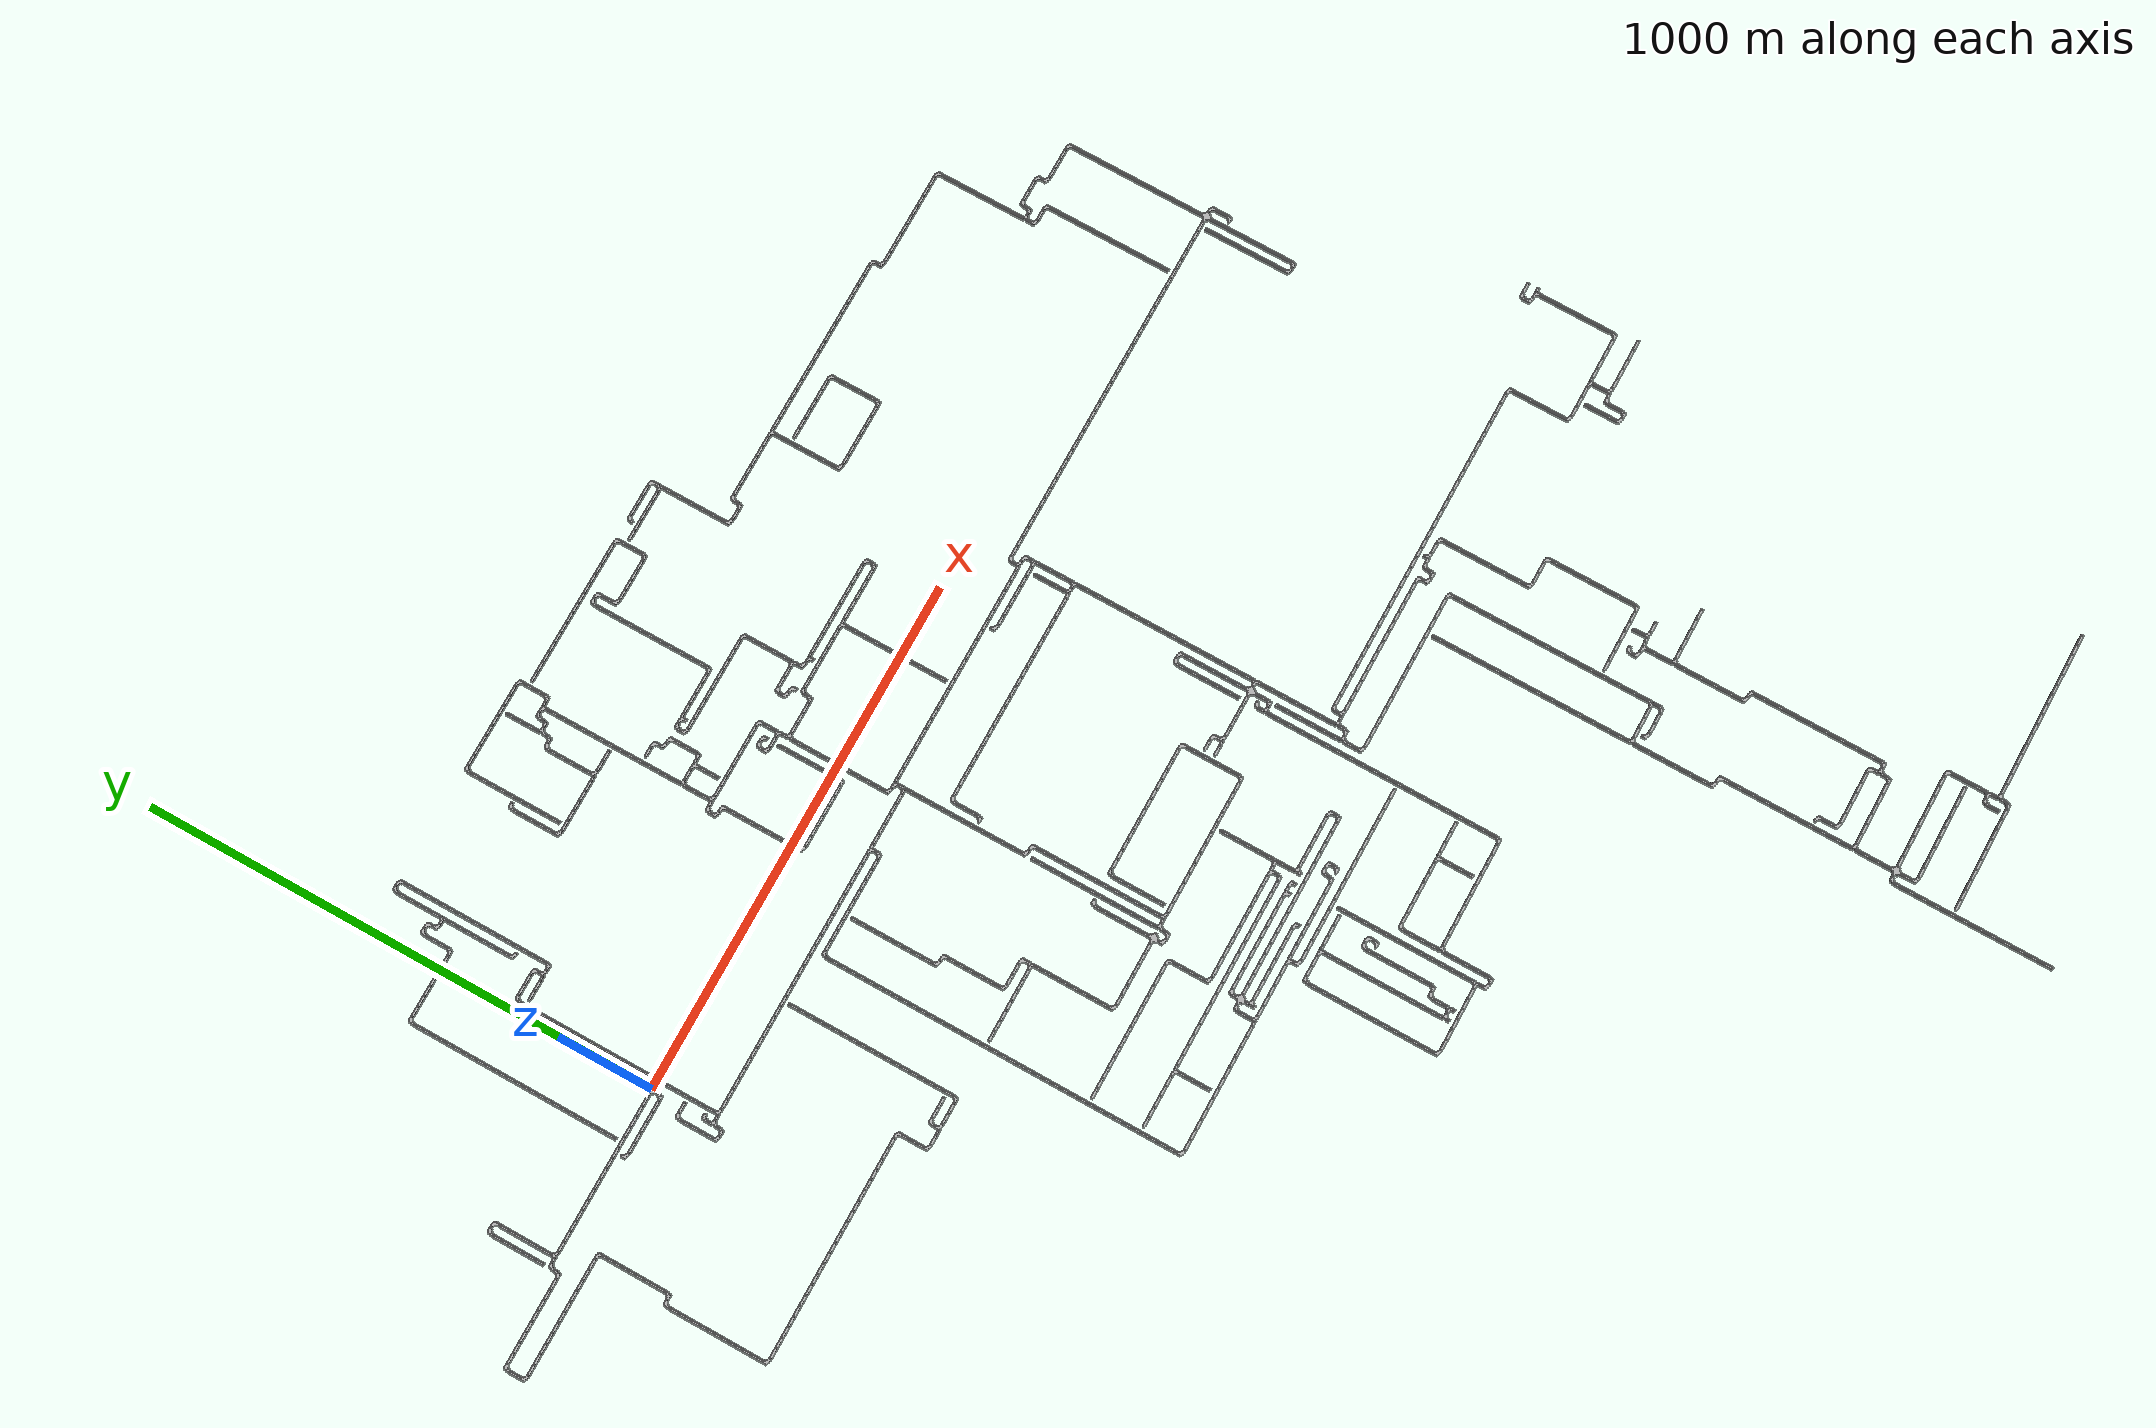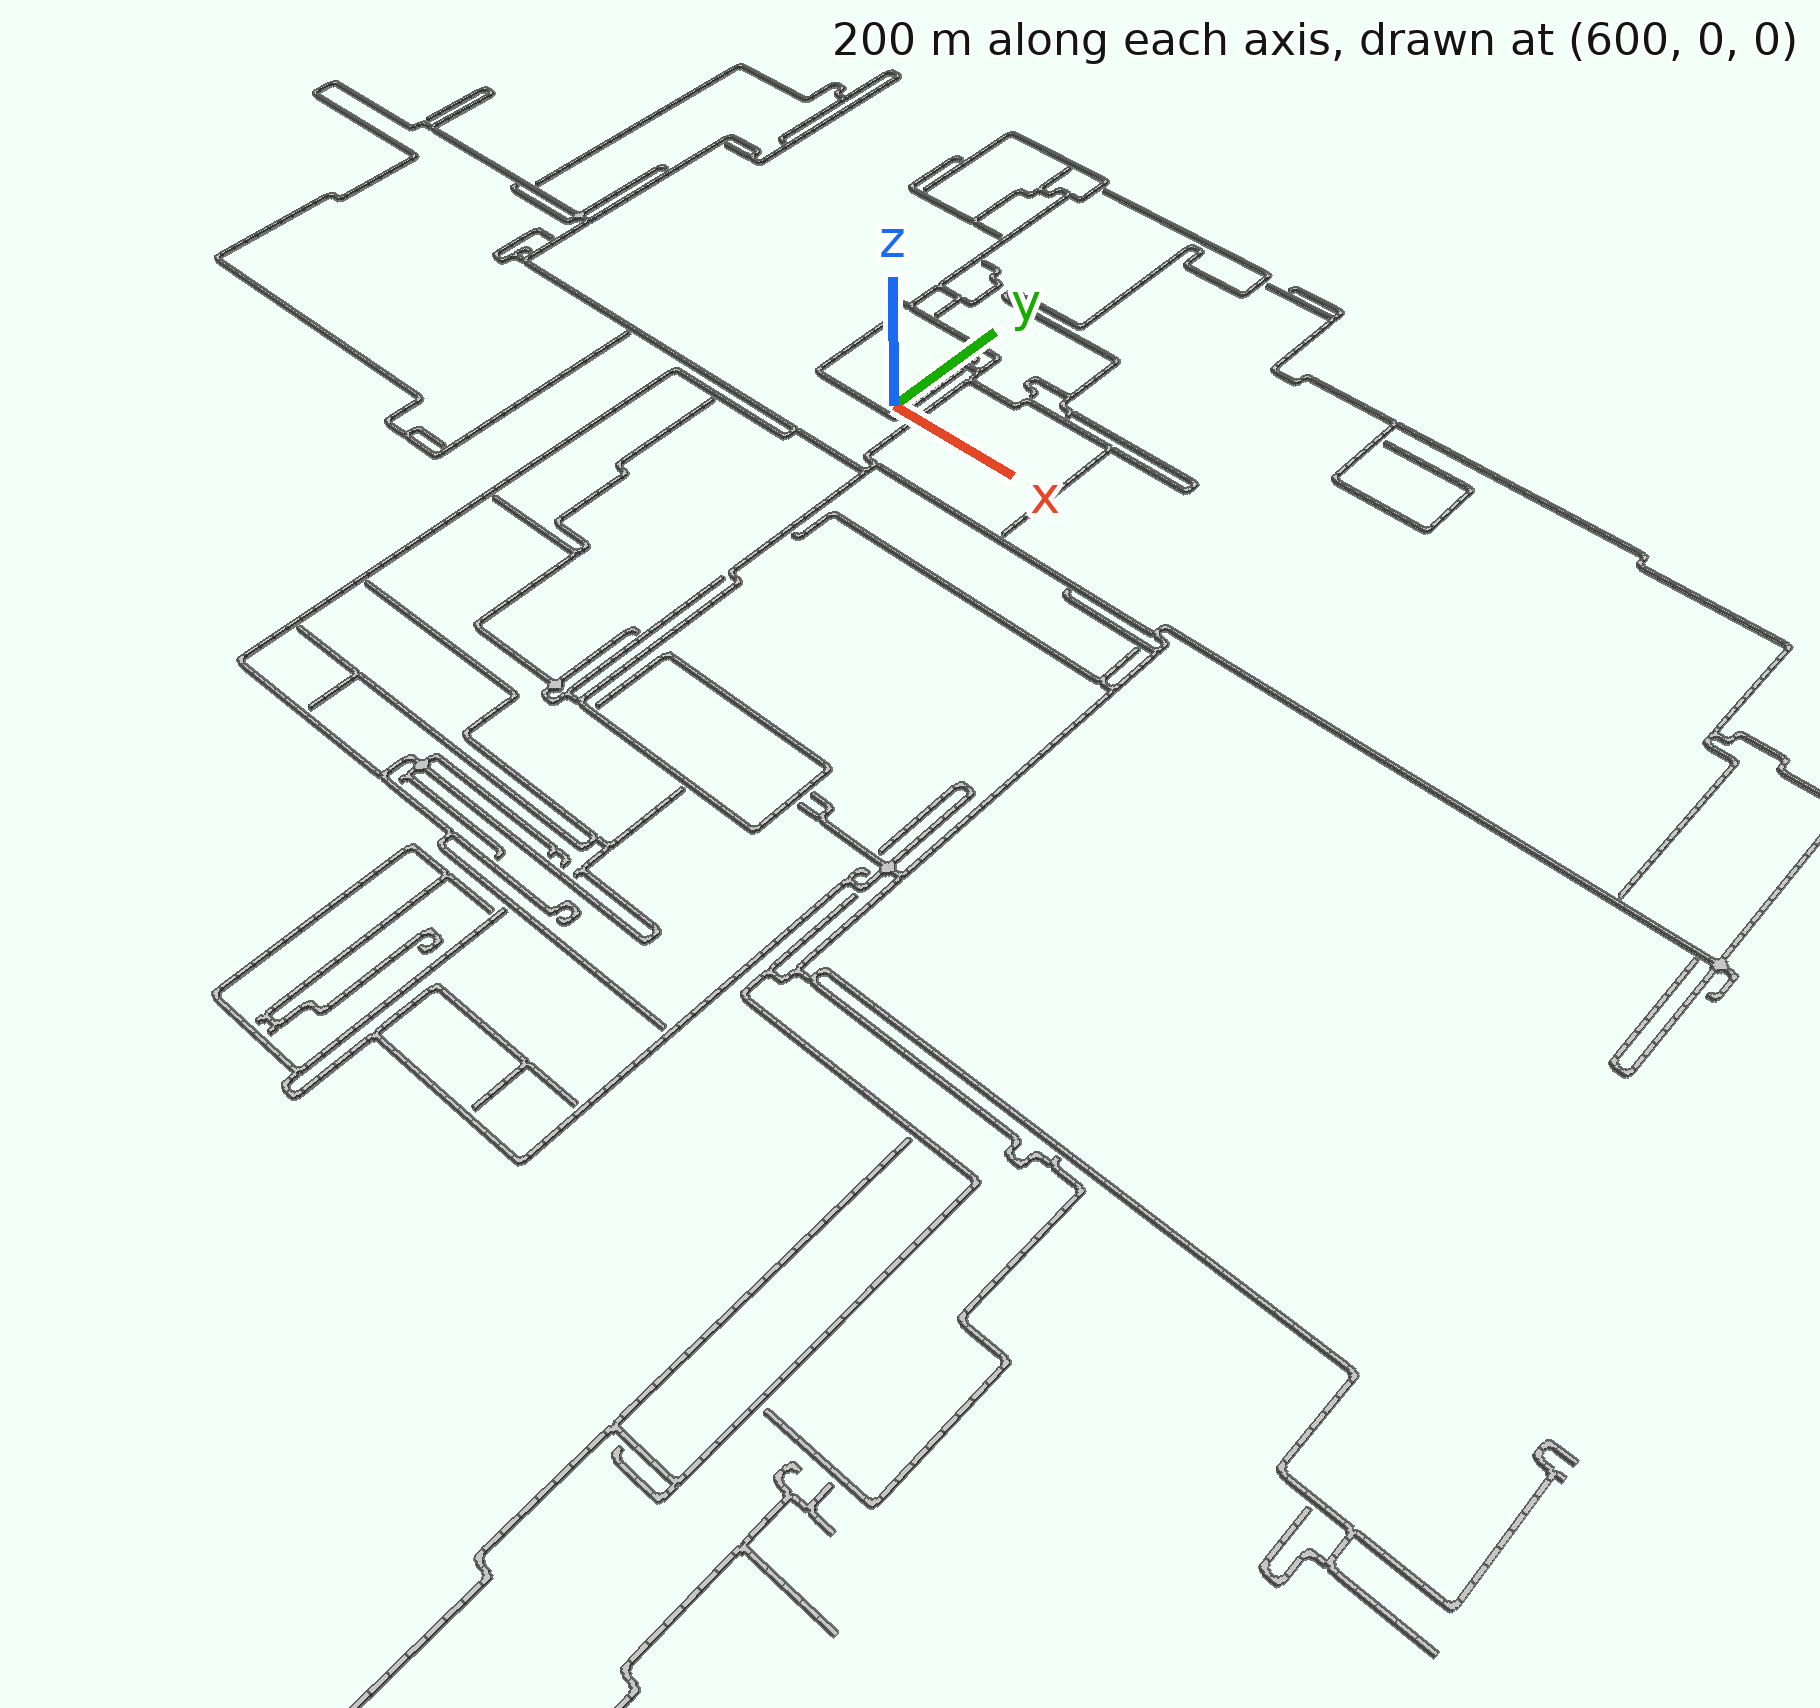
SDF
<sdf version="1.6">
 <world name="cave_32000_32">
  <include>
   <static>true</static>
   <name>cave_0_0</name>
   <pose>0 0 0 0 0 -1.5707963267948966</pose>
   <uri>model://cave_4way_20m</uri>
  </include>
  <include>
   <static>true</static>
   <name>cave_1_0</name>
   <pose>20 0 0 0 0 1.5707963267948966</pose>
   <uri>model://cave_3way_20m</uri>
  </include>
  <include>
   <static>true</static>
   <name>cave_1_-1</name>
   <pose>20 -20 0 0 0 0.0</pose>
   <uri>model://cave_straight_20m</uri>
  </include>
  <include>
   <static>true</static>
   <name>cave_1_-2</name>
   <pose>20 -40 0 0 0 0.0</pose>
   <uri>model://cave_straight_20m</uri>
  </include>
  <include>
   <static>true</static>
   <name>cave_1_-3</name>
   <pose>20 -60 0 0 0 0.0</pose>
   <uri>model://cave_straight_20m</uri>
  </include>
  <include>
   <static>true</static>
   <name>cave_1_-4</name>
   <pose>20 -80 0 0 0 0.0</pose>
   <uri>model://cave_straight_20m</uri>
  </include>
  <include>
   <static>true</static>
   <name>cave_1_-5</name>
   <pose>20 -100 0 0 0 0.0</pose>
   <uri>model://cave_straight_20m</uri>
  </include>
  <include>
   <static>true</static>
   <name>cave_1_-6</name>
   <pose>20 -120 0 0 0 0.0</pose>
   <uri>model://cave_3way_20m</uri>
  </include>
  <include>
   <static>true</static>
   <name>cave_2_-6</name>
   <pose>40 -120 0 0 0 1.5707963267948966</pose>
   <uri>model://cave_straight_20m</uri>
  </include>
  <include>
   <static>true</static>
   <name>cave_3_-6</name>
   <pose>60 -120 0 0 0 1.5707963267948966</pose>
   <uri>model://cave_straight_20m</uri>
  </include>
  <include>
   <static>true</static>
   <name>cave_4_-6</name>
   <pose>80 -120 0 0 0 1.5707963267948966</pose>
   <uri>model://cave_straight_20m</uri>
  </include>
  <include>
   <static>true</static>
   <name>cave_5_-6</name>
   <pose>100 -120 0 0 0 1.5707963267948966</pose>
   <uri>model://cave_straight_20m</uri>
  </include>
  <include>
   <static>true</static>
   <name>cave_6_-6</name>
   <pose>120 -120 0 0 0 1.5707963267948966</pose>
   <uri>model://cave_straight_20m</uri>
  </include>
  <include>
   <static>true</static>
   <name>cave_7_-6</name>
   <pose>140 -120 0 0 0 1.5707963267948966</pose>
   <uri>model://cave_straight_20m</uri>
  </include>
  <include>
   <static>true</static>
   <name>cave_8_-6</name>
   <pose>160 -120 0 0 0 1.5707963267948966</pose>
   <uri>model://cave_straight_20m</uri>
  </include>
  <include>
   <static>true</static>
   <name>cave_9_-6</name>
   <pose>180 -120 0 0 0 1.5707963267948966</pose>
   <uri>model://cave_straight_20m</uri>
  </include>
  <include>
   <static>true</static>
   <name>cave_10_-6</name>
   <pose>200 -120 0 0 0 1.5707963267948966</pose>
   <uri>model://cave_straight_20m</uri>
  </include>
  <include>
   <static>true</static>
   <name>cave_11_-6</name>
   <pose>220 -120 0 0 0 1.5707963267948966</pose>
   <uri>model://cave_straight_20m</uri>
  </include>
  <include>
   <static>true</static>
   <name>cave_12_-6</name>
   <pose>240 -120 0 0 0 1.5707963267948966</pose>
   <uri>model://cave_straight_20m</uri>
  </include>
  <include>
   <static>true</static>
   <name>cave_13_-6</name>
   <pose>260 -120 0 0 0 1.5707963267948966</pose>
   <uri>model://cave_straight_20m</uri>
  </include>
  <include>
   <static>true</static>
   <name>cave_14_-6</name>
   <pose>280 -120 0 0 0 1.5707963267948966</pose>
   <uri>model://cave_straight_20m</uri>
  </include>
  <include>
   <static>true</static>
   <name>cave_15_-6</name>
   <pose>300 -120 0 0 0 1.5707963267948966</pose>
   <uri>model://cave_straight_20m</uri>
  </include>
  <include>
   <static>true</static>
   <name>cave_16_-6</name>
   <pose>320 -120 0 0 0 1.5707963267948966</pose>
   <uri>model://cave_straight_20m</uri>
  </include>
  <include>
   <static>true</static>
   <name>cave_17_-6</name>
   <pose>340 -120 0 0 0 1.5707963267948966</pose>
   <uri>model://cave_straight_20m</uri>
  </include>
  <include>
   <static>true</static>
   <name>cave_18_-6</name>
   <pose>360 -120 0 0 0 1.5707963267948966</pose>
   <uri>model://cave_straight_20m</uri>
  </include>
  <include>
   <static>true</static>
   <name>cave_19_-6</name>
   <pose>380 -120 0 0 0 1.5707963267948966</pose>
   <uri>model://cave_straight_20m</uri>
  </include>
  <include>
   <static>true</static>
   <name>cave_20_-6</name>
   <pose>400 -120 0 0 0 1.5707963267948966</pose>
   <uri>model://cave_straight_20m</uri>
  </include>
  <include>
   <static>true</static>
   <name>cave_21_-6</name>
   <pose>420 -120 0 0 0 1.5707963267948966</pose>
   <uri>model://cave_straight_20m</uri>
  </include>
  <include>
   <static>true</static>
   <name>cave_22_-6</name>
   <pose>440 -120 0 0 0 1.5707963267948966</pose>
   <uri>model://cave_straight_20m</uri>
  </include>
  <include>
   <static>true</static>
   <name>cave_23_-6</name>
   <pose>460 -120 0 0 0 1.5707963267948966</pose>
   <uri>model://cave_straight_20m</uri>
  </include>
  <include>
   <static>true</static>
   <name>cave_24_-6</name>
   <pose>480 -120 0 0 0 1.5707963267948966</pose>
   <uri>model://cave_straight_20m</uri>
  </include>
  <include>
   <static>true</static>
   <name>cave_25_-6</name>
   <pose>500 -120 0 0 0 1.5707963267948966</pose>
   <uri>model://cave_straight_20m</uri>
  </include>
  <include>
   <static>true</static>
   <name>cave_26_-6</name>
   <pose>520 -120 0 0 0 1.5707963267948966</pose>
   <uri>model://cave_straight_20m</uri>
  </include>
  <include>
   <static>true</static>
   <name>cave_27_-6</name>
   <pose>540 -120 0 0 0 3.141592653589793</pose>
   <uri>model://cave_3way_20m</uri>
  </include>
  <include>
   <static>true</static>
   <name>cave_28_-6</name>
   <pose>560 -120 0 0 0 1.5707963267948966</pose>
   <uri>model://cave_straight_20m</uri>
  </include>
  <include>
   <static>true</static>
   <name>cave_29_-6</name>
   <pose>580 -120 0 0 0 1.5707963267948966</pose>
   <uri>model://cave_straight_20m</uri>
  </include>
  <include>
   <static>true</static>
   <name>cave_30_-6</name>
   <pose>600 -120 0 0 0 1.5707963267948966</pose>
   <uri>model://cave_straight_20m</uri>
  </include>
  <include>
   <static>true</static>
   <name>cave_31_-6</name>
   <pose>620 -120 0 0 0 1.5707963267948966</pose>
   <uri>model://cave_straight_20m</uri>
  </include>
  <include>
   <static>true</static>
   <name>cave_32_-6</name>
   <pose>640 -120 0 0 0 1.5707963267948966</pose>
   <uri>model://cave_straight_20m</uri>
  </include>
  <include>
   <static>true</static>
   <name>cave_33_-6</name>
   <pose>660 -120 0 0 0 1.5707963267948966</pose>
   <uri>model://cave_3way_20m</uri>
  </include>
  <include>
   <static>true</static>
   <name>cave_33_-7</name>
   <pose>660 -140 0 0 0 0.0</pose>
   <uri>model://cave_straight_20m</uri>
  </include>
  <include>
   <static>true</static>
   <name>cave_33_-8</name>
   <pose>660 -160 0 0 0 0.0</pose>
   <uri>model://cave_straight_20m</uri>
  </include>
  <include>
   <static>true</static>
   <name>cave_33_-9</name>
   <pose>660 -180 0 0 0 0.0</pose>
   <uri>model://cave_straight_20m</uri>
  </include>
  <include>
   <static>true</static>
   <name>cave_33_-10</name>
   <pose>660 -200 0 0 0 0.0</pose>
   <uri>model://cave_straight_20m</uri>
  </include>
  <include>
   <static>true</static>
   <name>cave_33_-11</name>
   <pose>660 -220 0 0 0 0.0</pose>
   <uri>model://cave_straight_20m</uri>
  </include>
  <include>
   <static>true</static>
   <name>cave_33_-12</name>
   <pose>660 -240 0 0 0 0.0</pose>
   <uri>model://cave_straight_20m</uri>
  </include>
  <include>
   <static>true</static>
   <name>cave_33_-13</name>
   <pose>660 -260 0 0 0 0.0</pose>
   <uri>model://cave_straight_20m</uri>
  </include>
  <include>
   <static>true</static>
   <name>cave_33_-14</name>
   <pose>660 -280 0 0 0 0.0</pose>
   <uri>model://cave_straight_20m</uri>
  </include>
  <include>
   <static>true</static>
   <name>cave_33_-15</name>
   <pose>660 -300 0 0 0 0.0</pose>
   <uri>model://cave_straight_20m</uri>
  </include>
  <include>
   <static>true</static>
   <name>cave_33_-16</name>
   <pose>660 -320 0 0 0 0.0</pose>
   <uri>model://cave_straight_20m</uri>
  </include>
  <include>
   <static>true</static>
   <name>cave_33_-17</name>
   <pose>660 -340 0 0 0 0.0</pose>
   <uri>model://cave_straight_20m</uri>
  </include>
  <include>
   <static>true</static>
   <name>cave_33_-18</name>
   <pose>660 -360 0 0 0 0.0</pose>
   <uri>model://cave_L_20m</uri>
  </include>
  <include>
   <static>true</static>
   <name>cave_34_-18</name>
   <pose>680 -360 0 0 0 3.141592653589793</pose>
   <uri>model://cave_L_20m</uri>
  </include>
  <include>
   <static>true</static>
   <name>cave_34_-19</name>
   <pose>680 -380 0 0 0 0.0</pose>
   <uri>model://cave_straight_20m</uri>
  </include>
  <include>
   <static>true</static>
   <name>cave_34_-20</name>
   <pose>680 -400 0 0 0 0.0</pose>
   <uri>model://cave_straight_20m</uri>
  </include>
  <include>
   <static>true</static>
   <name>cave_34_-21</name>
   <pose>680 -420 0 0 0 0.0</pose>
   <uri>model://cave_straight_20m</uri>
  </include>
  <include>
   <static>true</static>
   <name>cave_34_-22</name>
   <pose>680 -440 0 0 0 0.0</pose>
   <uri>model://cave_straight_20m</uri>
  </include>
  <include>
   <static>true</static>
   <name>cave_34_-23</name>
   <pose>680 -460 0 0 0 0.0</pose>
   <uri>model://cave_straight_20m</uri>
  </include>
  <include>
   <static>true</static>
   <name>cave_34_-24</name>
   <pose>680 -480 0 0 0 0.0</pose>
   <uri>model://cave_straight_20m</uri>
  </include>
  <include>
   <static>true</static>
   <name>cave_34_-25</name>
   <pose>680 -500 0 0 0 0.0</pose>
   <uri>model://cave_straight_20m</uri>
  </include>
  <include>
   <static>true</static>
   <name>cave_34_-26</name>
   <pose>680 -520 0 0 0 0.0</pose>
   <uri>model://cave_straight_20m</uri>
  </include>
  <include>
   <static>true</static>
   <name>cave_34_-27</name>
   <pose>680 -540 0 0 0 0.0</pose>
   <uri>model://cave_straight_20m</uri>
  </include>
  <include>
   <static>true</static>
   <name>cave_34_-28</name>
   <pose>680 -560 0 0 0 0.0</pose>
   <uri>model://cave_straight_20m</uri>
  </include>
  <include>
   <static>true</static>
   <name>cave_34_-29</name>
   <pose>680 -580 0 0 0 0.0</pose>
   <uri>model://cave_straight_20m</uri>
  </include>
  <include>
   <static>true</static>
   <name>cave_34_-30</name>
   <pose>680 -600 0 0 0 0.0</pose>
   <uri>model://cave_straight_20m</uri>
  </include>
  <include>
   <static>true</static>
   <name>cave_34_-31</name>
   <pose>680 -620 0 0 0 0.0</pose>
   <uri>model://cave_3way_20m</uri>
  </include>
  <include>
   <static>true</static>
   <name>cave_35_-31</name>
   <pose>700 -620 0 0 0 1.5707963267948966</pose>
   <uri>model://cave_straight_20m</uri>
  </include>
  <include>
   <static>true</static>
   <name>cave_36_-31</name>
   <pose>720 -620 0 0 0 1.5707963267948966</pose>
   <uri>model://cave_straight_20m</uri>
  </include>
  <include>
   <static>true</static>
   <name>cave_37_-31</name>
   <pose>740 -620 0 0 0 1.5707963267948966</pose>
   <uri>model://cave_straight_20m</uri>
  </include>
  <include>
   <static>true</static>
   <name>cave_38_-31</name>
   <pose>760 -620 0 0 0 1.5707963267948966</pose>
   <uri>model://cave_straight_20m</uri>
  </include>
  <include>
   <static>true</static>
   <name>cave_39_-31</name>
   <pose>780 -620 0 0 0 1.5707963267948966</pose>
   <uri>model://cave_straight_20m</uri>
  </include>
  <include>
   <static>true</static>
   <name>cave_40_-31</name>
   <pose>800 -620 0 0 0 1.5707963267948966</pose>
   <uri>model://cave_straight_20m</uri>
  </include>
  <include>
   <static>true</static>
   <name>cave_41_-31</name>
   <pose>820 -620 0 0 0 1.5707963267948966</pose>
   <uri>model://cave_straight_20m</uri>
  </include>
  <include>
   <static>true</static>
   <name>cave_42_-31</name>
   <pose>840 -620 0 0 0 1.5707963267948966</pose>
   <uri>model://cave_straight_20m</uri>
  </include>
  <include>
   <static>true</static>
   <name>cave_43_-31</name>
   <pose>860 -620 0 0 0 1.5707963267948966</pose>
   <uri>model://cave_straight_20m</uri>
  </include>
  <include>
   <static>true</static>
   <name>cave_44_-31</name>
   <pose>880 -620 0 0 0 1.5707963267948966</pose>
   <uri>model://cave_straight_20m</uri>
  </include>
  <include>
   <static>true</static>
   <name>cave_45_-31</name>
   <pose>900 -620 0 0 0 1.5707963267948966</pose>
   <uri>model://cave_straight_20m</uri>
  </include>
  <include>
   <static>true</static>
   <name>cave_46_-31</name>
   <pose>920 -620 0 0 0 1.5707963267948966</pose>
   <uri>model://cave_straight_20m</uri>
  </include>
  <include>
   <static>true</static>
   <name>cave_47_-31</name>
   <pose>940 -620 0 0 0 1.5707963267948966</pose>
   <uri>model://cave_straight_20m</uri>
  </include>
  <include>
   <static>true</static>
   <name>cave_48_-31</name>
   <pose>960 -620 0 0 0 1.5707963267948966</pose>
   <uri>model://cave_L_20m</uri>
  </include>
  <include>
   <static>true</static>
   <name>cave_48_-30</name>
   <pose>960 -600 0 0 0 0.0</pose>
   <uri>model://cave_straight_20m</uri>
  </include>
  <include>
   <static>true</static>
   <name>cave_48_-29</name>
   <pose>960 -580 0 0 0 0.0</pose>
   <uri>model://cave_straight_20m</uri>
  </include>
  <include>
   <static>true</static>
   <name>cave_48_-28</name>
   <pose>960 -560 0 0 0 0.0</pose>
   <uri>model://cave_straight_20m</uri>
  </include>
  <include>
   <static>true</static>
   <name>cave_48_-27</name>
   <pose>960 -540 0 0 0 0.0</pose>
   <uri>model://cave_straight_20m</uri>
  </include>
  <include>
   <static>true</static>
   <name>cave_48_-26</name>
   <pose>960 -520 0 0 0 0.0</pose>
   <uri>model://cave_straight_20m</uri>
  </include>
  <include>
   <static>true</static>
   <name>cave_48_-25</name>
   <pose>960 -500 0 0 0 3.141592653589793</pose>
   <uri>model://cave_L_20m</uri>
  </include>
  <include>
   <static>true</static>
   <name>cave_47_-25</name>
   <pose>940 -500 0 0 0 1.5707963267948966</pose>
   <uri>model://cave_straight_20m</uri>
  </include>
  <include>
   <static>true</static>
   <name>cave_46_-25</name>
   <pose>920 -500 0 0 0 1.5707963267948966</pose>
   <uri>model://cave_straight_20m</uri>
  </include>
  <include>
   <static>true</static>
   <name>cave_45_-25</name>
   <pose>900 -500 0 0 0 1.5707963267948966</pose>
   <uri>model://cave_straight_20m</uri>
  </include>
  <include>
   <static>true</static>
   <name>cave_44_-25</name>
   <pose>880 -500 0 0 0 1.5707963267948966</pose>
   <uri>model://cave_straight_20m</uri>
  </include>
  <include>
   <static>true</static>
   <name>cave_43_-25</name>
   <pose>860 -500 0 0 0 1.5707963267948966</pose>
   <uri>model://cave_straight_20m</uri>
  </include>
  <include>
   <static>true</static>
   <name>cave_42_-25</name>
   <pose>840 -500 0 0 0 1.5707963267948966</pose>
   <uri>model://cave_straight_20m</uri>
  </include>
  <include>
   <static>true</static>
   <name>cave_41_-25</name>
   <pose>820 -500 0 0 0 1.5707963267948966</pose>
   <uri>model://cave_straight_20m</uri>
  </include>
  <include>
   <static>true</static>
   <name>cave_40_-25</name>
   <pose>800 -500 0 0 0 1.5707963267948966</pose>
   <uri>model://cave_straight_20m</uri>
  </include>
  <include>
   <static>true</static>
   <name>cave_39_-25</name>
   <pose>780 -500 0 0 0 1.5707963267948966</pose>
   <uri>model://cave_straight_20m</uri>
  </include>
  <include>
   <static>true</static>
   <name>cave_38_-25</name>
   <pose>760 -500 0 0 0 1.5707963267948966</pose>
   <uri>model://cave_straight_20m</uri>
  </include>
  <include>
   <static>true</static>
   <name>cave_37_-25</name>
   <pose>740 -500 0 0 0 1.5707963267948966</pose>
   <uri>model://cave_straight_20m</uri>
  </include>
  <include>
   <static>true</static>
   <name>cave_36_-25</name>
   <pose>720 -500 0 0 0 1.5707963267948966</pose>
   <uri>model://cave_straight_20m</uri>
  </include>
  <include>
   <static>true</static>
   <name>cave_35_-25</name>
   <pose>700 -500 0 0 0 -1.5707963267948966</pose>
   <uri>model://cave_L_20m</uri>
  </include>
  <include>
   <static>true</static>
   <name>cave_35_-26</name>
   <pose>700 -520 0 0 0 0.0</pose>
   <uri>model://cave_straight_20m</uri>
  </include>
  <include>
   <static>true</static>
   <name>cave_35_-27</name>
   <pose>700 -540 0 0 0 0.0</pose>
   <uri>model://cave_straight_20m</uri>
  </include>
  <include>
   <static>true</static>
   <name>cave_35_-28</name>
   <pose>700 -560 0 0 0 0.0</pose>
   <uri>model://cave_straight_20m</uri>
  </include>
  <include>
   <static>true</static>
   <name>cave_35_-29</name>
   <pose>700 -580 0 0 0 0.0</pose>
   <uri>model://cave_straight_20m</uri>
  </include>
  <include>
   <static>true</static>
   <name>cave_35_-30</name>
   <pose>700 -600 0 0 0 0.0</pose>
   <uri>model://cave_straight_20m</uri>
  </include>
  <include>
   <static>true</static>
   <name>cave_33_-31</name>
   <pose>660 -620 0 0 0 -1.5707963267948966</pose>
   <uri>model://cave_3way_20m</uri>
  </include>
  <include>
   <static>true</static>
   <name>cave_33_-32</name>
   <pose>660 -640 0 0 0 1.5707963267948966</pose>
   <uri>model://cave_L_20m</uri>
  </include>
  <include>
   <static>true</static>
   <name>cave_32_-32</name>
   <pose>640 -640 0 0 0 0.0</pose>
   <uri>model://cave_L_20m</uri>
  </include>
  <include>
   <static>true</static>
   <name>cave_32_-31</name>
   <pose>640 -620 0 0 0 -1.5707963267948966</pose>
   <uri>model://cave_4way_20m</uri>
  </include>
  <include>
   <static>true</static>
   <name>cave_31_-31</name>
   <pose>620 -620 0 0 0 1.5707963267948966</pose>
   <uri>model://cave_straight_20m</uri>
  </include>
  <include>
   <static>true</static>
   <name>cave_30_-31</name>
   <pose>600 -620 0 0 0 1.5707963267948966</pose>
   <uri>model://cave_straight_20m</uri>
  </include>
  <include>
   <static>true</static>
   <name>cave_29_-31</name>
   <pose>580 -620 0 0 0 1.5707963267948966</pose>
   <uri>model://cave_straight_20m</uri>
  </include>
  <include>
   <static>true</static>
   <name>cave_28_-31</name>
   <pose>560 -620 0 0 0 1.5707963267948966</pose>
   <uri>model://cave_straight_20m</uri>
  </include>
  <include>
   <static>true</static>
   <name>cave_27_-31</name>
   <pose>540 -620 0 0 0 1.5707963267948966</pose>
   <uri>model://cave_straight_20m</uri>
  </include>
  <include>
   <static>true</static>
   <name>cave_26_-31</name>
   <pose>520 -620 0 0 0 1.5707963267948966</pose>
   <uri>model://cave_straight_20m</uri>
  </include>
  <include>
   <static>true</static>
   <name>cave_25_-31</name>
   <pose>500 -620 0 0 0 0.0</pose>
   <uri>model://cave_L_20m</uri>
  </include>
  <include>
   <static>true</static>
   <name>cave_25_-30</name>
   <pose>500 -600 0 0 0 0.0</pose>
   <uri>model://cave_straight_20m</uri>
  </include>
  <include>
   <static>true</static>
   <name>cave_25_-29</name>
   <pose>500 -580 0 0 0 0.0</pose>
   <uri>model://cave_straight_20m</uri>
  </include>
  <include>
   <static>true</static>
   <name>cave_25_-28</name>
   <pose>500 -560 0 0 0 0.0</pose>
   <uri>model://cave_straight_20m</uri>
  </include>
  <include>
   <static>true</static>
   <name>cave_25_-27</name>
   <pose>500 -540 0 0 0 0.0</pose>
   <uri>model://cave_straight_20m</uri>
  </include>
  <include>
   <static>true</static>
   <name>cave_25_-26</name>
   <pose>500 -520 0 0 0 0.0</pose>
   <uri>model://cave_straight_20m</uri>
  </include>
  <include>
   <static>true</static>
   <name>cave_25_-25</name>
   <pose>500 -500 0 0 0 0.0</pose>
   <uri>model://cave_straight_20m</uri>
  </include>
  <include>
   <static>true</static>
   <name>cave_25_-24</name>
   <pose>500 -480 0 0 0 0.0</pose>
   <uri>model://cave_straight_20m</uri>
  </include>
  <include>
   <static>true</static>
   <name>cave_25_-23</name>
   <pose>500 -460 0 0 0 1.5707963267948966</pose>
   <uri>model://cave_3way_20m</uri>
  </include>
  <include>
   <static>true</static>
   <name>cave_24_-23</name>
   <pose>480 -460 0 0 0 1.5707963267948966</pose>
   <uri>model://cave_straight_20m</uri>
  </include>
  <include>
   <static>true</static>
   <name>cave_23_-23</name>
   <pose>460 -460 0 0 0 1.5707963267948966</pose>
   <uri>model://cave_straight_20m</uri>
  </include>
  <include>
   <static>true</static>
   <name>cave_22_-23</name>
   <pose>440 -460 0 0 0 1.5707963267948966</pose>
   <uri>model://cave_straight_20m</uri>
  </include>
  <include>
   <static>true</static>
   <name>cave_21_-23</name>
   <pose>420 -460 0 0 0 1.5707963267948966</pose>
   <uri>model://cave_straight_20m</uri>
  </include>
  <include>
   <static>true</static>
   <name>cave_20_-23</name>
   <pose>400 -460 0 0 0 1.5707963267948966</pose>
   <uri>model://cave_straight_20m</uri>
  </include>
  <include>
   <static>true</static>
   <name>cave_19_-23</name>
   <pose>380 -460 0 0 0 1.5707963267948966</pose>
   <uri>model://cave_straight_20m</uri>
  </include>
  <include>
   <static>true</static>
   <name>cave_18_-23</name>
   <pose>360 -460 0 0 0 1.5707963267948966</pose>
   <uri>model://cave_straight_20m</uri>
  </include>
  <include>
   <static>true</static>
   <name>cave_25_-22</name>
   <pose>500 -440 0 0 0 3.141592653589793</pose>
   <uri>model://cave_L_20m</uri>
  </include>
  <include>
   <static>true</static>
   <name>cave_24_-22</name>
   <pose>480 -440 0 0 0 1.5707963267948966</pose>
   <uri>model://cave_straight_20m</uri>
  </include>
  <include>
   <static>true</static>
   <name>cave_23_-22</name>
   <pose>460 -440 0 0 0 1.5707963267948966</pose>
   <uri>model://cave_straight_20m</uri>
  </include>
  <include>
   <static>true</static>
   <name>cave_22_-22</name>
   <pose>440 -440 0 0 0 0.0</pose>
   <uri>model://cave_L_20m</uri>
  </include>
  <include>
   <static>true</static>
   <name>cave_22_-21</name>
   <pose>440 -420 0 0 0 0.0</pose>
   <uri>model://cave_straight_20m</uri>
  </include>
  <include>
   <static>true</static>
   <name>cave_22_-20</name>
   <pose>440 -400 0 0 0 0.0</pose>
   <uri>model://cave_straight_20m</uri>
  </include>
  <include>
   <static>true</static>
   <name>cave_22_-19</name>
   <pose>440 -380 0 0 0 0.0</pose>
   <uri>model://cave_straight_20m</uri>
  </include>
  <include>
   <static>true</static>
   <name>cave_22_-18</name>
   <pose>440 -360 0 0 0 0.0</pose>
   <uri>model://cave_straight_20m</uri>
  </include>
  <include>
   <static>true</static>
   <name>cave_22_-17</name>
   <pose>440 -340 0 0 0 0.0</pose>
   <uri>model://cave_straight_20m</uri>
  </include>
  <include>
   <static>true</static>
   <name>cave_22_-16</name>
   <pose>440 -320 0 0 0 3.141592653589793</pose>
   <uri>model://cave_L_20m</uri>
  </include>
  <include>
   <static>true</static>
   <name>cave_21_-16</name>
   <pose>420 -320 0 0 0 0.0</pose>
   <uri>model://cave_L_20m</uri>
  </include>
  <include>
   <static>true</static>
   <name>cave_21_-15</name>
   <pose>420 -300 0 0 0 0.0</pose>
   <uri>model://cave_straight_20m</uri>
  </include>
  <include>
   <static>true</static>
   <name>cave_21_-14</name>
   <pose>420 -280 0 0 0 0.0</pose>
   <uri>model://cave_straight_20m</uri>
  </include>
  <include>
   <static>true</static>
   <name>cave_21_-13</name>
   <pose>420 -260 0 0 0 0.0</pose>
   <uri>model://cave_straight_20m</uri>
  </include>
  <include>
   <static>true</static>
   <name>cave_21_-12</name>
   <pose>420 -240 0 0 0 0.0</pose>
   <uri>model://cave_straight_20m</uri>
  </include>
  <include>
   <static>true</static>
   <name>cave_21_-11</name>
   <pose>420 -220 0 0 0 0.0</pose>
   <uri>model://cave_straight_20m</uri>
  </include>
  <include>
   <static>true</static>
   <name>cave_21_-10</name>
   <pose>420 -200 0 0 0 0.0</pose>
   <uri>model://cave_straight_20m</uri>
  </include>
  <include>
   <static>true</static>
   <name>cave_21_-9</name>
   <pose>420 -180 0 0 0 0.0</pose>
   <uri>model://cave_straight_20m</uri>
  </include>
  <include>
   <static>true</static>
   <name>cave_21_-8</name>
   <pose>420 -160 0 0 0 0.0</pose>
   <uri>model://cave_straight_20m</uri>
  </include>
  <include>
   <static>true</static>
   <name>cave_32_-30</name>
   <pose>640 -600 0 0 0 0.0</pose>
   <uri>model://cave_straight_20m</uri>
  </include>
  <include>
   <static>true</static>
   <name>cave_32_-29</name>
   <pose>640 -580 0 0 0 0.0</pose>
   <uri>model://cave_straight_20m</uri>
  </include>
  <include>
   <static>true</static>
   <name>cave_32_-28</name>
   <pose>640 -560 0 0 0 0.0</pose>
   <uri>model://cave_straight_20m</uri>
  </include>
  <include>
   <static>true</static>
   <name>cave_32_-27</name>
   <pose>640 -540 0 0 0 0.0</pose>
   <uri>model://cave_straight_20m</uri>
  </include>
  <include>
   <static>true</static>
   <name>cave_32_-26</name>
   <pose>640 -520 0 0 0 0.0</pose>
   <uri>model://cave_straight_20m</uri>
  </include>
  <include>
   <static>true</static>
   <name>cave_32_-25</name>
   <pose>640 -500 0 0 0 -1.5707963267948966</pose>
   <uri>model://cave_L_20m</uri>
  </include>
  <include>
   <static>true</static>
   <name>cave_33_-30</name>
   <pose>660 -600 0 0 0 0.0</pose>
   <uri>model://cave_straight_20m</uri>
  </include>
  <include>
   <static>true</static>
   <name>cave_33_-29</name>
   <pose>660 -580 0 0 0 0.0</pose>
   <uri>model://cave_straight_20m</uri>
  </include>
  <include>
   <static>true</static>
   <name>cave_33_-28</name>
   <pose>660 -560 0 0 0 0.0</pose>
   <uri>model://cave_straight_20m</uri>
  </include>
  <include>
   <static>true</static>
   <name>cave_33_-27</name>
   <pose>660 -540 0 0 0 0.0</pose>
   <uri>model://cave_straight_20m</uri>
  </include>
  <include>
   <static>true</static>
   <name>cave_33_-26</name>
   <pose>660 -520 0 0 0 0.0</pose>
   <uri>model://cave_straight_20m</uri>
  </include>
  <include>
   <static>true</static>
   <name>cave_33_-25</name>
   <pose>660 -500 0 0 0 0.0</pose>
   <uri>model://cave_straight_20m</uri>
  </include>
  <include>
   <static>true</static>
   <name>cave_33_-24</name>
   <pose>660 -480 0 0 0 0.0</pose>
   <uri>model://cave_straight_20m</uri>
  </include>
  <include>
   <static>true</static>
   <name>cave_33_-23</name>
   <pose>660 -460 0 0 0 0.0</pose>
   <uri>model://cave_straight_20m</uri>
  </include>
  <include>
   <static>true</static>
   <name>cave_33_-22</name>
   <pose>660 -440 0 0 0 0.0</pose>
   <uri>model://cave_straight_20m</uri>
  </include>
  <include>
   <static>true</static>
   <name>cave_33_-21</name>
   <pose>660 -420 0 0 0 0.0</pose>
   <uri>model://cave_straight_20m</uri>
  </include>
  <include>
   <static>true</static>
   <name>cave_33_-20</name>
   <pose>660 -400 0 0 0 0.0</pose>
   <uri>model://cave_straight_20m</uri>
  </include>
  <include>
   <static>true</static>
   <name>cave_33_-19</name>
   <pose>660 -380 0 0 0 0.0</pose>
   <uri>model://cave_straight_20m</uri>
  </include>
  <include>
   <static>true</static>
   <name>cave_33_-5</name>
   <pose>660 -100 0 0 0 3.141592653589793</pose>
   <uri>model://cave_3way_20m</uri>
  </include>
  <include>
   <static>true</static>
   <name>cave_34_-5</name>
   <pose>680 -100 0 0 0 1.5707963267948966</pose>
   <uri>model://cave_straight_20m</uri>
  </include>
  <include>
   <static>true</static>
   <name>cave_35_-5</name>
   <pose>700 -100 0 0 0 1.5707963267948966</pose>
   <uri>model://cave_straight_20m</uri>
  </include>
  <include>
   <static>true</static>
   <name>cave_36_-5</name>
   <pose>720 -100 0 0 0 1.5707963267948966</pose>
   <uri>model://cave_straight_20m</uri>
  </include>
  <include>
   <static>true</static>
   <name>cave_37_-5</name>
   <pose>740 -100 0 0 0 1.5707963267948966</pose>
   <uri>model://cave_straight_20m</uri>
  </include>
  <include>
   <static>true</static>
   <name>cave_38_-5</name>
   <pose>760 -100 0 0 0 1.5707963267948966</pose>
   <uri>model://cave_straight_20m</uri>
  </include>
  <include>
   <static>true</static>
   <name>cave_39_-5</name>
   <pose>780 -100 0 0 0 1.5707963267948966</pose>
   <uri>model://cave_straight_20m</uri>
  </include>
  <include>
   <static>true</static>
   <name>cave_40_-5</name>
   <pose>800 -100 0 0 0 1.5707963267948966</pose>
   <uri>model://cave_straight_20m</uri>
  </include>
  <include>
   <static>true</static>
   <name>cave_41_-5</name>
   <pose>820 -100 0 0 0 1.5707963267948966</pose>
   <uri>model://cave_straight_20m</uri>
  </include>
  <include>
   <static>true</static>
   <name>cave_42_-5</name>
   <pose>840 -100 0 0 0 1.5707963267948966</pose>
   <uri>model://cave_straight_20m</uri>
  </include>
  <include>
   <static>true</static>
   <name>cave_43_-5</name>
   <pose>860 -100 0 0 0 1.5707963267948966</pose>
   <uri>model://cave_straight_20m</uri>
  </include>
  <include>
   <static>true</static>
   <name>cave_44_-5</name>
   <pose>880 -100 0 0 0 1.5707963267948966</pose>
   <uri>model://cave_straight_20m</uri>
  </include>
  <include>
   <static>true</static>
   <name>cave_45_-5</name>
   <pose>900 -100 0 0 0 1.5707963267948966</pose>
   <uri>model://cave_straight_20m</uri>
  </include>
  <include>
   <static>true</static>
   <name>cave_46_-5</name>
   <pose>920 -100 0 0 0 1.5707963267948966</pose>
   <uri>model://cave_straight_20m</uri>
  </include>
  <include>
   <static>true</static>
   <name>cave_47_-5</name>
   <pose>940 -100 0 0 0 1.5707963267948966</pose>
   <uri>model://cave_straight_20m</uri>
  </include>
  <include>
   <static>true</static>
   <name>cave_48_-5</name>
   <pose>960 -100 0 0 0 1.5707963267948966</pose>
   <uri>model://cave_straight_20m</uri>
  </include>
  <include>
   <static>true</static>
   <name>cave_49_-5</name>
   <pose>980 -100 0 0 0 1.5707963267948966</pose>
   <uri>model://cave_straight_20m</uri>
  </include>
  <include>
   <static>true</static>
   <name>cave_50_-5</name>
   <pose>1000 -100 0 0 0 1.5707963267948966</pose>
   <uri>model://cave_straight_20m</uri>
  </include>
  <include>
   <static>true</static>
   <name>cave_51_-5</name>
   <pose>1020 -100 0 0 0 1.5707963267948966</pose>
   <uri>model://cave_straight_20m</uri>
  </include>
  <include>
   <static>true</static>
   <name>cave_52_-5</name>
   <pose>1040 -100 0 0 0 1.5707963267948966</pose>
   <uri>model://cave_straight_20m</uri>
  </include>
  <include>
   <static>true</static>
   <name>cave_53_-5</name>
   <pose>1060 -100 0 0 0 1.5707963267948966</pose>
   <uri>model://cave_straight_20m</uri>
  </include>
  <include>
   <static>true</static>
   <name>cave_54_-5</name>
   <pose>1080 -100 0 0 0 1.5707963267948966</pose>
   <uri>model://cave_straight_20m</uri>
  </include>
  <include>
   <static>true</static>
   <name>cave_55_-5</name>
   <pose>1100 -100 0 0 0 0.0</pose>
   <uri>model://cave_3way_20m</uri>
  </include>
  <include>
   <static>true</static>
   <name>cave_56_-5</name>
   <pose>1120 -100 0 0 0 3.141592653589793</pose>
   <uri>model://cave_L_20m</uri>
  </include>
  <include>
   <static>true</static>
   <name>cave_56_-6</name>
   <pose>1120 -120 0 0 0 1.5707963267948966</pose>
   <uri>model://cave_3way_20m</uri>
  </include>
  <include>
   <static>true</static>
   <name>cave_56_-7</name>
   <pose>1120 -140 0 0 0 0.0</pose>
   <uri>model://cave_straight_20m</uri>
  </include>
  <include>
   <static>true</static>
   <name>cave_56_-8</name>
   <pose>1120 -160 0 0 0 0.0</pose>
   <uri>model://cave_straight_20m</uri>
  </include>
  <include>
   <static>true</static>
   <name>cave_56_-9</name>
   <pose>1120 -180 0 0 0 0.0</pose>
   <uri>model://cave_straight_20m</uri>
  </include>
  <include>
   <static>true</static>
   <name>cave_56_-10</name>
   <pose>1120 -200 0 0 0 1.5707963267948966</pose>
   <uri>model://cave_3way_20m</uri>
  </include>
  <include>
   <static>true</static>
   <name>cave_56_-11</name>
   <pose>1120 -220 0 0 0 0.0</pose>
   <uri>model://cave_straight_20m</uri>
  </include>
  <include>
   <static>true</static>
   <name>cave_56_-12</name>
   <pose>1120 -240 0 0 0 0.0</pose>
   <uri>model://cave_straight_20m</uri>
  </include>
  <include>
   <static>true</static>
   <name>cave_56_-13</name>
   <pose>1120 -260 0 0 0 0.0</pose>
   <uri>model://cave_straight_20m</uri>
  </include>
  <include>
   <static>true</static>
   <name>cave_56_-14</name>
   <pose>1120 -280 0 0 0 0.0</pose>
   <uri>model://cave_straight_20m</uri>
  </include>
  <include>
   <static>true</static>
   <name>cave_56_-15</name>
   <pose>1120 -300 0 0 0 0.0</pose>
   <uri>model://cave_straight_20m</uri>
  </include>
  <include>
   <static>true</static>
   <name>cave_56_-16</name>
   <pose>1120 -320 0 0 0 0.0</pose>
   <uri>model://cave_straight_20m</uri>
  </include>
  <include>
   <static>true</static>
   <name>cave_56_-17</name>
   <pose>1120 -340 0 0 0 0.0</pose>
   <uri>model://cave_straight_20m</uri>
  </include>
  <include>
   <static>true</static>
   <name>cave_56_-18</name>
   <pose>1120 -360 0 0 0 0.0</pose>
   <uri>model://cave_straight_20m</uri>
  </include>
  <include>
   <static>true</static>
   <name>cave_56_-19</name>
   <pose>1120 -380 0 0 0 0.0</pose>
   <uri>model://cave_straight_20m</uri>
  </include>
  <include>
   <static>true</static>
   <name>cave_56_-20</name>
   <pose>1120 -400 0 0 0 0.0</pose>
   <uri>model://cave_straight_20m</uri>
  </include>
  <include>
   <static>true</static>
   <name>cave_56_-21</name>
   <pose>1120 -420 0 0 0 0.0</pose>
   <uri>model://cave_straight_20m</uri>
  </include>
  <include>
   <static>true</static>
   <name>cave_56_-22</name>
   <pose>1120 -440 0 0 0 0.0</pose>
   <uri>model://cave_straight_20m</uri>
  </include>
  <include>
   <static>true</static>
   <name>cave_56_-23</name>
   <pose>1120 -460 0 0 0 0.0</pose>
   <uri>model://cave_straight_20m</uri>
  </include>
  <include>
   <static>true</static>
   <name>cave_56_-24</name>
   <pose>1120 -480 0 0 0 0.0</pose>
   <uri>model://cave_straight_20m</uri>
  </include>
  <include>
   <static>true</static>
   <name>cave_56_-25</name>
   <pose>1120 -500 0 0 0 0.0</pose>
   <uri>model://cave_straight_20m</uri>
  </include>
  <include>
   <static>true</static>
   <name>cave_56_-26</name>
   <pose>1120 -520 0 0 0 0.0</pose>
   <uri>model://cave_straight_20m</uri>
  </include>
  <include>
   <static>true</static>
   <name>cave_56_-27</name>
   <pose>1120 -540 0 0 0 0.0</pose>
   <uri>model://cave_straight_20m</uri>
  </include>
  <include>
   <static>true</static>
   <name>cave_56_-28</name>
   <pose>1120 -560 0 0 0 1.5707963267948966</pose>
   <uri>model://cave_3way_20m</uri>
  </include>
  <include>
   <static>true</static>
   <name>cave_56_-29</name>
   <pose>1120 -580 0 0 0 0.0</pose>
   <uri>model://cave_straight_20m</uri>
  </include>
  <include>
   <static>true</static>
   <name>cave_56_-30</name>
   <pose>1120 -600 0 0 0 0.0</pose>
   <uri>model://cave_straight_20m</uri>
  </include>
  <include>
   <static>true</static>
   <name>cave_56_-31</name>
   <pose>1120 -620 0 0 0 0.0</pose>
   <uri>model://cave_straight_20m</uri>
  </include>
  <include>
   <static>true</static>
   <name>cave_56_-32</name>
   <pose>1120 -640 0 0 0 0.0</pose>
   <uri>model://cave_straight_20m</uri>
  </include>
  <include>
   <static>true</static>
   <name>cave_56_-33</name>
   <pose>1120 -660 0 0 0 0.0</pose>
   <uri>model://cave_straight_20m</uri>
  </include>
  <include>
   <static>true</static>
   <name>cave_56_-34</name>
   <pose>1120 -680 0 0 0 0.0</pose>
   <uri>model://cave_straight_20m</uri>
  </include>
  <include>
   <static>true</static>
   <name>cave_56_-35</name>
   <pose>1120 -700 0 0 0 0.0</pose>
   <uri>model://cave_straight_20m</uri>
  </include>
  <include>
   <static>true</static>
   <name>cave_56_-36</name>
   <pose>1120 -720 0 0 0 -1.5707963267948966</pose>
   <uri>model://cave_3way_20m</uri>
  </include>
  <include>
   <static>true</static>
   <name>cave_57_-36</name>
   <pose>1140 -720 0 0 0 0.0</pose>
   <uri>model://cave_3way_20m</uri>
  </include>
  <include>
   <static>true</static>
   <name>cave_58_-36</name>
   <pose>1160 -720 0 0 0 1.5707963267948966</pose>
   <uri>model://cave_straight_20m</uri>
  </include>
  <include>
   <static>true</static>
   <name>cave_59_-36</name>
   <pose>1180 -720 0 0 0 1.5707963267948966</pose>
   <uri>model://cave_straight_20m</uri>
  </include>
  <include>
   <static>true</static>
   <name>cave_60_-36</name>
   <pose>1200 -720 0 0 0 1.5707963267948966</pose>
   <uri>model://cave_straight_20m</uri>
  </include>
  <include>
   <static>true</static>
   <name>cave_61_-36</name>
   <pose>1220 -720 0 0 0 1.5707963267948966</pose>
   <uri>model://cave_straight_20m</uri>
  </include>
  <include>
   <static>true</static>
   <name>cave_62_-36</name>
   <pose>1240 -720 0 0 0 1.5707963267948966</pose>
   <uri>model://cave_straight_20m</uri>
  </include>
  <include>
   <static>true</static>
   <name>cave_63_-36</name>
   <pose>1260 -720 0 0 0 1.5707963267948966</pose>
   <uri>model://cave_straight_20m</uri>
  </include>
  <include>
   <static>true</static>
   <name>cave_64_-36</name>
   <pose>1280 -720 0 0 0 1.5707963267948966</pose>
   <uri>model://cave_straight_20m</uri>
  </include>
  <include>
   <static>true</static>
   <name>cave_65_-36</name>
   <pose>1300 -720 0 0 0 1.5707963267948966</pose>
   <uri>model://cave_straight_20m</uri>
  </include>
  <include>
   <static>true</static>
   <name>cave_66_-36</name>
   <pose>1320 -720 0 0 0 1.5707963267948966</pose>
   <uri>model://cave_straight_20m</uri>
  </include>
  <include>
   <static>true</static>
   <name>cave_67_-36</name>
   <pose>1340 -720 0 0 0 1.5707963267948966</pose>
   <uri>model://cave_straight_20m</uri>
  </include>
  <include>
   <static>true</static>
   <name>cave_68_-36</name>
   <pose>1360 -720 0 0 0 1.5707963267948966</pose>
   <uri>model://cave_straight_20m</uri>
  </include>
  <include>
   <static>true</static>
   <name>cave_69_-36</name>
   <pose>1380 -720 0 0 0 1.5707963267948966</pose>
   <uri>model://cave_straight_20m</uri>
  </include>
  <include>
   <static>true</static>
   <name>cave_70_-36</name>
   <pose>1400 -720 0 0 0 1.5707963267948966</pose>
   <uri>model://cave_straight_20m</uri>
  </include>
  <include>
   <static>true</static>
   <name>cave_71_-36</name>
   <pose>1420 -720 0 0 0 3.141592653589793</pose>
   <uri>model://cave_L_20m</uri>
  </include>
  <include>
   <static>true</static>
   <name>cave_71_-37</name>
   <pose>1420 -740 0 0 0 0.0</pose>
   <uri>model://cave_L_20m</uri>
  </include>
  <include>
   <static>true</static>
   <name>cave_72_-37</name>
   <pose>1440 -740 0 0 0 1.5707963267948966</pose>
   <uri>model://cave_L_20m</uri>
  </include>
  <include>
   <static>true</static>
   <name>cave_72_-36</name>
   <pose>1440 -720 0 0 0 -1.5707963267948966</pose>
   <uri>model://cave_L_20m</uri>
  </include>
  <include>
   <static>true</static>
   <name>cave_73_-36</name>
   <pose>1460 -720 0 0 0 0.0</pose>
   <uri>model://cave_3way_20m</uri>
  </include>
  <include>
   <static>true</static>
   <name>cave_74_-36</name>
   <pose>1480 -720 0 0 0 1.5707963267948966</pose>
   <uri>model://cave_straight_20m</uri>
  </include>
  <include>
   <static>true</static>
   <name>cave_75_-36</name>
   <pose>1500 -720 0 0 0 3.141592653589793</pose>
   <uri>model://cave_L_20m</uri>
  </include>
  <include>
   <static>true</static>
   <name>cave_75_-37</name>
   <pose>1500 -740 0 0 0 0.0</pose>
   <uri>model://cave_straight_20m</uri>
  </include>
  <include>
   <static>true</static>
   <name>cave_75_-38</name>
   <pose>1500 -760 0 0 0 0.0</pose>
   <uri>model://cave_straight_20m</uri>
  </include>
  <include>
   <static>true</static>
   <name>cave_75_-39</name>
   <pose>1500 -780 0 0 0 0.0</pose>
   <uri>model://cave_straight_20m</uri>
  </include>
  <include>
   <static>true</static>
   <name>cave_75_-40</name>
   <pose>1500 -800 0 0 0 0.0</pose>
   <uri>model://cave_straight_20m</uri>
  </include>
  <include>
   <static>true</static>
   <name>cave_75_-41</name>
   <pose>1500 -820 0 0 0 0.0</pose>
   <uri>model://cave_straight_20m</uri>
  </include>
  <include>
   <static>true</static>
   <name>cave_75_-42</name>
   <pose>1500 -840 0 0 0 0.0</pose>
   <uri>model://cave_straight_20m</uri>
  </include>
  <include>
   <static>true</static>
   <name>cave_75_-43</name>
   <pose>1500 -860 0 0 0 0.0</pose>
   <uri>model://cave_straight_20m</uri>
  </include>
  <include>
   <static>true</static>
   <name>cave_75_-44</name>
   <pose>1500 -880 0 0 0 0.0</pose>
   <uri>model://cave_straight_20m</uri>
  </include>
  <include>
   <static>true</static>
   <name>cave_75_-45</name>
   <pose>1500 -900 0 0 0 0.0</pose>
   <uri>model://cave_L_20m</uri>
  </include>
  <include>
   <static>true</static>
   <name>cave_76_-45</name>
   <pose>1520 -900 0 0 0 1.5707963267948966</pose>
   <uri>model://cave_straight_20m</uri>
  </include>
  <include>
   <static>true</static>
   <name>cave_77_-45</name>
   <pose>1540 -900 0 0 0 1.5707963267948966</pose>
   <uri>model://cave_straight_20m</uri>
  </include>
  <include>
   <static>true</static>
   <name>cave_78_-45</name>
   <pose>1560 -900 0 0 0 3.141592653589793</pose>
   <uri>model://cave_L_20m</uri>
  </include>
  <include>
   <static>true</static>
   <name>cave_78_-46</name>
   <pose>1560 -920 0 0 0 0.0</pose>
   <uri>model://cave_straight_20m</uri>
  </include>
  <include>
   <static>true</static>
   <name>cave_78_-47</name>
   <pose>1560 -940 0 0 0 0.0</pose>
   <uri>model://cave_straight_20m</uri>
  </include>
  <include>
   <static>true</static>
   <name>cave_78_-48</name>
   <pose>1560 -960 0 0 0 0.0</pose>
   <uri>model://cave_straight_20m</uri>
  </include>
  <include>
   <static>true</static>
   <name>cave_78_-49</name>
   <pose>1560 -980 0 0 0 0.0</pose>
   <uri>model://cave_straight_20m</uri>
  </include>
  <include>
   <static>true</static>
   <name>cave_78_-50</name>
   <pose>1560 -1000 0 0 0 0.0</pose>
   <uri>model://cave_straight_20m</uri>
  </include>
  <include>
   <static>true</static>
   <name>cave_78_-51</name>
   <pose>1560 -1020 0 0 0 0.0</pose>
   <uri>model://cave_straight_20m</uri>
  </include>
  <include>
   <static>true</static>
   <name>cave_78_-52</name>
   <pose>1560 -1040 0 0 0 0.0</pose>
   <uri>model://cave_straight_20m</uri>
  </include>
  <include>
   <static>true</static>
   <name>cave_78_-53</name>
   <pose>1560 -1060 0 0 0 0.0</pose>
   <uri>model://cave_straight_20m</uri>
  </include>
  <include>
   <static>true</static>
   <name>cave_78_-54</name>
   <pose>1560 -1080 0 0 0 1.5707963267948966</pose>
   <uri>model://cave_L_20m</uri>
  </include>
  <include>
   <static>true</static>
   <name>cave_77_-54</name>
   <pose>1540 -1080 0 0 0 1.5707963267948966</pose>
   <uri>model://cave_straight_20m</uri>
  </include>
  <include>
   <static>true</static>
   <name>cave_76_-54</name>
   <pose>1520 -1080 0 0 0 1.5707963267948966</pose>
   <uri>model://cave_straight_20m</uri>
  </include>
  <include>
   <static>true</static>
   <name>cave_75_-54</name>
   <pose>1500 -1080 0 0 0 1.5707963267948966</pose>
   <uri>model://cave_straight_20m</uri>
  </include>
  <include>
   <static>true</static>
   <name>cave_74_-54</name>
   <pose>1480 -1080 0 0 0 1.5707963267948966</pose>
   <uri>model://cave_straight_20m</uri>
  </include>
  <include>
   <static>true</static>
   <name>cave_73_-54</name>
   <pose>1460 -1080 0 0 0 1.5707963267948966</pose>
   <uri>model://cave_straight_20m</uri>
  </include>
  <include>
   <static>true</static>
   <name>cave_72_-54</name>
   <pose>1440 -1080 0 0 0 1.5707963267948966</pose>
   <uri>model://cave_straight_20m</uri>
  </include>
  <include>
   <static>true</static>
   <name>cave_57_-35</name>
   <pose>1140 -700 0 0 0 -1.5707963267948966</pose>
   <uri>model://cave_L_20m</uri>
  </include>
  <include>
   <static>true</static>
   <name>cave_58_-35</name>
   <pose>1160 -700 0 0 0 1.5707963267948966</pose>
   <uri>model://cave_straight_20m</uri>
  </include>
  <include>
   <static>true</static>
   <name>cave_59_-35</name>
   <pose>1180 -700 0 0 0 1.5707963267948966</pose>
   <uri>model://cave_straight_20m</uri>
  </include>
  <include>
   <static>true</static>
   <name>cave_60_-35</name>
   <pose>1200 -700 0 0 0 1.5707963267948966</pose>
   <uri>model://cave_straight_20m</uri>
  </include>
  <include>
   <static>true</static>
   <name>cave_61_-35</name>
   <pose>1220 -700 0 0 0 1.5707963267948966</pose>
   <uri>model://cave_straight_20m</uri>
  </include>
  <include>
   <static>true</static>
   <name>cave_62_-35</name>
   <pose>1240 -700 0 0 0 1.5707963267948966</pose>
   <uri>model://cave_straight_20m</uri>
  </include>
  <include>
   <static>true</static>
   <name>cave_63_-35</name>
   <pose>1260 -700 0 0 0 1.5707963267948966</pose>
   <uri>model://cave_straight_20m</uri>
  </include>
  <include>
   <static>true</static>
   <name>cave_64_-35</name>
   <pose>1280 -700 0 0 0 1.5707963267948966</pose>
   <uri>model://cave_straight_20m</uri>
  </include>
  <include>
   <static>true</static>
   <name>cave_65_-35</name>
   <pose>1300 -700 0 0 0 1.5707963267948966</pose>
   <uri>model://cave_straight_20m</uri>
  </include>
  <include>
   <static>true</static>
   <name>cave_66_-35</name>
   <pose>1320 -700 0 0 0 1.5707963267948966</pose>
   <uri>model://cave_straight_20m</uri>
  </include>
  <include>
   <static>true</static>
   <name>cave_67_-35</name>
   <pose>1340 -700 0 0 0 1.5707963267948966</pose>
   <uri>model://cave_straight_20m</uri>
  </include>
  <include>
   <static>true</static>
   <name>cave_68_-35</name>
   <pose>1360 -700 0 0 0 1.5707963267948966</pose>
   <uri>model://cave_straight_20m</uri>
  </include>
  <include>
   <static>true</static>
   <name>cave_69_-35</name>
   <pose>1380 -700 0 0 0 1.5707963267948966</pose>
   <uri>model://cave_straight_20m</uri>
  </include>
  <include>
   <static>true</static>
   <name>cave_70_-35</name>
   <pose>1400 -700 0 0 0 1.5707963267948966</pose>
   <uri>model://cave_straight_20m</uri>
  </include>
  <include>
   <static>true</static>
   <name>cave_71_-35</name>
   <pose>1420 -700 0 0 0 1.5707963267948966</pose>
   <uri>model://cave_straight_20m</uri>
  </include>
  <include>
   <static>true</static>
   <name>cave_72_-35</name>
   <pose>1440 -700 0 0 0 1.5707963267948966</pose>
   <uri>model://cave_straight_20m</uri>
  </include>
  <include>
   <static>true</static>
   <name>cave_73_-35</name>
   <pose>1460 -700 0 0 0 1.5707963267948966</pose>
   <uri>model://cave_straight_20m</uri>
  </include>
  <include>
   <static>true</static>
   <name>cave_74_-35</name>
   <pose>1480 -700 0 0 0 1.5707963267948966</pose>
   <uri>model://cave_straight_20m</uri>
  </include>
  <include>
   <static>true</static>
   <name>cave_75_-35</name>
   <pose>1500 -700 0 0 0 1.5707963267948966</pose>
   <uri>model://cave_straight_20m</uri>
  </include>
  <include>
   <static>true</static>
   <name>cave_76_-35</name>
   <pose>1520 -700 0 0 0 1.5707963267948966</pose>
   <uri>model://cave_straight_20m</uri>
  </include>
  <include>
   <static>true</static>
   <name>cave_77_-35</name>
   <pose>1540 -700 0 0 0 1.5707963267948966</pose>
   <uri>model://cave_straight_20m</uri>
  </include>
  <include>
   <static>true</static>
   <name>cave_78_-35</name>
   <pose>1560 -700 0 0 0 1.5707963267948966</pose>
   <uri>model://cave_straight_20m</uri>
  </include>
  <include>
   <static>true</static>
   <name>cave_79_-35</name>
   <pose>1580 -700 0 0 0 1.5707963267948966</pose>
   <uri>model://cave_straight_20m</uri>
  </include>
  <include>
   <static>true</static>
   <name>cave_80_-35</name>
   <pose>1600 -700 0 0 0 1.5707963267948966</pose>
   <uri>model://cave_straight_20m</uri>
  </include>
  <include>
   <static>true</static>
   <name>cave_81_-35</name>
   <pose>1620 -700 0 0 0 1.5707963267948966</pose>
   <uri>model://cave_straight_20m</uri>
  </include>
  <include>
   <static>true</static>
   <name>cave_82_-35</name>
   <pose>1640 -700 0 0 0 1.5707963267948966</pose>
   <uri>model://cave_straight_20m</uri>
  </include>
  <include>
   <static>true</static>
   <name>cave_83_-35</name>
   <pose>1660 -700 0 0 0 1.5707963267948966</pose>
   <uri>model://cave_straight_20m</uri>
  </include>
  <include>
   <static>true</static>
   <name>cave_84_-35</name>
   <pose>1680 -700 0 0 0 1.5707963267948966</pose>
   <uri>model://cave_straight_20m</uri>
  </include>
  <include>
   <static>true</static>
   <name>cave_85_-35</name>
   <pose>1700 -700 0 0 0 1.5707963267948966</pose>
   <uri>model://cave_straight_20m</uri>
  </include>
  <include>
   <static>true</static>
   <name>cave_86_-35</name>
   <pose>1720 -700 0 0 0 1.5707963267948966</pose>
   <uri>model://cave_straight_20m</uri>
  </include>
  <include>
   <static>true</static>
   <name>cave_87_-35</name>
   <pose>1740 -700 0 0 0 1.5707963267948966</pose>
   <uri>model://cave_straight_20m</uri>
  </include>
  <include>
   <static>true</static>
   <name>cave_88_-35</name>
   <pose>1760 -700 0 0 0 1.5707963267948966</pose>
   <uri>model://cave_straight_20m</uri>
  </include>
  <include>
   <static>true</static>
   <name>cave_89_-35</name>
   <pose>1780 -700 0 0 0 1.5707963267948966</pose>
   <uri>model://cave_straight_20m</uri>
  </include>
  <include>
   <static>true</static>
   <name>cave_90_-35</name>
   <pose>1800 -700 0 0 0 3.141592653589793</pose>
   <uri>model://cave_L_20m</uri>
  </include>
  <include>
   <static>true</static>
   <name>cave_90_-36</name>
   <pose>1800 -720 0 0 0 0.0</pose>
   <uri>model://cave_straight_20m</uri>
  </include>
  <include>
   <static>true</static>
   <name>cave_90_-37</name>
   <pose>1800 -740 0 0 0 0.0</pose>
   <uri>model://cave_straight_20m</uri>
  </include>
  <include>
   <static>true</static>
   <name>cave_90_-38</name>
   <pose>1800 -760 0 0 0 0.0</pose>
   <uri>model://cave_straight_20m</uri>
  </include>
  <include>
   <static>true</static>
   <name>cave_90_-39</name>
   <pose>1800 -780 0 0 0 0.0</pose>
   <uri>model://cave_straight_20m</uri>
  </include>
  <include>
   <static>true</static>
   <name>cave_90_-40</name>
   <pose>1800 -800 0 0 0 0.0</pose>
   <uri>model://cave_straight_20m</uri>
  </include>
  <include>
   <static>true</static>
   <name>cave_90_-41</name>
   <pose>1800 -820 0 0 0 0.0</pose>
   <uri>model://cave_L_20m</uri>
  </include>
  <include>
   <static>true</static>
   <name>cave_91_-41</name>
   <pose>1820 -820 0 0 0 1.5707963267948966</pose>
   <uri>model://cave_straight_20m</uri>
  </include>
  <include>
   <static>true</static>
   <name>cave_92_-41</name>
   <pose>1840 -820 0 0 0 1.5707963267948966</pose>
   <uri>model://cave_straight_20m</uri>
  </include>
  <include>
   <static>true</static>
   <name>cave_93_-41</name>
   <pose>1860 -820 0 0 0 1.5707963267948966</pose>
   <uri>model://cave_straight_20m</uri>
  </include>
  <include>
   <static>true</static>
   <name>cave_94_-41</name>
   <pose>1880 -820 0 0 0 3.141592653589793</pose>
   <uri>model://cave_3way_20m</uri>
  </include>
  <include>
   <static>true</static>
   <name>cave_95_-41</name>
   <pose>1900 -820 0 0 0 1.5707963267948966</pose>
   <uri>model://cave_straight_20m</uri>
  </include>
  <include>
   <static>true</static>
   <name>cave_96_-41</name>
   <pose>1920 -820 0 0 0 1.5707963267948966</pose>
   <uri>model://cave_straight_20m</uri>
  </include>
  <include>
   <static>true</static>
   <name>cave_97_-41</name>
   <pose>1940 -820 0 0 0 1.5707963267948966</pose>
   <uri>model://cave_straight_20m</uri>
  </include>
  <include>
   <static>true</static>
   <name>cave_98_-41</name>
   <pose>1960 -820 0 0 0 1.5707963267948966</pose>
   <uri>model://cave_straight_20m</uri>
  </include>
  <include>
   <static>true</static>
   <name>cave_99_-41</name>
   <pose>1980 -820 0 0 0 1.5707963267948966</pose>
   <uri>model://cave_L_20m</uri>
  </include>
  <include>
   <static>true</static>
   <name>cave_99_-40</name>
   <pose>1980 -800 0 0 0 0.0</pose>
   <uri>model://cave_straight_20m</uri>
  </include>
  <include>
   <static>true</static>
   <name>cave_99_-39</name>
   <pose>1980 -780 0 0 0 0.0</pose>
   <uri>model://cave_straight_20m</uri>
  </include>
  <include>
   <static>true</static>
   <name>cave_99_-38</name>
   <pose>1980 -760 0 0 0 0.0</pose>
   <uri>model://cave_straight_20m</uri>
  </include>
  <include>
   <static>true</static>
   <name>cave_99_-37</name>
   <pose>1980 -740 0 0 0 0.0</pose>
   <uri>model://cave_straight_20m</uri>
  </include>
  <include>
   <static>true</static>
   <name>cave_99_-36</name>
   <pose>1980 -720 0 0 0 0.0</pose>
   <uri>model://cave_straight_20m</uri>
  </include>
  <include>
   <static>true</static>
   <name>cave_99_-35</name>
   <pose>1980 -700 0 0 0 0.0</pose>
   <uri>model://cave_straight_20m</uri>
  </include>
  <include>
   <static>true</static>
   <name>cave_99_-34</name>
   <pose>1980 -680 0 0 0 0.0</pose>
   <uri>model://cave_straight_20m</uri>
  </include>
  <include>
   <static>true</static>
   <name>cave_99_-33</name>
   <pose>1980 -660 0 0 0 3.141592653589793</pose>
   <uri>model://cave_3way_20m</uri>
  </include>
  <include>
   <static>true</static>
   <name>cave_98_-33</name>
   <pose>1960 -660 0 0 0 0.0</pose>
   <uri>model://cave_L_20m</uri>
  </include>
  <include>
   <static>true</static>
   <name>cave_98_-32</name>
   <pose>1960 -640 0 0 0 -1.5707963267948966</pose>
   <uri>model://cave_L_20m</uri>
  </include>
  <include>
   <static>true</static>
   <name>cave_99_-32</name>
   <pose>1980 -640 0 0 0 1.5707963267948966</pose>
   <uri>model://cave_straight_20m</uri>
  </include>
  <include>
   <static>true</static>
   <name>cave_94_-42</name>
   <pose>1880 -840 0 0 0 0.0</pose>
   <uri>model://cave_straight_20m</uri>
  </include>
  <include>
   <static>true</static>
   <name>cave_94_-43</name>
   <pose>1880 -860 0 0 0 0.0</pose>
   <uri>model://cave_3way_20m</uri>
  </include>
  <include>
   <static>true</static>
   <name>cave_95_-43</name>
   <pose>1900 -860 0 0 0 1.5707963267948966</pose>
   <uri>model://cave_straight_20m</uri>
  </include>
  <include>
   <static>true</static>
   <name>cave_96_-43</name>
   <pose>1920 -860 0 0 0 1.5707963267948966</pose>
   <uri>model://cave_straight_20m</uri>
  </include>
  <include>
   <static>true</static>
   <name>cave_97_-43</name>
   <pose>1940 -860 0 0 0 1.5707963267948966</pose>
   <uri>model://cave_straight_20m</uri>
  </include>
  <include>
   <static>true</static>
   <name>cave_98_-43</name>
   <pose>1960 -860 0 0 0 1.5707963267948966</pose>
   <uri>model://cave_straight_20m</uri>
  </include>
  <include>
   <static>true</static>
   <name>cave_99_-43</name>
   <pose>1980 -860 0 0 0 1.5707963267948966</pose>
   <uri>model://cave_straight_20m</uri>
  </include>
  <include>
   <static>true</static>
   <name>cave_93_-43</name>
   <pose>1860 -860 0 0 0 -1.5707963267948966</pose>
   <uri>model://cave_L_20m</uri>
  </include>
  <include>
   <static>true</static>
   <name>cave_93_-44</name>
   <pose>1860 -880 0 0 0 0.0</pose>
   <uri>model://cave_straight_20m</uri>
  </include>
  <include>
   <static>true</static>
   <name>cave_93_-45</name>
   <pose>1860 -900 0 0 0 1.5707963267948966</pose>
   <uri>model://cave_L_20m</uri>
  </include>
  <include>
   <static>true</static>
   <name>cave_92_-45</name>
   <pose>1840 -900 0 0 0 0.0</pose>
   <uri>model://cave_L_20m</uri>
  </include>
  <include>
   <static>true</static>
   <name>cave_92_-44</name>
   <pose>1840 -880 0 0 0 0.0</pose>
   <uri>model://cave_straight_20m</uri>
  </include>
  <include>
   <static>true</static>
   <name>cave_92_-43</name>
   <pose>1840 -860 0 0 0 0.0</pose>
   <uri>model://cave_straight_20m</uri>
  </include>
  <include>
   <static>true</static>
   <name>cave_92_-42</name>
   <pose>1840 -840 0 0 0 0.0</pose>
   <uri>model://cave_straight_20m</uri>
  </include>
  <include>
   <static>true</static>
   <name>cave_56_-37</name>
   <pose>1120 -740 0 0 0 1.5707963267948966</pose>
   <uri>model://cave_L_20m</uri>
  </include>
  <include>
   <static>true</static>
   <name>cave_55_-37</name>
   <pose>1100 -740 0 0 0 -1.5707963267948966</pose>
   <uri>model://cave_3way_20m</uri>
  </include>
  <include>
   <static>true</static>
   <name>cave_55_-38</name>
   <pose>1100 -760 0 0 0 0.0</pose>
   <uri>model://cave_straight_20m</uri>
  </include>
  <include>
   <static>true</static>
   <name>cave_55_-39</name>
   <pose>1100 -780 0 0 0 0.0</pose>
   <uri>model://cave_L_20m</uri>
  </include>
  <include>
   <static>true</static>
   <name>cave_56_-39</name>
   <pose>1120 -780 0 0 0 1.5707963267948966</pose>
   <uri>model://cave_straight_20m</uri>
  </include>
  <include>
   <static>true</static>
   <name>cave_57_-39</name>
   <pose>1140 -780 0 0 0 1.5707963267948966</pose>
   <uri>model://cave_straight_20m</uri>
  </include>
  <include>
   <static>true</static>
   <name>cave_58_-39</name>
   <pose>1160 -780 0 0 0 1.5707963267948966</pose>
   <uri>model://cave_straight_20m</uri>
  </include>
  <include>
   <static>true</static>
   <name>cave_59_-39</name>
   <pose>1180 -780 0 0 0 1.5707963267948966</pose>
   <uri>model://cave_straight_20m</uri>
  </include>
  <include>
   <static>true</static>
   <name>cave_60_-39</name>
   <pose>1200 -780 0 0 0 1.5707963267948966</pose>
   <uri>model://cave_straight_20m</uri>
  </include>
  <include>
   <static>true</static>
   <name>cave_61_-39</name>
   <pose>1220 -780 0 0 0 1.5707963267948966</pose>
   <uri>model://cave_straight_20m</uri>
  </include>
  <include>
   <static>true</static>
   <name>cave_62_-39</name>
   <pose>1240 -780 0 0 0 1.5707963267948966</pose>
   <uri>model://cave_straight_20m</uri>
  </include>
  <include>
   <static>true</static>
   <name>cave_63_-39</name>
   <pose>1260 -780 0 0 0 1.5707963267948966</pose>
   <uri>model://cave_straight_20m</uri>
  </include>
  <include>
   <static>true</static>
   <name>cave_64_-39</name>
   <pose>1280 -780 0 0 0 1.5707963267948966</pose>
   <uri>model://cave_straight_20m</uri>
  </include>
  <include>
   <static>true</static>
   <name>cave_65_-39</name>
   <pose>1300 -780 0 0 0 1.5707963267948966</pose>
   <uri>model://cave_straight_20m</uri>
  </include>
  <include>
   <static>true</static>
   <name>cave_66_-39</name>
   <pose>1320 -780 0 0 0 1.5707963267948966</pose>
   <uri>model://cave_straight_20m</uri>
  </include>
  <include>
   <static>true</static>
   <name>cave_67_-39</name>
   <pose>1340 -780 0 0 0 1.5707963267948966</pose>
   <uri>model://cave_straight_20m</uri>
  </include>
  <include>
   <static>true</static>
   <name>cave_68_-39</name>
   <pose>1360 -780 0 0 0 1.5707963267948966</pose>
   <uri>model://cave_straight_20m</uri>
  </include>
  <include>
   <static>true</static>
   <name>cave_69_-39</name>
   <pose>1380 -780 0 0 0 1.5707963267948966</pose>
   <uri>model://cave_straight_20m</uri>
  </include>
  <include>
   <static>true</static>
   <name>cave_70_-39</name>
   <pose>1400 -780 0 0 0 1.5707963267948966</pose>
   <uri>model://cave_straight_20m</uri>
  </include>
  <include>
   <static>true</static>
   <name>cave_71_-39</name>
   <pose>1420 -780 0 0 0 3.141592653589793</pose>
   <uri>model://cave_L_20m</uri>
  </include>
  <include>
   <static>true</static>
   <name>cave_71_-40</name>
   <pose>1420 -800 0 0 0 0.0</pose>
   <uri>model://cave_straight_20m</uri>
  </include>
  <include>
   <static>true</static>
   <name>cave_71_-41</name>
   <pose>1420 -820 0 0 0 0.0</pose>
   <uri>model://cave_straight_20m</uri>
  </include>
  <include>
   <static>true</static>
   <name>cave_71_-42</name>
   <pose>1420 -840 0 0 0 0.0</pose>
   <uri>model://cave_straight_20m</uri>
  </include>
  <include>
   <static>true</static>
   <name>cave_71_-43</name>
   <pose>1420 -860 0 0 0 0.0</pose>
   <uri>model://cave_straight_20m</uri>
  </include>
  <include>
   <static>true</static>
   <name>cave_71_-44</name>
   <pose>1420 -880 0 0 0 0.0</pose>
   <uri>model://cave_straight_20m</uri>
  </include>
  <include>
   <static>true</static>
   <name>cave_71_-45</name>
   <pose>1420 -900 0 0 0 0.0</pose>
   <uri>model://cave_straight_20m</uri>
  </include>
  <include>
   <static>true</static>
   <name>cave_71_-46</name>
   <pose>1420 -920 0 0 0 0.0</pose>
   <uri>model://cave_straight_20m</uri>
  </include>
  <include>
   <static>true</static>
   <name>cave_71_-47</name>
   <pose>1420 -940 0 0 0 0.0</pose>
   <uri>model://cave_straight_20m</uri>
  </include>
  <include>
   <static>true</static>
   <name>cave_71_-48</name>
   <pose>1420 -960 0 0 0 0.0</pose>
   <uri>model://cave_straight_20m</uri>
  </include>
  <include>
   <static>true</static>
   <name>cave_71_-49</name>
   <pose>1420 -980 0 0 0 0.0</pose>
   <uri>model://cave_straight_20m</uri>
  </include>
  <include>
   <static>true</static>
   <name>cave_71_-50</name>
   <pose>1420 -1000 0 0 0 0.0</pose>
   <uri>model://cave_straight_20m</uri>
  </include>
  <include>
   <static>true</static>
   <name>cave_71_-51</name>
   <pose>1420 -1020 0 0 0 0.0</pose>
   <uri>model://cave_straight_20m</uri>
  </include>
  <include>
   <static>true</static>
   <name>cave_71_-52</name>
   <pose>1420 -1040 0 0 0 0.0</pose>
   <uri>model://cave_straight_20m</uri>
  </include>
  <include>
   <static>true</static>
   <name>cave_71_-53</name>
   <pose>1420 -1060 0 0 0 0.0</pose>
   <uri>model://cave_straight_20m</uri>
  </include>
  <include>
   <static>true</static>
   <name>cave_71_-54</name>
   <pose>1420 -1080 0 0 0 0.0</pose>
   <uri>model://cave_straight_20m</uri>
  </include>
  <include>
   <static>true</static>
   <name>cave_71_-55</name>
   <pose>1420 -1100 0 0 0 0.0</pose>
   <uri>model://cave_straight_20m</uri>
  </include>
  <include>
   <static>true</static>
   <name>cave_71_-56</name>
   <pose>1420 -1120 0 0 0 0.0</pose>
   <uri>model://cave_straight_20m</uri>
  </include>
  <include>
   <static>true</static>
   <name>cave_71_-57</name>
   <pose>1420 -1140 0 0 0 0.0</pose>
   <uri>model://cave_straight_20m</uri>
  </include>
  <include>
   <static>true</static>
   <name>cave_71_-58</name>
   <pose>1420 -1160 0 0 0 0.0</pose>
   <uri>model://cave_straight_20m</uri>
  </include>
  <include>
   <static>true</static>
   <name>cave_71_-59</name>
   <pose>1420 -1180 0 0 0 1.5707963267948966</pose>
   <uri>model://cave_3way_20m</uri>
  </include>
  <include>
   <static>true</static>
   <name>cave_71_-60</name>
   <pose>1420 -1200 0 0 0 1.5707963267948966</pose>
   <uri>model://cave_L_20m</uri>
  </include>
  <include>
   <static>true</static>
   <name>cave_70_-60</name>
   <pose>1400 -1200 0 0 0 1.5707963267948966</pose>
   <uri>model://cave_straight_20m</uri>
  </include>
  <include>
   <static>true</static>
   <name>cave_69_-60</name>
   <pose>1380 -1200 0 0 0 1.5707963267948966</pose>
   <uri>model://cave_straight_20m</uri>
  </include>
  <include>
   <static>true</static>
   <name>cave_68_-60</name>
   <pose>1360 -1200 0 0 0 0.0</pose>
   <uri>model://cave_L_20m</uri>
  </include>
  <include>
   <static>true</static>
   <name>cave_70_-59</name>
   <pose>1400 -1180 0 0 0 1.5707963267948966</pose>
   <uri>model://cave_straight_20m</uri>
  </include>
  <include>
   <static>true</static>
   <name>cave_69_-59</name>
   <pose>1380 -1180 0 0 0 1.5707963267948966</pose>
   <uri>model://cave_straight_20m</uri>
  </include>
  <include>
   <static>true</static>
   <name>cave_68_-59</name>
   <pose>1360 -1180 0 0 0 1.5707963267948966</pose>
   <uri>model://cave_straight_20m</uri>
  </include>
  <include>
   <static>true</static>
   <name>cave_67_-59</name>
   <pose>1340 -1180 0 0 0 -1.5707963267948966</pose>
   <uri>model://cave_3way_20m</uri>
  </include>
  <include>
   <static>true</static>
   <name>cave_67_-60</name>
   <pose>1340 -1200 0 0 0 0.0</pose>
   <uri>model://cave_straight_20m</uri>
  </include>
  <include>
   <static>true</static>
   <name>cave_67_-61</name>
   <pose>1340 -1220 0 0 0 0.0</pose>
   <uri>model://cave_straight_20m</uri>
  </include>
  <include>
   <static>true</static>
   <name>cave_67_-62</name>
   <pose>1340 -1240 0 0 0 0.0</pose>
   <uri>model://cave_straight_20m</uri>
  </include>
  <include>
   <static>true</static>
   <name>cave_67_-63</name>
   <pose>1340 -1260 0 0 0 0.0</pose>
   <uri>model://cave_straight_20m</uri>
  </include>
  <include>
   <static>true</static>
   <name>cave_67_-64</name>
   <pose>1340 -1280 0 0 0 0.0</pose>
   <uri>model://cave_straight_20m</uri>
  </include>
  <include>
   <static>true</static>
   <name>cave_67_-65</name>
   <pose>1340 -1300 0 0 0 0.0</pose>
   <uri>model://cave_straight_20m</uri>
  </include>
  <include>
   <static>true</static>
   <name>cave_67_-66</name>
   <pose>1340 -1320 0 0 0 0.0</pose>
   <uri>model://cave_straight_20m</uri>
  </include>
  <include>
   <static>true</static>
   <name>cave_67_-67</name>
   <pose>1340 -1340 0 0 0 0.0</pose>
   <uri>model://cave_L_20m</uri>
  </include>
  <include>
   <static>true</static>
   <name>cave_68_-67</name>
   <pose>1360 -1340 0 0 0 3.141592653589793</pose>
   <uri>model://cave_L_20m</uri>
  </include>
  <include>
   <static>true</static>
   <name>cave_68_-68</name>
   <pose>1360 -1360 0 0 0 0.0</pose>
   <uri>model://cave_straight_20m</uri>
  </include>
  <include>
   <static>true</static>
   <name>cave_68_-69</name>
   <pose>1360 -1380 0 0 0 0.0</pose>
   <uri>model://cave_straight_20m</uri>
  </include>
  <include>
   <static>true</static>
   <name>cave_68_-70</name>
   <pose>1360 -1400 0 0 0 0.0</pose>
   <uri>model://cave_straight_20m</uri>
  </include>
  <include>
   <static>true</static>
   <name>cave_68_-71</name>
   <pose>1360 -1420 0 0 0 0.0</pose>
   <uri>model://cave_straight_20m</uri>
  </include>
  <include>
   <static>true</static>
   <name>cave_68_-72</name>
   <pose>1360 -1440 0 0 0 0.0</pose>
   <uri>model://cave_straight_20m</uri>
  </include>
  <include>
   <static>true</static>
   <name>cave_68_-73</name>
   <pose>1360 -1460 0 0 0 0.0</pose>
   <uri>model://cave_straight_20m</uri>
  </include>
  <include>
   <static>true</static>
   <name>cave_68_-74</name>
   <pose>1360 -1480 0 0 0 0.0</pose>
   <uri>model://cave_straight_20m</uri>
  </include>
  <include>
   <static>true</static>
   <name>cave_68_-75</name>
   <pose>1360 -1500 0 0 0 0.0</pose>
   <uri>model://cave_straight_20m</uri>
  </include>
  <include>
   <static>true</static>
   <name>cave_68_-76</name>
   <pose>1360 -1520 0 0 0 0.0</pose>
   <uri>model://cave_straight_20m</uri>
  </include>
  <include>
   <static>true</static>
   <name>cave_68_-77</name>
   <pose>1360 -1540 0 0 0 0.0</pose>
   <uri>model://cave_straight_20m</uri>
  </include>
  <include>
   <static>true</static>
   <name>cave_68_-78</name>
   <pose>1360 -1560 0 0 0 0.0</pose>
   <uri>model://cave_straight_20m</uri>
  </include>
  <include>
   <static>true</static>
   <name>cave_68_-79</name>
   <pose>1360 -1580 0 0 0 0.0</pose>
   <uri>model://cave_straight_20m</uri>
  </include>
  <include>
   <static>true</static>
   <name>cave_68_-80</name>
   <pose>1360 -1600 0 0 0 -1.5707963267948966</pose>
   <uri>model://cave_3way_20m</uri>
  </include>
  <include>
   <static>true</static>
   <name>cave_69_-80</name>
   <pose>1380 -1600 0 0 0 1.5707963267948966</pose>
   <uri>model://cave_straight_20m</uri>
  </include>
  <include>
   <static>true</static>
   <name>cave_70_-80</name>
   <pose>1400 -1600 0 0 0 1.5707963267948966</pose>
   <uri>model://cave_straight_20m</uri>
  </include>
  <include>
   <static>true</static>
   <name>cave_71_-80</name>
   <pose>1420 -1600 0 0 0 1.5707963267948966</pose>
   <uri>model://cave_straight_20m</uri>
  </include>
  <include>
   <static>true</static>
   <name>cave_72_-80</name>
   <pose>1440 -1600 0 0 0 1.5707963267948966</pose>
   <uri>model://cave_straight_20m</uri>
  </include>
  <include>
   <static>true</static>
   <name>cave_73_-80</name>
   <pose>1460 -1600 0 0 0 1.5707963267948966</pose>
   <uri>model://cave_straight_20m</uri>
  </include>
  <include>
   <static>true</static>
   <name>cave_74_-80</name>
   <pose>1480 -1600 0 0 0 1.5707963267948966</pose>
   <uri>model://cave_straight_20m</uri>
  </include>
  <include>
   <static>true</static>
   <name>cave_75_-80</name>
   <pose>1500 -1600 0 0 0 1.5707963267948966</pose>
   <uri>model://cave_L_20m</uri>
  </include>
  <include>
   <static>true</static>
   <name>cave_75_-79</name>
   <pose>1500 -1580 0 0 0 -1.5707963267948966</pose>
   <uri>model://cave_3way_20m</uri>
  </include>
  <include>
   <static>true</static>
   <name>cave_76_-79</name>
   <pose>1520 -1580 0 0 0 1.5707963267948966</pose>
   <uri>model://cave_L_20m</uri>
  </include>
  <include>
   <static>true</static>
   <name>cave_76_-78</name>
   <pose>1520 -1560 0 0 0 0.0</pose>
   <uri>model://cave_straight_20m</uri>
  </include>
  <include>
   <static>true</static>
   <name>cave_76_-77</name>
   <pose>1520 -1540 0 0 0 0.0</pose>
   <uri>model://cave_straight_20m</uri>
  </include>
  <include>
   <static>true</static>
   <name>cave_76_-76</name>
   <pose>1520 -1520 0 0 0 0.0</pose>
   <uri>model://cave_straight_20m</uri>
  </include>
  <include>
   <static>true</static>
   <name>cave_76_-75</name>
   <pose>1520 -1500 0 0 0 0.0</pose>
   <uri>model://cave_straight_20m</uri>
  </include>
  <include>
   <static>true</static>
   <name>cave_76_-74</name>
   <pose>1520 -1480 0 0 0 0.0</pose>
   <uri>model://cave_straight_20m</uri>
  </include>
  <include>
   <static>true</static>
   <name>cave_76_-73</name>
   <pose>1520 -1460 0 0 0 0.0</pose>
   <uri>model://cave_straight_20m</uri>
  </include>
  <include>
   <static>true</static>
   <name>cave_76_-72</name>
   <pose>1520 -1440 0 0 0 0.0</pose>
   <uri>model://cave_straight_20m</uri>
  </include>
  <include>
   <static>true</static>
   <name>cave_76_-71</name>
   <pose>1520 -1420 0 0 0 0.0</pose>
   <uri>model://cave_straight_20m</uri>
  </include>
  <include>
   <static>true</static>
   <name>cave_76_-70</name>
   <pose>1520 -1400 0 0 0 0.0</pose>
   <uri>model://cave_straight_20m</uri>
  </include>
  <include>
   <static>true</static>
   <name>cave_76_-69</name>
   <pose>1520 -1380 0 0 0 0.0</pose>
   <uri>model://cave_straight_20m</uri>
  </include>
  <include>
   <static>true</static>
   <name>cave_76_-68</name>
   <pose>1520 -1360 0 0 0 0.0</pose>
   <uri>model://cave_straight_20m</uri>
  </include>
  <include>
   <static>true</static>
   <name>cave_76_-67</name>
   <pose>1520 -1340 0 0 0 0.0</pose>
   <uri>model://cave_straight_20m</uri>
  </include>
  <include>
   <static>true</static>
   <name>cave_76_-66</name>
   <pose>1520 -1320 0 0 0 3.141592653589793</pose>
   <uri>model://cave_L_20m</uri>
  </include>
  <include>
   <static>true</static>
   <name>cave_75_-66</name>
   <pose>1500 -1320 0 0 0 0.0</pose>
   <uri>model://cave_L_20m</uri>
  </include>
  <include>
   <static>true</static>
   <name>cave_75_-65</name>
   <pose>1500 -1300 0 0 0 0.0</pose>
   <uri>model://cave_straight_20m</uri>
  </include>
  <include>
   <static>true</static>
   <name>cave_75_-64</name>
   <pose>1500 -1280 0 0 0 0.0</pose>
   <uri>model://cave_straight_20m</uri>
  </include>
  <include>
   <static>true</static>
   <name>cave_75_-63</name>
   <pose>1500 -1260 0 0 0 0.0</pose>
   <uri>model://cave_straight_20m</uri>
  </include>
  <include>
   <static>true</static>
   <name>cave_75_-62</name>
   <pose>1500 -1240 0 0 0 0.0</pose>
   <uri>model://cave_straight_20m</uri>
  </include>
  <include>
   <static>true</static>
   <name>cave_75_-61</name>
   <pose>1500 -1220 0 0 0 0.0</pose>
   <uri>model://cave_straight_20m</uri>
  </include>
  <include>
   <static>true</static>
   <name>cave_75_-60</name>
   <pose>1500 -1200 0 0 0 0.0</pose>
   <uri>model://cave_straight_20m</uri>
  </include>
  <include>
   <static>true</static>
   <name>cave_75_-59</name>
   <pose>1500 -1180 0 0 0 -1.5707963267948966</pose>
   <uri>model://cave_3way_20m</uri>
  </include>
  <include>
   <static>true</static>
   <name>cave_76_-59</name>
   <pose>1520 -1180 0 0 0 1.5707963267948966</pose>
   <uri>model://cave_straight_20m</uri>
  </include>
  <include>
   <static>true</static>
   <name>cave_77_-59</name>
   <pose>1540 -1180 0 0 0 1.5707963267948966</pose>
   <uri>model://cave_straight_20m</uri>
  </include>
  <include>
   <static>true</static>
   <name>cave_78_-59</name>
   <pose>1560 -1180 0 0 0 1.5707963267948966</pose>
   <uri>model://cave_straight_20m</uri>
  </include>
  <include>
   <static>true</static>
   <name>cave_79_-59</name>
   <pose>1580 -1180 0 0 0 1.5707963267948966</pose>
   <uri>model://cave_straight_20m</uri>
  </include>
  <include>
   <static>true</static>
   <name>cave_80_-59</name>
   <pose>1600 -1180 0 0 0 1.5707963267948966</pose>
   <uri>model://cave_straight_20m</uri>
  </include>
  <include>
   <static>true</static>
   <name>cave_75_-58</name>
   <pose>1500 -1160 0 0 0 0.0</pose>
   <uri>model://cave_straight_20m</uri>
  </include>
  <include>
   <static>true</static>
   <name>cave_75_-57</name>
   <pose>1500 -1140 0 0 0 0.0</pose>
   <uri>model://cave_straight_20m</uri>
  </include>
  <include>
   <static>true</static>
   <name>cave_75_-56</name>
   <pose>1500 -1120 0 0 0 3.141592653589793</pose>
   <uri>model://cave_3way_20m</uri>
  </include>
  <include>
   <static>true</static>
   <name>cave_76_-56</name>
   <pose>1520 -1120 0 0 0 0.0</pose>
   <uri>model://cave_3way_20m</uri>
  </include>
  <include>
   <static>true</static>
   <name>cave_77_-56</name>
   <pose>1540 -1120 0 0 0 1.5707963267948966</pose>
   <uri>model://cave_straight_20m</uri>
  </include>
  <include>
   <static>true</static>
   <name>cave_76_-55</name>
   <pose>1520 -1100 0 0 0 0.0</pose>
   <uri>model://cave_straight_20m</uri>
  </include>
  <include>
   <static>true</static>
   <name>cave_74_-56</name>
   <pose>1480 -1120 0 0 0 0.0</pose>
   <uri>model://cave_L_20m</uri>
  </include>
  <include>
   <static>true</static>
   <name>cave_74_-55</name>
   <pose>1480 -1100 0 0 0 -1.5707963267948966</pose>
   <uri>model://cave_L_20m</uri>
  </include>
  <include>
   <static>true</static>
   <name>cave_75_-78</name>
   <pose>1500 -1560 0 0 0 3.141592653589793</pose>
   <uri>model://cave_L_20m</uri>
  </include>
  <include>
   <static>true</static>
   <name>cave_74_-78</name>
   <pose>1480 -1560 0 0 0 1.5707963267948966</pose>
   <uri>model://cave_straight_20m</uri>
  </include>
  <include>
   <static>true</static>
   <name>cave_73_-78</name>
   <pose>1460 -1560 0 0 0 1.5707963267948966</pose>
   <uri>model://cave_straight_20m</uri>
  </include>
  <include>
   <static>true</static>
   <name>cave_72_-78</name>
   <pose>1440 -1560 0 0 0 1.5707963267948966</pose>
   <uri>model://cave_straight_20m</uri>
  </include>
  <include>
   <static>true</static>
   <name>cave_71_-78</name>
   <pose>1420 -1560 0 0 0 1.5707963267948966</pose>
   <uri>model://cave_straight_20m</uri>
  </include>
  <include>
   <static>true</static>
   <name>cave_70_-78</name>
   <pose>1400 -1560 0 0 0 1.5707963267948966</pose>
   <uri>model://cave_straight_20m</uri>
  </include>
  <include>
   <static>true</static>
   <name>cave_69_-78</name>
   <pose>1380 -1560 0 0 0 0.0</pose>
   <uri>model://cave_L_20m</uri>
  </include>
  <include>
   <static>true</static>
   <name>cave_69_-77</name>
   <pose>1380 -1540 0 0 0 0.0</pose>
   <uri>model://cave_straight_20m</uri>
  </include>
  <include>
   <static>true</static>
   <name>cave_69_-76</name>
   <pose>1380 -1520 0 0 0 3.141592653589793</pose>
   <uri>model://cave_L_20m</uri>
  </include>
  <include>
   <static>true</static>
   <name>cave_68_-81</name>
   <pose>1360 -1620 0 0 0 0.0</pose>
   <uri>model://cave_straight_20m</uri>
  </include>
  <include>
   <static>true</static>
   <name>cave_68_-82</name>
   <pose>1360 -1640 0 0 0 0.0</pose>
   <uri>model://cave_straight_20m</uri>
  </include>
  <include>
   <static>true</static>
   <name>cave_68_-83</name>
   <pose>1360 -1660 0 0 0 0.0</pose>
   <uri>model://cave_straight_20m</uri>
  </include>
  <include>
   <static>true</static>
   <name>cave_68_-84</name>
   <pose>1360 -1680 0 0 0 -1.5707963267948966</pose>
   <uri>model://cave_4way_20m</uri>
  </include>
  <include>
   <static>true</static>
   <name>cave_69_-84</name>
   <pose>1380 -1680 0 0 0 1.5707963267948966</pose>
   <uri>model://cave_straight_20m</uri>
  </include>
  <include>
   <static>true</static>
   <name>cave_70_-84</name>
   <pose>1400 -1680 0 0 0 1.5707963267948966</pose>
   <uri>model://cave_straight_20m</uri>
  </include>
  <include>
   <static>true</static>
   <name>cave_71_-84</name>
   <pose>1420 -1680 0 0 0 1.5707963267948966</pose>
   <uri>model://cave_straight_20m</uri>
  </include>
  <include>
   <static>true</static>
   <name>cave_72_-84</name>
   <pose>1440 -1680 0 0 0 1.5707963267948966</pose>
   <uri>model://cave_straight_20m</uri>
  </include>
  <include>
   <static>true</static>
   <name>cave_73_-84</name>
   <pose>1460 -1680 0 0 0 1.5707963267948966</pose>
   <uri>model://cave_straight_20m</uri>
  </include>
  <include>
   <static>true</static>
   <name>cave_74_-84</name>
   <pose>1480 -1680 0 0 0 1.5707963267948966</pose>
   <uri>model://cave_straight_20m</uri>
  </include>
  <include>
   <static>true</static>
   <name>cave_75_-84</name>
   <pose>1500 -1680 0 0 0 1.5707963267948966</pose>
   <uri>model://cave_straight_20m</uri>
  </include>
  <include>
   <static>true</static>
   <name>cave_76_-84</name>
   <pose>1520 -1680 0 0 0 1.5707963267948966</pose>
   <uri>model://cave_straight_20m</uri>
  </include>
  <include>
   <static>true</static>
   <name>cave_77_-84</name>
   <pose>1540 -1680 0 0 0 1.5707963267948966</pose>
   <uri>model://cave_straight_20m</uri>
  </include>
  <include>
   <static>true</static>
   <name>cave_78_-84</name>
   <pose>1560 -1680 0 0 0 3.141592653589793</pose>
   <uri>model://cave_L_20m</uri>
  </include>
  <include>
   <static>true</static>
   <name>cave_78_-85</name>
   <pose>1560 -1700 0 0 0 0.0</pose>
   <uri>model://cave_straight_20m</uri>
  </include>
  <include>
   <static>true</static>
   <name>cave_78_-86</name>
   <pose>1560 -1720 0 0 0 0.0</pose>
   <uri>model://cave_straight_20m</uri>
  </include>
  <include>
   <static>true</static>
   <name>cave_78_-87</name>
   <pose>1560 -1740 0 0 0 0.0</pose>
   <uri>model://cave_straight_20m</uri>
  </include>
  <include>
   <static>true</static>
   <name>cave_78_-88</name>
   <pose>1560 -1760 0 0 0 1.5707963267948966</pose>
   <uri>model://cave_3way_20m</uri>
  </include>
  <include>
   <static>true</static>
   <name>cave_78_-89</name>
   <pose>1560 -1780 0 0 0 -1.5707963267948966</pose>
   <uri>model://cave_3way_20m</uri>
  </include>
  <include>
   <static>true</static>
   <name>cave_79_-89</name>
   <pose>1580 -1780 0 0 0 1.5707963267948966</pose>
   <uri>model://cave_straight_20m</uri>
  </include>
  <include>
   <static>true</static>
   <name>cave_80_-89</name>
   <pose>1600 -1780 0 0 0 1.5707963267948966</pose>
   <uri>model://cave_straight_20m</uri>
  </include>
  <include>
   <static>true</static>
   <name>cave_81_-89</name>
   <pose>1620 -1780 0 0 0 1.5707963267948966</pose>
   <uri>model://cave_straight_20m</uri>
  </include>
  <include>
   <static>true</static>
   <name>cave_82_-89</name>
   <pose>1640 -1780 0 0 0 1.5707963267948966</pose>
   <uri>model://cave_straight_20m</uri>
  </include>
  <include>
   <static>true</static>
   <name>cave_83_-89</name>
   <pose>1660 -1780 0 0 0 1.5707963267948966</pose>
   <uri>model://cave_straight_20m</uri>
  </include>
  <include>
   <static>true</static>
   <name>cave_84_-89</name>
   <pose>1680 -1780 0 0 0 1.5707963267948966</pose>
   <uri>model://cave_straight_20m</uri>
  </include>
  <include>
   <static>true</static>
   <name>cave_85_-89</name>
   <pose>1700 -1780 0 0 0 1.5707963267948966</pose>
   <uri>model://cave_straight_20m</uri>
  </include>
  <include>
   <static>true</static>
   <name>cave_86_-89</name>
   <pose>1720 -1780 0 0 0 1.5707963267948966</pose>
   <uri>model://cave_straight_20m</uri>
  </include>
  <include>
   <static>true</static>
   <name>cave_87_-89</name>
   <pose>1740 -1780 0 0 0 1.5707963267948966</pose>
   <uri>model://cave_straight_20m</uri>
  </include>
  <include>
   <static>true</static>
   <name>cave_88_-89</name>
   <pose>1760 -1780 0 0 0 1.5707963267948966</pose>
   <uri>model://cave_straight_20m</uri>
  </include>
  <include>
   <static>true</static>
   <name>cave_89_-89</name>
   <pose>1780 -1780 0 0 0 1.5707963267948966</pose>
   <uri>model://cave_straight_20m</uri>
  </include>
  <include>
   <static>true</static>
   <name>cave_90_-89</name>
   <pose>1800 -1780 0 0 0 1.5707963267948966</pose>
   <uri>model://cave_straight_20m</uri>
  </include>
  <include>
   <static>true</static>
   <name>cave_91_-89</name>
   <pose>1820 -1780 0 0 0 1.5707963267948966</pose>
   <uri>model://cave_straight_20m</uri>
  </include>
  <include>
   <static>true</static>
   <name>cave_92_-89</name>
   <pose>1840 -1780 0 0 0 1.5707963267948966</pose>
   <uri>model://cave_straight_20m</uri>
  </include>
  <include>
   <static>true</static>
   <name>cave_93_-89</name>
   <pose>1860 -1780 0 0 0 1.5707963267948966</pose>
   <uri>model://cave_straight_20m</uri>
  </include>
  <include>
   <static>true</static>
   <name>cave_94_-89</name>
   <pose>1880 -1780 0 0 0 1.5707963267948966</pose>
   <uri>model://cave_straight_20m</uri>
  </include>
  <include>
   <static>true</static>
   <name>cave_78_-90</name>
   <pose>1560 -1800 0 0 0 1.5707963267948966</pose>
   <uri>model://cave_L_20m</uri>
  </include>
  <include>
   <static>true</static>
   <name>cave_77_-90</name>
   <pose>1540 -1800 0 0 0 1.5707963267948966</pose>
   <uri>model://cave_straight_20m</uri>
  </include>
  <include>
   <static>true</static>
   <name>cave_76_-90</name>
   <pose>1520 -1800 0 0 0 1.5707963267948966</pose>
   <uri>model://cave_straight_20m</uri>
  </include>
  <include>
   <static>true</static>
   <name>cave_75_-90</name>
   <pose>1500 -1800 0 0 0 1.5707963267948966</pose>
   <uri>model://cave_straight_20m</uri>
  </include>
  <include>
   <static>true</static>
   <name>cave_74_-90</name>
   <pose>1480 -1800 0 0 0 1.5707963267948966</pose>
   <uri>model://cave_straight_20m</uri>
  </include>
  <include>
   <static>true</static>
   <name>cave_73_-90</name>
   <pose>1460 -1800 0 0 0 1.5707963267948966</pose>
   <uri>model://cave_straight_20m</uri>
  </include>
  <include>
   <static>true</static>
   <name>cave_72_-90</name>
   <pose>1440 -1800 0 0 0 1.5707963267948966</pose>
   <uri>model://cave_straight_20m</uri>
  </include>
  <include>
   <static>true</static>
   <name>cave_71_-90</name>
   <pose>1420 -1800 0 0 0 1.5707963267948966</pose>
   <uri>model://cave_straight_20m</uri>
  </include>
  <include>
   <static>true</static>
   <name>cave_70_-90</name>
   <pose>1400 -1800 0 0 0 1.5707963267948966</pose>
   <uri>model://cave_straight_20m</uri>
  </include>
  <include>
   <static>true</static>
   <name>cave_69_-90</name>
   <pose>1380 -1800 0 0 0 1.5707963267948966</pose>
   <uri>model://cave_straight_20m</uri>
  </include>
  <include>
   <static>true</static>
   <name>cave_68_-90</name>
   <pose>1360 -1800 0 0 0 1.5707963267948966</pose>
   <uri>model://cave_straight_20m</uri>
  </include>
  <include>
   <static>true</static>
   <name>cave_77_-88</name>
   <pose>1540 -1760 0 0 0 -1.5707963267948966</pose>
   <uri>model://cave_L_20m</uri>
  </include>
  <include>
   <static>true</static>
   <name>cave_77_-89</name>
   <pose>1540 -1780 0 0 0 0.0</pose>
   <uri>model://cave_straight_20m</uri>
  </include>
  <include>
   <static>true</static>
   <name>cave_68_-85</name>
   <pose>1360 -1700 0 0 0 0.0</pose>
   <uri>model://cave_straight_20m</uri>
  </include>
  <include>
   <static>true</static>
   <name>cave_68_-86</name>
   <pose>1360 -1720 0 0 0 0.0</pose>
   <uri>model://cave_L_20m</uri>
  </include>
  <include>
   <static>true</static>
   <name>cave_69_-86</name>
   <pose>1380 -1720 0 0 0 1.5707963267948966</pose>
   <uri>model://cave_straight_20m</uri>
  </include>
  <include>
   <static>true</static>
   <name>cave_70_-86</name>
   <pose>1400 -1720 0 0 0 1.5707963267948966</pose>
   <uri>model://cave_straight_20m</uri>
  </include>
  <include>
   <static>true</static>
   <name>cave_71_-86</name>
   <pose>1420 -1720 0 0 0 1.5707963267948966</pose>
   <uri>model://cave_straight_20m</uri>
  </include>
  <include>
   <static>true</static>
   <name>cave_72_-86</name>
   <pose>1440 -1720 0 0 0 1.5707963267948966</pose>
   <uri>model://cave_straight_20m</uri>
  </include>
  <include>
   <static>true</static>
   <name>cave_73_-86</name>
   <pose>1460 -1720 0 0 0 1.5707963267948966</pose>
   <uri>model://cave_straight_20m</uri>
  </include>
  <include>
   <static>true</static>
   <name>cave_74_-86</name>
   <pose>1480 -1720 0 0 0 1.5707963267948966</pose>
   <uri>model://cave_straight_20m</uri>
  </include>
  <include>
   <static>true</static>
   <name>cave_75_-86</name>
   <pose>1500 -1720 0 0 0 1.5707963267948966</pose>
   <uri>model://cave_straight_20m</uri>
  </include>
  <include>
   <static>true</static>
   <name>cave_76_-86</name>
   <pose>1520 -1720 0 0 0 1.5707963267948966</pose>
   <uri>model://cave_straight_20m</uri>
  </include>
  <include>
   <static>true</static>
   <name>cave_77_-86</name>
   <pose>1540 -1720 0 0 0 1.5707963267948966</pose>
   <uri>model://cave_straight_20m</uri>
  </include>
  <include>
   <static>true</static>
   <name>cave_67_-84</name>
   <pose>1340 -1680 0 0 0 -1.5707963267948966</pose>
   <uri>model://cave_L_20m</uri>
  </include>
  <include>
   <static>true</static>
   <name>cave_67_-85</name>
   <pose>1340 -1700 0 0 0 0.0</pose>
   <uri>model://cave_straight_20m</uri>
  </include>
  <include>
   <static>true</static>
   <name>cave_67_-86</name>
   <pose>1340 -1720 0 0 0 0.0</pose>
   <uri>model://cave_straight_20m</uri>
  </include>
  <include>
   <static>true</static>
   <name>cave_67_-87</name>
   <pose>1340 -1740 0 0 0 0.0</pose>
   <uri>model://cave_straight_20m</uri>
  </include>
  <include>
   <static>true</static>
   <name>cave_67_-88</name>
   <pose>1340 -1760 0 0 0 0.0</pose>
   <uri>model://cave_straight_20m</uri>
  </include>
  <include>
   <static>true</static>
   <name>cave_67_-89</name>
   <pose>1340 -1780 0 0 0 0.0</pose>
   <uri>model://cave_straight_20m</uri>
  </include>
  <include>
   <static>true</static>
   <name>cave_67_-90</name>
   <pose>1340 -1800 0 0 0 0.0</pose>
   <uri>model://cave_straight_20m</uri>
  </include>
  <include>
   <static>true</static>
   <name>cave_67_-91</name>
   <pose>1340 -1820 0 0 0 0.0</pose>
   <uri>model://cave_straight_20m</uri>
  </include>
  <include>
   <static>true</static>
   <name>cave_67_-92</name>
   <pose>1340 -1840 0 0 0 0.0</pose>
   <uri>model://cave_straight_20m</uri>
  </include>
  <include>
   <static>true</static>
   <name>cave_67_-93</name>
   <pose>1340 -1860 0 0 0 0.0</pose>
   <uri>model://cave_straight_20m</uri>
  </include>
  <include>
   <static>true</static>
   <name>cave_67_-94</name>
   <pose>1340 -1880 0 0 0 0.0</pose>
   <uri>model://cave_straight_20m</uri>
  </include>
  <include>
   <static>true</static>
   <name>cave_67_-95</name>
   <pose>1340 -1900 0 0 0 0.0</pose>
   <uri>model://cave_straight_20m</uri>
  </include>
  <include>
   <static>true</static>
   <name>cave_67_-96</name>
   <pose>1340 -1920 0 0 0 0.0</pose>
   <uri>model://cave_straight_20m</uri>
  </include>
  <include>
   <static>true</static>
   <name>cave_67_-97</name>
   <pose>1340 -1940 0 0 0 0.0</pose>
   <uri>model://cave_straight_20m</uri>
  </include>
  <include>
   <static>true</static>
   <name>cave_67_-98</name>
   <pose>1340 -1960 0 0 0 0.0</pose>
   <uri>model://cave_straight_20m</uri>
  </include>
  <include>
   <static>true</static>
   <name>cave_67_-99</name>
   <pose>1340 -1980 0 0 0 0.0</pose>
   <uri>model://cave_straight_20m</uri>
  </include>
  <include>
   <static>true</static>
   <name>cave_67_-58</name>
   <pose>1340 -1160 0 0 0 0.0</pose>
   <uri>model://cave_straight_20m</uri>
  </include>
  <include>
   <static>true</static>
   <name>cave_67_-57</name>
   <pose>1340 -1140 0 0 0 0.0</pose>
   <uri>model://cave_straight_20m</uri>
  </include>
  <include>
   <static>true</static>
   <name>cave_67_-56</name>
   <pose>1340 -1120 0 0 0 0.0</pose>
   <uri>model://cave_straight_20m</uri>
  </include>
  <include>
   <static>true</static>
   <name>cave_67_-55</name>
   <pose>1340 -1100 0 0 0 0.0</pose>
   <uri>model://cave_straight_20m</uri>
  </include>
  <include>
   <static>true</static>
   <name>cave_67_-54</name>
   <pose>1340 -1080 0 0 0 0.0</pose>
   <uri>model://cave_straight_20m</uri>
  </include>
  <include>
   <static>true</static>
   <name>cave_67_-53</name>
   <pose>1340 -1060 0 0 0 0.0</pose>
   <uri>model://cave_straight_20m</uri>
  </include>
  <include>
   <static>true</static>
   <name>cave_67_-52</name>
   <pose>1340 -1040 0 0 0 0.0</pose>
   <uri>model://cave_straight_20m</uri>
  </include>
  <include>
   <static>true</static>
   <name>cave_67_-51</name>
   <pose>1340 -1020 0 0 0 0.0</pose>
   <uri>model://cave_straight_20m</uri>
  </include>
  <include>
   <static>true</static>
   <name>cave_67_-50</name>
   <pose>1340 -1000 0 0 0 0.0</pose>
   <uri>model://cave_straight_20m</uri>
  </include>
  <include>
   <static>true</static>
   <name>cave_67_-49</name>
   <pose>1340 -980 0 0 0 0.0</pose>
   <uri>model://cave_straight_20m</uri>
  </include>
  <include>
   <static>true</static>
   <name>cave_67_-48</name>
   <pose>1340 -960 0 0 0 0.0</pose>
   <uri>model://cave_straight_20m</uri>
  </include>
  <include>
   <static>true</static>
   <name>cave_67_-47</name>
   <pose>1340 -940 0 0 0 0.0</pose>
   <uri>model://cave_straight_20m</uri>
  </include>
  <include>
   <static>true</static>
   <name>cave_67_-46</name>
   <pose>1340 -920 0 0 0 0.0</pose>
   <uri>model://cave_straight_20m</uri>
  </include>
  <include>
   <static>true</static>
   <name>cave_67_-45</name>
   <pose>1340 -900 0 0 0 0.0</pose>
   <uri>model://cave_straight_20m</uri>
  </include>
  <include>
   <static>true</static>
   <name>cave_67_-44</name>
   <pose>1340 -880 0 0 0 0.0</pose>
   <uri>model://cave_straight_20m</uri>
  </include>
  <include>
   <static>true</static>
   <name>cave_67_-43</name>
   <pose>1340 -860 0 0 0 0.0</pose>
   <uri>model://cave_straight_20m</uri>
  </include>
  <include>
   <static>true</static>
   <name>cave_67_-42</name>
   <pose>1340 -840 0 0 0 0.0</pose>
   <uri>model://cave_straight_20m</uri>
  </include>
  <include>
   <static>true</static>
   <name>cave_67_-41</name>
   <pose>1340 -820 0 0 0 0.0</pose>
   <uri>model://cave_straight_20m</uri>
  </include>
  <include>
   <static>true</static>
   <name>cave_67_-40</name>
   <pose>1340 -800 0 0 0 0.0</pose>
   <uri>model://cave_straight_20m</uri>
  </include>
  <include>
   <static>true</static>
   <name>cave_55_-36</name>
   <pose>1100 -720 0 0 0 0.0</pose>
   <uri>model://cave_straight_20m</uri>
  </include>
  <include>
   <static>true</static>
   <name>cave_55_-35</name>
   <pose>1100 -700 0 0 0 0.0</pose>
   <uri>model://cave_straight_20m</uri>
  </include>
  <include>
   <static>true</static>
   <name>cave_55_-34</name>
   <pose>1100 -680 0 0 0 0.0</pose>
   <uri>model://cave_straight_20m</uri>
  </include>
  <include>
   <static>true</static>
   <name>cave_55_-33</name>
   <pose>1100 -660 0 0 0 0.0</pose>
   <uri>model://cave_straight_20m</uri>
  </include>
  <include>
   <static>true</static>
   <name>cave_55_-32</name>
   <pose>1100 -640 0 0 0 0.0</pose>
   <uri>model://cave_straight_20m</uri>
  </include>
  <include>
   <static>true</static>
   <name>cave_55_-31</name>
   <pose>1100 -620 0 0 0 0.0</pose>
   <uri>model://cave_straight_20m</uri>
  </include>
  <include>
   <static>true</static>
   <name>cave_55_-28</name>
   <pose>1100 -560 0 0 0 -1.5707963267948966</pose>
   <uri>model://cave_4way_20m</uri>
  </include>
  <include>
   <static>true</static>
   <name>cave_55_-29</name>
   <pose>1100 -580 0 0 0 0.0</pose>
   <uri>model://cave_straight_20m</uri>
  </include>
  <include>
   <static>true</static>
   <name>cave_55_-30</name>
   <pose>1100 -600 0 0 0 1.5707963267948966</pose>
   <uri>model://cave_L_20m</uri>
  </include>
  <include>
   <static>true</static>
   <name>cave_54_-30</name>
   <pose>1080 -600 0 0 0 -1.5707963267948966</pose>
   <uri>model://cave_3way_20m</uri>
  </include>
  <include>
   <static>true</static>
   <name>cave_54_-31</name>
   <pose>1080 -620 0 0 0 0.0</pose>
   <uri>model://cave_straight_20m</uri>
  </include>
  <include>
   <static>true</static>
   <name>cave_54_-32</name>
   <pose>1080 -640 0 0 0 0.0</pose>
   <uri>model://cave_straight_20m</uri>
  </include>
  <include>
   <static>true</static>
   <name>cave_54_-33</name>
   <pose>1080 -660 0 0 0 0.0</pose>
   <uri>model://cave_straight_20m</uri>
  </include>
  <include>
   <static>true</static>
   <name>cave_54_-34</name>
   <pose>1080 -680 0 0 0 0.0</pose>
   <uri>model://cave_straight_20m</uri>
  </include>
  <include>
   <static>true</static>
   <name>cave_54_-35</name>
   <pose>1080 -700 0 0 0 0.0</pose>
   <uri>model://cave_straight_20m</uri>
  </include>
  <include>
   <static>true</static>
   <name>cave_54_-36</name>
   <pose>1080 -720 0 0 0 0.0</pose>
   <uri>model://cave_straight_20m</uri>
  </include>
  <include>
   <static>true</static>
   <name>cave_54_-37</name>
   <pose>1080 -740 0 0 0 0.0</pose>
   <uri>model://cave_straight_20m</uri>
  </include>
  <include>
   <static>true</static>
   <name>cave_54_-38</name>
   <pose>1080 -760 0 0 0 0.0</pose>
   <uri>model://cave_straight_20m</uri>
  </include>
  <include>
   <static>true</static>
   <name>cave_54_-39</name>
   <pose>1080 -780 0 0 0 0.0</pose>
   <uri>model://cave_straight_20m</uri>
  </include>
  <include>
   <static>true</static>
   <name>cave_54_-40</name>
   <pose>1080 -800 0 0 0 0.0</pose>
   <uri>model://cave_straight_20m</uri>
  </include>
  <include>
   <static>true</static>
   <name>cave_54_-41</name>
   <pose>1080 -820 0 0 0 0.0</pose>
   <uri>model://cave_straight_20m</uri>
  </include>
  <include>
   <static>true</static>
   <name>cave_54_-42</name>
   <pose>1080 -840 0 0 0 0.0</pose>
   <uri>model://cave_straight_20m</uri>
  </include>
  <include>
   <static>true</static>
   <name>cave_54_-43</name>
   <pose>1080 -860 0 0 0 0.0</pose>
   <uri>model://cave_straight_20m</uri>
  </include>
  <include>
   <static>true</static>
   <name>cave_54_-44</name>
   <pose>1080 -880 0 0 0 0.0</pose>
   <uri>model://cave_straight_20m</uri>
  </include>
  <include>
   <static>true</static>
   <name>cave_54_-45</name>
   <pose>1080 -900 0 0 0 0.0</pose>
   <uri>model://cave_straight_20m</uri>
  </include>
  <include>
   <static>true</static>
   <name>cave_54_-46</name>
   <pose>1080 -920 0 0 0 0.0</pose>
   <uri>model://cave_straight_20m</uri>
  </include>
  <include>
   <static>true</static>
   <name>cave_54_-47</name>
   <pose>1080 -940 0 0 0 0.0</pose>
   <uri>model://cave_straight_20m</uri>
  </include>
  <include>
   <static>true</static>
   <name>cave_54_-48</name>
   <pose>1080 -960 0 0 0 0.0</pose>
   <uri>model://cave_straight_20m</uri>
  </include>
  <include>
   <static>true</static>
   <name>cave_54_-49</name>
   <pose>1080 -980 0 0 0 0.0</pose>
   <uri>model://cave_straight_20m</uri>
  </include>
  <include>
   <static>true</static>
   <name>cave_54_-50</name>
   <pose>1080 -1000 0 0 0 0.0</pose>
   <uri>model://cave_straight_20m</uri>
  </include>
  <include>
   <static>true</static>
   <name>cave_54_-51</name>
   <pose>1080 -1020 0 0 0 0.0</pose>
   <uri>model://cave_straight_20m</uri>
  </include>
  <include>
   <static>true</static>
   <name>cave_54_-52</name>
   <pose>1080 -1040 0 0 0 0.0</pose>
   <uri>model://cave_straight_20m</uri>
  </include>
  <include>
   <static>true</static>
   <name>cave_54_-53</name>
   <pose>1080 -1060 0 0 0 1.5707963267948966</pose>
   <uri>model://cave_L_20m</uri>
  </include>
  <include>
   <static>true</static>
   <name>cave_53_-53</name>
   <pose>1060 -1060 0 0 0 1.5707963267948966</pose>
   <uri>model://cave_straight_20m</uri>
  </include>
  <include>
   <static>true</static>
   <name>cave_52_-53</name>
   <pose>1040 -1060 0 0 0 1.5707963267948966</pose>
   <uri>model://cave_straight_20m</uri>
  </include>
  <include>
   <static>true</static>
   <name>cave_51_-53</name>
   <pose>1020 -1060 0 0 0 1.5707963267948966</pose>
   <uri>model://cave_straight_20m</uri>
  </include>
  <include>
   <static>true</static>
   <name>cave_50_-53</name>
   <pose>1000 -1060 0 0 0 1.5707963267948966</pose>
   <uri>model://cave_straight_20m</uri>
  </include>
  <include>
   <static>true</static>
   <name>cave_49_-53</name>
   <pose>980 -1060 0 0 0 1.5707963267948966</pose>
   <uri>model://cave_straight_20m</uri>
  </include>
  <include>
   <static>true</static>
   <name>cave_48_-53</name>
   <pose>960 -1060 0 0 0 1.5707963267948966</pose>
   <uri>model://cave_straight_20m</uri>
  </include>
  <include>
   <static>true</static>
   <name>cave_47_-53</name>
   <pose>940 -1060 0 0 0 1.5707963267948966</pose>
   <uri>model://cave_straight_20m</uri>
  </include>
  <include>
   <static>true</static>
   <name>cave_46_-53</name>
   <pose>920 -1060 0 0 0 1.5707963267948966</pose>
   <uri>model://cave_straight_20m</uri>
  </include>
  <include>
   <static>true</static>
   <name>cave_45_-53</name>
   <pose>900 -1060 0 0 0 1.5707963267948966</pose>
   <uri>model://cave_straight_20m</uri>
  </include>
  <include>
   <static>true</static>
   <name>cave_44_-53</name>
   <pose>880 -1060 0 0 0 1.5707963267948966</pose>
   <uri>model://cave_straight_20m</uri>
  </include>
  <include>
   <static>true</static>
   <name>cave_43_-53</name>
   <pose>860 -1060 0 0 0 -1.5707963267948966</pose>
   <uri>model://cave_3way_20m</uri>
  </include>
  <include>
   <static>true</static>
   <name>cave_43_-54</name>
   <pose>860 -1080 0 0 0 0.0</pose>
   <uri>model://cave_straight_20m</uri>
  </include>
  <include>
   <static>true</static>
   <name>cave_43_-55</name>
   <pose>860 -1100 0 0 0 0.0</pose>
   <uri>model://cave_straight_20m</uri>
  </include>
  <include>
   <static>true</static>
   <name>cave_43_-56</name>
   <pose>860 -1120 0 0 0 0.0</pose>
   <uri>model://cave_straight_20m</uri>
  </include>
  <include>
   <static>true</static>
   <name>cave_43_-57</name>
   <pose>860 -1140 0 0 0 0.0</pose>
   <uri>model://cave_straight_20m</uri>
  </include>
  <include>
   <static>true</static>
   <name>cave_43_-58</name>
   <pose>860 -1160 0 0 0 1.5707963267948966</pose>
   <uri>model://cave_L_20m</uri>
  </include>
  <include>
   <static>true</static>
   <name>cave_42_-58</name>
   <pose>840 -1160 0 0 0 0.0</pose>
   <uri>model://cave_L_20m</uri>
  </include>
  <include>
   <static>true</static>
   <name>cave_42_-57</name>
   <pose>840 -1140 0 0 0 1.5707963267948966</pose>
   <uri>model://cave_3way_20m</uri>
  </include>
  <include>
   <static>true</static>
   <name>cave_41_-57</name>
   <pose>820 -1140 0 0 0 1.5707963267948966</pose>
   <uri>model://cave_straight_20m</uri>
  </include>
  <include>
   <static>true</static>
   <name>cave_40_-57</name>
   <pose>800 -1140 0 0 0 1.5707963267948966</pose>
   <uri>model://cave_straight_20m</uri>
  </include>
  <include>
   <static>true</static>
   <name>cave_39_-57</name>
   <pose>780 -1140 0 0 0 1.5707963267948966</pose>
   <uri>model://cave_straight_20m</uri>
  </include>
  <include>
   <static>true</static>
   <name>cave_38_-57</name>
   <pose>760 -1140 0 0 0 1.5707963267948966</pose>
   <uri>model://cave_straight_20m</uri>
  </include>
  <include>
   <static>true</static>
   <name>cave_37_-57</name>
   <pose>740 -1140 0 0 0 1.5707963267948966</pose>
   <uri>model://cave_straight_20m</uri>
  </include>
  <include>
   <static>true</static>
   <name>cave_36_-57</name>
   <pose>720 -1140 0 0 0 1.5707963267948966</pose>
   <uri>model://cave_straight_20m</uri>
  </include>
  <include>
   <static>true</static>
   <name>cave_35_-57</name>
   <pose>700 -1140 0 0 0 0.0</pose>
   <uri>model://cave_L_20m</uri>
  </include>
  <include>
   <static>true</static>
   <name>cave_35_-56</name>
   <pose>700 -1120 0 0 0 0.0</pose>
   <uri>model://cave_straight_20m</uri>
  </include>
  <include>
   <static>true</static>
   <name>cave_35_-55</name>
   <pose>700 -1100 0 0 0 0.0</pose>
   <uri>model://cave_straight_20m</uri>
  </include>
  <include>
   <static>true</static>
   <name>cave_35_-54</name>
   <pose>700 -1080 0 0 0 0.0</pose>
   <uri>model://cave_straight_20m</uri>
  </include>
  <include>
   <static>true</static>
   <name>cave_35_-53</name>
   <pose>700 -1060 0 0 0 0.0</pose>
   <uri>model://cave_straight_20m</uri>
  </include>
  <include>
   <static>true</static>
   <name>cave_35_-52</name>
   <pose>700 -1040 0 0 0 0.0</pose>
   <uri>model://cave_straight_20m</uri>
  </include>
  <include>
   <static>true</static>
   <name>cave_35_-51</name>
   <pose>700 -1020 0 0 0 0.0</pose>
   <uri>model://cave_straight_20m</uri>
  </include>
  <include>
   <static>true</static>
   <name>cave_35_-50</name>
   <pose>700 -1000 0 0 0 0.0</pose>
   <uri>model://cave_straight_20m</uri>
  </include>
  <include>
   <static>true</static>
   <name>cave_35_-49</name>
   <pose>700 -980 0 0 0 0.0</pose>
   <uri>model://cave_straight_20m</uri>
  </include>
  <include>
   <static>true</static>
   <name>cave_35_-48</name>
   <pose>700 -960 0 0 0 0.0</pose>
   <uri>model://cave_straight_20m</uri>
  </include>
  <include>
   <static>true</static>
   <name>cave_35_-47</name>
   <pose>700 -940 0 0 0 0.0</pose>
   <uri>model://cave_straight_20m</uri>
  </include>
  <include>
   <static>true</static>
   <name>cave_35_-46</name>
   <pose>700 -920 0 0 0 0.0</pose>
   <uri>model://cave_straight_20m</uri>
  </include>
  <include>
   <static>true</static>
   <name>cave_35_-45</name>
   <pose>700 -900 0 0 0 0.0</pose>
   <uri>model://cave_straight_20m</uri>
  </include>
  <include>
   <static>true</static>
   <name>cave_35_-44</name>
   <pose>700 -880 0 0 0 -1.5707963267948966</pose>
   <uri>model://cave_L_20m</uri>
  </include>
  <include>
   <static>true</static>
   <name>cave_36_-44</name>
   <pose>720 -880 0 0 0 1.5707963267948966</pose>
   <uri>model://cave_straight_20m</uri>
  </include>
  <include>
   <static>true</static>
   <name>cave_37_-44</name>
   <pose>740 -880 0 0 0 1.5707963267948966</pose>
   <uri>model://cave_straight_20m</uri>
  </include>
  <include>
   <static>true</static>
   <name>cave_38_-44</name>
   <pose>760 -880 0 0 0 3.141592653589793</pose>
   <uri>model://cave_3way_20m</uri>
  </include>
  <include>
   <static>true</static>
   <name>cave_39_-44</name>
   <pose>780 -880 0 0 0 1.5707963267948966</pose>
   <uri>model://cave_straight_20m</uri>
  </include>
  <include>
   <static>true</static>
   <name>cave_40_-44</name>
   <pose>800 -880 0 0 0 1.5707963267948966</pose>
   <uri>model://cave_straight_20m</uri>
  </include>
  <include>
   <static>true</static>
   <name>cave_41_-44</name>
   <pose>820 -880 0 0 0 1.5707963267948966</pose>
   <uri>model://cave_straight_20m</uri>
  </include>
  <include>
   <static>true</static>
   <name>cave_38_-45</name>
   <pose>760 -900 0 0 0 0.0</pose>
   <uri>model://cave_straight_20m</uri>
  </include>
  <include>
   <static>true</static>
   <name>cave_38_-46</name>
   <pose>760 -920 0 0 0 0.0</pose>
   <uri>model://cave_straight_20m</uri>
  </include>
  <include>
   <static>true</static>
   <name>cave_38_-47</name>
   <pose>760 -940 0 0 0 0.0</pose>
   <uri>model://cave_straight_20m</uri>
  </include>
  <include>
   <static>true</static>
   <name>cave_38_-48</name>
   <pose>760 -960 0 0 0 0.0</pose>
   <uri>model://cave_straight_20m</uri>
  </include>
  <include>
   <static>true</static>
   <name>cave_38_-49</name>
   <pose>760 -980 0 0 0 0.0</pose>
   <uri>model://cave_straight_20m</uri>
  </include>
  <include>
   <static>true</static>
   <name>cave_38_-50</name>
   <pose>760 -1000 0 0 0 0.0</pose>
   <uri>model://cave_straight_20m</uri>
  </include>
  <include>
   <static>true</static>
   <name>cave_38_-51</name>
   <pose>760 -1020 0 0 0 0.0</pose>
   <uri>model://cave_straight_20m</uri>
  </include>
  <include>
   <static>true</static>
   <name>cave_38_-52</name>
   <pose>760 -1040 0 0 0 0.0</pose>
   <uri>model://cave_straight_20m</uri>
  </include>
  <include>
   <static>true</static>
   <name>cave_38_-53</name>
   <pose>760 -1060 0 0 0 0.0</pose>
   <uri>model://cave_straight_20m</uri>
  </include>
  <include>
   <static>true</static>
   <name>cave_38_-54</name>
   <pose>760 -1080 0 0 0 0.0</pose>
   <uri>model://cave_straight_20m</uri>
  </include>
  <include>
   <static>true</static>
   <name>cave_38_-55</name>
   <pose>760 -1100 0 0 0 0.0</pose>
   <uri>model://cave_straight_20m</uri>
  </include>
  <include>
   <static>true</static>
   <name>cave_38_-56</name>
   <pose>760 -1120 0 0 0 -1.5707963267948966</pose>
   <uri>model://cave_3way_20m</uri>
  </include>
  <include>
   <static>true</static>
   <name>cave_39_-56</name>
   <pose>780 -1120 0 0 0 1.5707963267948966</pose>
   <uri>model://cave_3way_20m</uri>
  </include>
  <include>
   <static>true</static>
   <name>cave_39_-55</name>
   <pose>780 -1100 0 0 0 0.0</pose>
   <uri>model://cave_straight_20m</uri>
  </include>
  <include>
   <static>true</static>
   <name>cave_39_-54</name>
   <pose>780 -1080 0 0 0 -1.5707963267948966</pose>
   <uri>model://cave_L_20m</uri>
  </include>
  <include>
   <static>true</static>
   <name>cave_40_-54</name>
   <pose>800 -1080 0 0 0 1.5707963267948966</pose>
   <uri>model://cave_L_20m</uri>
  </include>
  <include>
   <static>true</static>
   <name>cave_40_-53</name>
   <pose>800 -1060 0 0 0 0.0</pose>
   <uri>model://cave_straight_20m</uri>
  </include>
  <include>
   <static>true</static>
   <name>cave_40_-52</name>
   <pose>800 -1040 0 0 0 0.0</pose>
   <uri>model://cave_straight_20m</uri>
  </include>
  <include>
   <static>true</static>
   <name>cave_40_-51</name>
   <pose>800 -1020 0 0 0 0.0</pose>
   <uri>model://cave_straight_20m</uri>
  </include>
  <include>
   <static>true</static>
   <name>cave_40_-50</name>
   <pose>800 -1000 0 0 0 0.0</pose>
   <uri>model://cave_straight_20m</uri>
  </include>
  <include>
   <static>true</static>
   <name>cave_40_-49</name>
   <pose>800 -980 0 0 0 0.0</pose>
   <uri>model://cave_straight_20m</uri>
  </include>
  <include>
   <static>true</static>
   <name>cave_40_-48</name>
   <pose>800 -960 0 0 0 0.0</pose>
   <uri>model://cave_straight_20m</uri>
  </include>
  <include>
   <static>true</static>
   <name>cave_40_-47</name>
   <pose>800 -940 0 0 0 -1.5707963267948966</pose>
   <uri>model://cave_L_20m</uri>
  </include>
  <include>
   <static>true</static>
   <name>cave_41_-47</name>
   <pose>820 -940 0 0 0 3.141592653589793</pose>
   <uri>model://cave_L_20m</uri>
  </include>
  <include>
   <static>true</static>
   <name>cave_41_-48</name>
   <pose>820 -960 0 0 0 1.5707963267948966</pose>
   <uri>model://cave_L_20m</uri>
  </include>
  <include>
   <static>true</static>
   <name>cave_42_-56</name>
   <pose>840 -1120 0 0 0 0.0</pose>
   <uri>model://cave_straight_20m</uri>
  </include>
  <include>
   <static>true</static>
   <name>cave_42_-55</name>
   <pose>840 -1100 0 0 0 0.0</pose>
   <uri>model://cave_straight_20m</uri>
  </include>
  <include>
   <static>true</static>
   <name>cave_42_-54</name>
   <pose>840 -1080 0 0 0 0.0</pose>
   <uri>model://cave_straight_20m</uri>
  </include>
  <include>
   <static>true</static>
   <name>cave_42_-53</name>
   <pose>840 -1060 0 0 0 0.0</pose>
   <uri>model://cave_straight_20m</uri>
  </include>
  <include>
   <static>true</static>
   <name>cave_42_-52</name>
   <pose>840 -1040 0 0 0 0.0</pose>
   <uri>model://cave_straight_20m</uri>
  </include>
  <include>
   <static>true</static>
   <name>cave_42_-51</name>
   <pose>840 -1020 0 0 0 0.0</pose>
   <uri>model://cave_straight_20m</uri>
  </include>
  <include>
   <static>true</static>
   <name>cave_42_-50</name>
   <pose>840 -1000 0 0 0 0.0</pose>
   <uri>model://cave_straight_20m</uri>
  </include>
  <include>
   <static>true</static>
   <name>cave_42_-49</name>
   <pose>840 -980 0 0 0 0.0</pose>
   <uri>model://cave_straight_20m</uri>
  </include>
  <include>
   <static>true</static>
   <name>cave_42_-48</name>
   <pose>840 -960 0 0 0 0.0</pose>
   <uri>model://cave_straight_20m</uri>
  </include>
  <include>
   <static>true</static>
   <name>cave_42_-47</name>
   <pose>840 -940 0 0 0 0.0</pose>
   <uri>model://cave_straight_20m</uri>
  </include>
  <include>
   <static>true</static>
   <name>cave_42_-46</name>
   <pose>840 -920 0 0 0 0.0</pose>
   <uri>model://cave_straight_20m</uri>
  </include>
  <include>
   <static>true</static>
   <name>cave_42_-45</name>
   <pose>840 -900 0 0 0 0.0</pose>
   <uri>model://cave_straight_20m</uri>
  </include>
  <include>
   <static>true</static>
   <name>cave_42_-44</name>
   <pose>840 -880 0 0 0 0.0</pose>
   <uri>model://cave_straight_20m</uri>
  </include>
  <include>
   <static>true</static>
   <name>cave_43_-52</name>
   <pose>860 -1040 0 0 0 0.0</pose>
   <uri>model://cave_straight_20m</uri>
  </include>
  <include>
   <static>true</static>
   <name>cave_43_-51</name>
   <pose>860 -1020 0 0 0 0.0</pose>
   <uri>model://cave_straight_20m</uri>
  </include>
  <include>
   <static>true</static>
   <name>cave_43_-50</name>
   <pose>860 -1000 0 0 0 0.0</pose>
   <uri>model://cave_straight_20m</uri>
  </include>
  <include>
   <static>true</static>
   <name>cave_43_-49</name>
   <pose>860 -980 0 0 0 -1.5707963267948966</pose>
   <uri>model://cave_L_20m</uri>
  </include>
  <include>
   <static>true</static>
   <name>cave_44_-49</name>
   <pose>880 -980 0 0 0 1.5707963267948966</pose>
   <uri>model://cave_straight_20m</uri>
  </include>
  <include>
   <static>true</static>
   <name>cave_45_-49</name>
   <pose>900 -980 0 0 0 1.5707963267948966</pose>
   <uri>model://cave_straight_20m</uri>
  </include>
  <include>
   <static>true</static>
   <name>cave_46_-49</name>
   <pose>920 -980 0 0 0 1.5707963267948966</pose>
   <uri>model://cave_straight_20m</uri>
  </include>
  <include>
   <static>true</static>
   <name>cave_47_-49</name>
   <pose>940 -980 0 0 0 1.5707963267948966</pose>
   <uri>model://cave_straight_20m</uri>
  </include>
  <include>
   <static>true</static>
   <name>cave_48_-49</name>
   <pose>960 -980 0 0 0 1.5707963267948966</pose>
   <uri>model://cave_straight_20m</uri>
  </include>
  <include>
   <static>true</static>
   <name>cave_49_-49</name>
   <pose>980 -980 0 0 0 1.5707963267948966</pose>
   <uri>model://cave_straight_20m</uri>
  </include>
  <include>
   <static>true</static>
   <name>cave_50_-49</name>
   <pose>1000 -980 0 0 0 3.141592653589793</pose>
   <uri>model://cave_3way_20m</uri>
  </include>
  <include>
   <static>true</static>
   <name>cave_51_-49</name>
   <pose>1020 -980 0 0 0 1.5707963267948966</pose>
   <uri>model://cave_straight_20m</uri>
  </include>
  <include>
   <static>true</static>
   <name>cave_52_-49</name>
   <pose>1040 -980 0 0 0 1.5707963267948966</pose>
   <uri>model://cave_straight_20m</uri>
  </include>
  <include>
   <static>true</static>
   <name>cave_53_-49</name>
   <pose>1060 -980 0 0 0 1.5707963267948966</pose>
   <uri>model://cave_straight_20m</uri>
  </include>
  <include>
   <static>true</static>
   <name>cave_50_-50</name>
   <pose>1000 -1000 0 0 0 0.0</pose>
   <uri>model://cave_straight_20m</uri>
  </include>
  <include>
   <static>true</static>
   <name>cave_50_-51</name>
   <pose>1000 -1020 0 0 0 0.0</pose>
   <uri>model://cave_straight_20m</uri>
  </include>
  <include>
   <static>true</static>
   <name>cave_50_-52</name>
   <pose>1000 -1040 0 0 0 0.0</pose>
   <uri>model://cave_straight_20m</uri>
  </include>
  <include>
   <static>true</static>
   <name>cave_54_-29</name>
   <pose>1080 -580 0 0 0 -1.5707963267948966</pose>
   <uri>model://cave_L_20m</uri>
  </include>
  <include>
   <static>true</static>
   <name>cave_54_-28</name>
   <pose>1080 -560 0 0 0 1.5707963267948966</pose>
   <uri>model://cave_straight_20m</uri>
  </include>
  <include>
   <static>true</static>
   <name>cave_53_-28</name>
   <pose>1060 -560 0 0 0 1.5707963267948966</pose>
   <uri>model://cave_straight_20m</uri>
  </include>
  <include>
   <static>true</static>
   <name>cave_52_-28</name>
   <pose>1040 -560 0 0 0 1.5707963267948966</pose>
   <uri>model://cave_straight_20m</uri>
  </include>
  <include>
   <static>true</static>
   <name>cave_51_-28</name>
   <pose>1020 -560 0 0 0 1.5707963267948966</pose>
   <uri>model://cave_straight_20m</uri>
  </include>
  <include>
   <static>true</static>
   <name>cave_50_-28</name>
   <pose>1000 -560 0 0 0 0.0</pose>
   <uri>model://cave_3way_20m</uri>
  </include>
  <include>
   <static>true</static>
   <name>cave_49_-28</name>
   <pose>980 -560 0 0 0 1.5707963267948966</pose>
   <uri>model://cave_straight_20m</uri>
  </include>
  <include>
   <static>true</static>
   <name>cave_50_-27</name>
   <pose>1000 -540 0 0 0 3.141592653589793</pose>
   <uri>model://cave_L_20m</uri>
  </include>
  <include>
   <static>true</static>
   <name>cave_49_-27</name>
   <pose>980 -540 0 0 0 1.5707963267948966</pose>
   <uri>model://cave_straight_20m</uri>
  </include>
  <include>
   <static>true</static>
   <name>cave_55_-27</name>
   <pose>1100 -540 0 0 0 0.0</pose>
   <uri>model://cave_straight_20m</uri>
  </include>
  <include>
   <static>true</static>
   <name>cave_55_-26</name>
   <pose>1100 -520 0 0 0 0.0</pose>
   <uri>model://cave_straight_20m</uri>
  </include>
  <include>
   <static>true</static>
   <name>cave_55_-25</name>
   <pose>1100 -500 0 0 0 0.0</pose>
   <uri>model://cave_straight_20m</uri>
  </include>
  <include>
   <static>true</static>
   <name>cave_55_-24</name>
   <pose>1100 -480 0 0 0 0.0</pose>
   <uri>model://cave_straight_20m</uri>
  </include>
  <include>
   <static>true</static>
   <name>cave_55_-23</name>
   <pose>1100 -460 0 0 0 0.0</pose>
   <uri>model://cave_straight_20m</uri>
  </include>
  <include>
   <static>true</static>
   <name>cave_55_-22</name>
   <pose>1100 -440 0 0 0 0.0</pose>
   <uri>model://cave_straight_20m</uri>
  </include>
  <include>
   <static>true</static>
   <name>cave_55_-21</name>
   <pose>1100 -420 0 0 0 3.141592653589793</pose>
   <uri>model://cave_L_20m</uri>
  </include>
  <include>
   <static>true</static>
   <name>cave_54_-21</name>
   <pose>1080 -420 0 0 0 -1.5707963267948966</pose>
   <uri>model://cave_L_20m</uri>
  </include>
  <include>
   <static>true</static>
   <name>cave_54_-22</name>
   <pose>1080 -440 0 0 0 0.0</pose>
   <uri>model://cave_straight_20m</uri>
  </include>
  <include>
   <static>true</static>
   <name>cave_54_-23</name>
   <pose>1080 -460 0 0 0 0.0</pose>
   <uri>model://cave_straight_20m</uri>
  </include>
  <include>
   <static>true</static>
   <name>cave_54_-24</name>
   <pose>1080 -480 0 0 0 0.0</pose>
   <uri>model://cave_straight_20m</uri>
  </include>
  <include>
   <static>true</static>
   <name>cave_54_-25</name>
   <pose>1080 -500 0 0 0 0.0</pose>
   <uri>model://cave_straight_20m</uri>
  </include>
  <include>
   <static>true</static>
   <name>cave_54_-26</name>
   <pose>1080 -520 0 0 0 0.0</pose>
   <uri>model://cave_straight_20m</uri>
  </include>
  <include>
   <static>true</static>
   <name>cave_54_-27</name>
   <pose>1080 -540 0 0 0 0.0</pose>
   <uri>model://cave_straight_20m</uri>
  </include>
  <include>
   <static>true</static>
   <name>cave_55_-10</name>
   <pose>1100 -200 0 0 0 0.0</pose>
   <uri>model://cave_3way_20m</uri>
  </include>
  <include>
   <static>true</static>
   <name>cave_54_-10</name>
   <pose>1080 -200 0 0 0 1.5707963267948966</pose>
   <uri>model://cave_straight_20m</uri>
  </include>
  <include>
   <static>true</static>
   <name>cave_53_-10</name>
   <pose>1060 -200 0 0 0 1.5707963267948966</pose>
   <uri>model://cave_straight_20m</uri>
  </include>
  <include>
   <static>true</static>
   <name>cave_52_-10</name>
   <pose>1040 -200 0 0 0 1.5707963267948966</pose>
   <uri>model://cave_straight_20m</uri>
  </include>
  <include>
   <static>true</static>
   <name>cave_51_-10</name>
   <pose>1020 -200 0 0 0 1.5707963267948966</pose>
   <uri>model://cave_straight_20m</uri>
  </include>
  <include>
   <static>true</static>
   <name>cave_50_-10</name>
   <pose>1000 -200 0 0 0 1.5707963267948966</pose>
   <uri>model://cave_straight_20m</uri>
  </include>
  <include>
   <static>true</static>
   <name>cave_49_-10</name>
   <pose>980 -200 0 0 0 1.5707963267948966</pose>
   <uri>model://cave_straight_20m</uri>
  </include>
  <include>
   <static>true</static>
   <name>cave_48_-10</name>
   <pose>960 -200 0 0 0 1.5707963267948966</pose>
   <uri>model://cave_straight_20m</uri>
  </include>
  <include>
   <static>true</static>
   <name>cave_47_-10</name>
   <pose>940 -200 0 0 0 1.5707963267948966</pose>
   <uri>model://cave_straight_20m</uri>
  </include>
  <include>
   <static>true</static>
   <name>cave_46_-10</name>
   <pose>920 -200 0 0 0 1.5707963267948966</pose>
   <uri>model://cave_straight_20m</uri>
  </include>
  <include>
   <static>true</static>
   <name>cave_45_-10</name>
   <pose>900 -200 0 0 0 1.5707963267948966</pose>
   <uri>model://cave_straight_20m</uri>
  </include>
  <include>
   <static>true</static>
   <name>cave_44_-10</name>
   <pose>880 -200 0 0 0 1.5707963267948966</pose>
   <uri>model://cave_straight_20m</uri>
  </include>
  <include>
   <static>true</static>
   <name>cave_43_-10</name>
   <pose>860 -200 0 0 0 1.5707963267948966</pose>
   <uri>model://cave_straight_20m</uri>
  </include>
  <include>
   <static>true</static>
   <name>cave_42_-10</name>
   <pose>840 -200 0 0 0 1.5707963267948966</pose>
   <uri>model://cave_straight_20m</uri>
  </include>
  <include>
   <static>true</static>
   <name>cave_41_-10</name>
   <pose>820 -200 0 0 0 1.5707963267948966</pose>
   <uri>model://cave_straight_20m</uri>
  </include>
  <include>
   <static>true</static>
   <name>cave_40_-10</name>
   <pose>800 -200 0 0 0 1.5707963267948966</pose>
   <uri>model://cave_straight_20m</uri>
  </include>
  <include>
   <static>true</static>
   <name>cave_39_-10</name>
   <pose>780 -200 0 0 0 1.5707963267948966</pose>
   <uri>model://cave_straight_20m</uri>
  </include>
  <include>
   <static>true</static>
   <name>cave_38_-10</name>
   <pose>760 -200 0 0 0 1.5707963267948966</pose>
   <uri>model://cave_straight_20m</uri>
  </include>
  <include>
   <static>true</static>
   <name>cave_37_-10</name>
   <pose>740 -200 0 0 0 1.5707963267948966</pose>
   <uri>model://cave_straight_20m</uri>
  </include>
  <include>
   <static>true</static>
   <name>cave_36_-10</name>
   <pose>720 -200 0 0 0 1.5707963267948966</pose>
   <uri>model://cave_straight_20m</uri>
  </include>
  <include>
   <static>true</static>
   <name>cave_35_-10</name>
   <pose>700 -200 0 0 0 1.5707963267948966</pose>
   <uri>model://cave_straight_20m</uri>
  </include>
  <include>
   <static>true</static>
   <name>cave_34_-10</name>
   <pose>680 -200 0 0 0 -1.5707963267948966</pose>
   <uri>model://cave_L_20m</uri>
  </include>
  <include>
   <static>true</static>
   <name>cave_34_-11</name>
   <pose>680 -220 0 0 0 0.0</pose>
   <uri>model://cave_straight_20m</uri>
  </include>
  <include>
   <static>true</static>
   <name>cave_34_-12</name>
   <pose>680 -240 0 0 0 0.0</pose>
   <uri>model://cave_straight_20m</uri>
  </include>
  <include>
   <static>true</static>
   <name>cave_34_-13</name>
   <pose>680 -260 0 0 0 1.5707963267948966</pose>
   <uri>model://cave_L_20m</uri>
  </include>
  <include>
   <static>true</static>
   <name>cave_55_-9</name>
   <pose>1100 -180 0 0 0 0.0</pose>
   <uri>model://cave_straight_20m</uri>
  </include>
  <include>
   <static>true</static>
   <name>cave_55_-8</name>
   <pose>1100 -160 0 0 0 0.0</pose>
   <uri>model://cave_straight_20m</uri>
  </include>
  <include>
   <static>true</static>
   <name>cave_55_-7</name>
   <pose>1100 -140 0 0 0 0.0</pose>
   <uri>model://cave_straight_20m</uri>
  </include>
  <include>
   <static>true</static>
   <name>cave_55_-6</name>
   <pose>1100 -120 0 0 0 1.5707963267948966</pose>
   <uri>model://cave_straight_20m</uri>
  </include>
  <include>
   <static>true</static>
   <name>cave_54_-6</name>
   <pose>1080 -120 0 0 0 1.5707963267948966</pose>
   <uri>model://cave_straight_20m</uri>
  </include>
  <include>
   <static>true</static>
   <name>cave_53_-6</name>
   <pose>1060 -120 0 0 0 1.5707963267948966</pose>
   <uri>model://cave_straight_20m</uri>
  </include>
  <include>
   <static>true</static>
   <name>cave_52_-6</name>
   <pose>1040 -120 0 0 0 1.5707963267948966</pose>
   <uri>model://cave_straight_20m</uri>
  </include>
  <include>
   <static>true</static>
   <name>cave_51_-6</name>
   <pose>1020 -120 0 0 0 1.5707963267948966</pose>
   <uri>model://cave_straight_20m</uri>
  </include>
  <include>
   <static>true</static>
   <name>cave_50_-6</name>
   <pose>1000 -120 0 0 0 1.5707963267948966</pose>
   <uri>model://cave_straight_20m</uri>
  </include>
  <include>
   <static>true</static>
   <name>cave_49_-6</name>
   <pose>980 -120 0 0 0 0.0</pose>
   <uri>model://cave_L_20m</uri>
  </include>
  <include>
   <static>true</static>
   <name>cave_55_-4</name>
   <pose>1100 -80 0 0 0 -1.5707963267948966</pose>
   <uri>model://cave_L_20m</uri>
  </include>
  <include>
   <static>true</static>
   <name>cave_56_-4</name>
   <pose>1120 -80 0 0 0 1.5707963267948966</pose>
   <uri>model://cave_straight_20m</uri>
  </include>
  <include>
   <static>true</static>
   <name>cave_57_-4</name>
   <pose>1140 -80 0 0 0 1.5707963267948966</pose>
   <uri>model://cave_straight_20m</uri>
  </include>
  <include>
   <static>true</static>
   <name>cave_58_-4</name>
   <pose>1160 -80 0 0 0 1.5707963267948966</pose>
   <uri>model://cave_straight_20m</uri>
  </include>
  <include>
   <static>true</static>
   <name>cave_59_-4</name>
   <pose>1180 -80 0 0 0 1.5707963267948966</pose>
   <uri>model://cave_straight_20m</uri>
  </include>
  <include>
   <static>true</static>
   <name>cave_60_-4</name>
   <pose>1200 -80 0 0 0 1.5707963267948966</pose>
   <uri>model://cave_straight_20m</uri>
  </include>
  <include>
   <static>true</static>
   <name>cave_61_-4</name>
   <pose>1220 -80 0 0 0 1.5707963267948966</pose>
   <uri>model://cave_straight_20m</uri>
  </include>
  <include>
   <static>true</static>
   <name>cave_62_-4</name>
   <pose>1240 -80 0 0 0 1.5707963267948966</pose>
   <uri>model://cave_straight_20m</uri>
  </include>
  <include>
   <static>true</static>
   <name>cave_63_-4</name>
   <pose>1260 -80 0 0 0 1.5707963267948966</pose>
   <uri>model://cave_straight_20m</uri>
  </include>
  <include>
   <static>true</static>
   <name>cave_64_-4</name>
   <pose>1280 -80 0 0 0 1.5707963267948966</pose>
   <uri>model://cave_straight_20m</uri>
  </include>
  <include>
   <static>true</static>
   <name>cave_65_-4</name>
   <pose>1300 -80 0 0 0 1.5707963267948966</pose>
   <uri>model://cave_straight_20m</uri>
  </include>
  <include>
   <static>true</static>
   <name>cave_66_-4</name>
   <pose>1320 -80 0 0 0 1.5707963267948966</pose>
   <uri>model://cave_straight_20m</uri>
  </include>
  <include>
   <static>true</static>
   <name>cave_67_-4</name>
   <pose>1340 -80 0 0 0 1.5707963267948966</pose>
   <uri>model://cave_straight_20m</uri>
  </include>
  <include>
   <static>true</static>
   <name>cave_68_-4</name>
   <pose>1360 -80 0 0 0 1.5707963267948966</pose>
   <uri>model://cave_straight_20m</uri>
  </include>
  <include>
   <static>true</static>
   <name>cave_69_-4</name>
   <pose>1380 -80 0 0 0 1.5707963267948966</pose>
   <uri>model://cave_straight_20m</uri>
  </include>
  <include>
   <static>true</static>
   <name>cave_70_-4</name>
   <pose>1400 -80 0 0 0 1.5707963267948966</pose>
   <uri>model://cave_straight_20m</uri>
  </include>
  <include>
   <static>true</static>
   <name>cave_71_-4</name>
   <pose>1420 -80 0 0 0 1.5707963267948966</pose>
   <uri>model://cave_straight_20m</uri>
  </include>
  <include>
   <static>true</static>
   <name>cave_72_-4</name>
   <pose>1440 -80 0 0 0 1.5707963267948966</pose>
   <uri>model://cave_straight_20m</uri>
  </include>
  <include>
   <static>true</static>
   <name>cave_73_-4</name>
   <pose>1460 -80 0 0 0 1.5707963267948966</pose>
   <uri>model://cave_straight_20m</uri>
  </include>
  <include>
   <static>true</static>
   <name>cave_74_-4</name>
   <pose>1480 -80 0 0 0 1.5707963267948966</pose>
   <uri>model://cave_straight_20m</uri>
  </include>
  <include>
   <static>true</static>
   <name>cave_75_-4</name>
   <pose>1500 -80 0 0 0 1.5707963267948966</pose>
   <uri>model://cave_straight_20m</uri>
  </include>
  <include>
   <static>true</static>
   <name>cave_76_-4</name>
   <pose>1520 -80 0 0 0 1.5707963267948966</pose>
   <uri>model://cave_straight_20m</uri>
  </include>
  <include>
   <static>true</static>
   <name>cave_77_-4</name>
   <pose>1540 -80 0 0 0 1.5707963267948966</pose>
   <uri>model://cave_straight_20m</uri>
  </include>
  <include>
   <static>true</static>
   <name>cave_78_-4</name>
   <pose>1560 -80 0 0 0 1.5707963267948966</pose>
   <uri>model://cave_straight_20m</uri>
  </include>
  <include>
   <static>true</static>
   <name>cave_79_-4</name>
   <pose>1580 -80 0 0 0 1.5707963267948966</pose>
   <uri>model://cave_straight_20m</uri>
  </include>
  <include>
   <static>true</static>
   <name>cave_80_-4</name>
   <pose>1600 -80 0 0 0 1.5707963267948966</pose>
   <uri>model://cave_straight_20m</uri>
  </include>
  <include>
   <static>true</static>
   <name>cave_81_-4</name>
   <pose>1620 -80 0 0 0 1.5707963267948966</pose>
   <uri>model://cave_straight_20m</uri>
  </include>
  <include>
   <static>true</static>
   <name>cave_82_-4</name>
   <pose>1640 -80 0 0 0 1.5707963267948966</pose>
   <uri>model://cave_straight_20m</uri>
  </include>
  <include>
   <static>true</static>
   <name>cave_83_-4</name>
   <pose>1660 -80 0 0 0 1.5707963267948966</pose>
   <uri>model://cave_straight_20m</uri>
  </include>
  <include>
   <static>true</static>
   <name>cave_84_-4</name>
   <pose>1680 -80 0 0 0 1.5707963267948966</pose>
   <uri>model://cave_straight_20m</uri>
  </include>
  <include>
   <static>true</static>
   <name>cave_85_-4</name>
   <pose>1700 -80 0 0 0 1.5707963267948966</pose>
   <uri>model://cave_straight_20m</uri>
  </include>
  <include>
   <static>true</static>
   <name>cave_86_-4</name>
   <pose>1720 -80 0 0 0 1.5707963267948966</pose>
   <uri>model://cave_straight_20m</uri>
  </include>
  <include>
   <static>true</static>
   <name>cave_87_-4</name>
   <pose>1740 -80 0 0 0 1.5707963267948966</pose>
   <uri>model://cave_straight_20m</uri>
  </include>
  <include>
   <static>true</static>
   <name>cave_88_-4</name>
   <pose>1760 -80 0 0 0 1.5707963267948966</pose>
   <uri>model://cave_straight_20m</uri>
  </include>
  <include>
   <static>true</static>
   <name>cave_89_-4</name>
   <pose>1780 -80 0 0 0 1.5707963267948966</pose>
   <uri>model://cave_straight_20m</uri>
  </include>
  <include>
   <static>true</static>
   <name>cave_90_-4</name>
   <pose>1800 -80 0 0 0 1.5707963267948966</pose>
   <uri>model://cave_straight_20m</uri>
  </include>
  <include>
   <static>true</static>
   <name>cave_91_-4</name>
   <pose>1820 -80 0 0 0 -1.5707963267948966</pose>
   <uri>model://cave_4way_20m</uri>
  </include>
  <include>
   <static>true</static>
   <name>cave_92_-4</name>
   <pose>1840 -80 0 0 0 3.141592653589793</pose>
   <uri>model://cave_L_20m</uri>
  </include>
  <include>
   <static>true</static>
   <name>cave_92_-5</name>
   <pose>1840 -100 0 0 0 0.0</pose>
   <uri>model://cave_straight_20m</uri>
  </include>
  <include>
   <static>true</static>
   <name>cave_92_-6</name>
   <pose>1840 -120 0 0 0 1.5707963267948966</pose>
   <uri>model://cave_L_20m</uri>
  </include>
  <include>
   <static>true</static>
   <name>cave_91_-5</name>
   <pose>1820 -100 0 0 0 0.0</pose>
   <uri>model://cave_straight_20m</uri>
  </include>
  <include>
   <static>true</static>
   <name>cave_91_-6</name>
   <pose>1820 -120 0 0 0 0.0</pose>
   <uri>model://cave_straight_20m</uri>
  </include>
  <include>
   <static>true</static>
   <name>cave_91_-7</name>
   <pose>1820 -140 0 0 0 0.0</pose>
   <uri>model://cave_straight_20m</uri>
  </include>
  <include>
   <static>true</static>
   <name>cave_91_-8</name>
   <pose>1820 -160 0 0 0 0.0</pose>
   <uri>model://cave_straight_20m</uri>
  </include>
  <include>
   <static>true</static>
   <name>cave_91_-9</name>
   <pose>1820 -180 0 0 0 0.0</pose>
   <uri>model://cave_straight_20m</uri>
  </include>
  <include>
   <static>true</static>
   <name>cave_91_-10</name>
   <pose>1820 -200 0 0 0 0.0</pose>
   <uri>model://cave_straight_20m</uri>
  </include>
  <include>
   <static>true</static>
   <name>cave_91_-11</name>
   <pose>1820 -220 0 0 0 0.0</pose>
   <uri>model://cave_straight_20m</uri>
  </include>
  <include>
   <static>true</static>
   <name>cave_91_-12</name>
   <pose>1820 -240 0 0 0 0.0</pose>
   <uri>model://cave_straight_20m</uri>
  </include>
  <include>
   <static>true</static>
   <name>cave_91_-13</name>
   <pose>1820 -260 0 0 0 1.5707963267948966</pose>
   <uri>model://cave_L_20m</uri>
  </include>
  <include>
   <static>true</static>
   <name>cave_90_-13</name>
   <pose>1800 -260 0 0 0 0.0</pose>
   <uri>model://cave_L_20m</uri>
  </include>
  <include>
   <static>true</static>
   <name>cave_90_-12</name>
   <pose>1800 -240 0 0 0 0.0</pose>
   <uri>model://cave_straight_20m</uri>
  </include>
  <include>
   <static>true</static>
   <name>cave_90_-11</name>
   <pose>1800 -220 0 0 0 0.0</pose>
   <uri>model://cave_straight_20m</uri>
  </include>
  <include>
   <static>true</static>
   <name>cave_90_-10</name>
   <pose>1800 -200 0 0 0 0.0</pose>
   <uri>model://cave_straight_20m</uri>
  </include>
  <include>
   <static>true</static>
   <name>cave_90_-9</name>
   <pose>1800 -180 0 0 0 0.0</pose>
   <uri>model://cave_straight_20m</uri>
  </include>
  <include>
   <static>true</static>
   <name>cave_90_-8</name>
   <pose>1800 -160 0 0 0 0.0</pose>
   <uri>model://cave_straight_20m</uri>
  </include>
  <include>
   <static>true</static>
   <name>cave_90_-7</name>
   <pose>1800 -140 0 0 0 0.0</pose>
   <uri>model://cave_straight_20m</uri>
  </include>
  <include>
   <static>true</static>
   <name>cave_90_-6</name>
   <pose>1800 -120 0 0 0 0.0</pose>
   <uri>model://cave_straight_20m</uri>
  </include>
  <include>
   <static>true</static>
   <name>cave_90_-5</name>
   <pose>1800 -100 0 0 0 0.0</pose>
   <uri>model://cave_straight_20m</uri>
  </include>
  <include>
   <static>true</static>
   <name>cave_91_-3</name>
   <pose>1820 -60 0 0 0 0.0</pose>
   <uri>model://cave_straight_20m</uri>
  </include>
  <include>
   <static>true</static>
   <name>cave_91_-2</name>
   <pose>1820 -40 0 0 0 0.0</pose>
   <uri>model://cave_straight_20m</uri>
  </include>
  <include>
   <static>true</static>
   <name>cave_91_-1</name>
   <pose>1820 -20 0 0 0 0.0</pose>
   <uri>model://cave_straight_20m</uri>
  </include>
  <include>
   <static>true</static>
   <name>cave_91_0</name>
   <pose>1820 0 0 0 0 0.0</pose>
   <uri>model://cave_straight_20m</uri>
  </include>
  <include>
   <static>true</static>
   <name>cave_91_1</name>
   <pose>1820 20 0 0 0 0.0</pose>
   <uri>model://cave_straight_20m</uri>
  </include>
  <include>
   <static>true</static>
   <name>cave_91_2</name>
   <pose>1820 40 0 0 0 0.0</pose>
   <uri>model://cave_straight_20m</uri>
  </include>
  <include>
   <static>true</static>
   <name>cave_91_3</name>
   <pose>1820 60 0 0 0 0.0</pose>
   <uri>model://cave_straight_20m</uri>
  </include>
  <include>
   <static>true</static>
   <name>cave_91_4</name>
   <pose>1820 80 0 0 0 0.0</pose>
   <uri>model://cave_straight_20m</uri>
  </include>
  <include>
   <static>true</static>
   <name>cave_91_5</name>
   <pose>1820 100 0 0 0 0.0</pose>
   <uri>model://cave_straight_20m</uri>
  </include>
  <include>
   <static>true</static>
   <name>cave_91_6</name>
   <pose>1820 120 0 0 0 0.0</pose>
   <uri>model://cave_straight_20m</uri>
  </include>
  <include>
   <static>true</static>
   <name>cave_91_7</name>
   <pose>1820 140 0 0 0 0.0</pose>
   <uri>model://cave_straight_20m</uri>
  </include>
  <include>
   <static>true</static>
   <name>cave_91_8</name>
   <pose>1820 160 0 0 0 0.0</pose>
   <uri>model://cave_straight_20m</uri>
  </include>
  <include>
   <static>true</static>
   <name>cave_91_9</name>
   <pose>1820 180 0 0 0 0.0</pose>
   <uri>model://cave_straight_20m</uri>
  </include>
  <include>
   <static>true</static>
   <name>cave_91_10</name>
   <pose>1820 200 0 0 0 3.141592653589793</pose>
   <uri>model://cave_L_20m</uri>
  </include>
  <include>
   <static>true</static>
   <name>cave_90_10</name>
   <pose>1800 200 0 0 0 1.5707963267948966</pose>
   <uri>model://cave_straight_20m</uri>
  </include>
  <include>
   <static>true</static>
   <name>cave_89_10</name>
   <pose>1780 200 0 0 0 1.5707963267948966</pose>
   <uri>model://cave_straight_20m</uri>
  </include>
  <include>
   <static>true</static>
   <name>cave_88_10</name>
   <pose>1760 200 0 0 0 1.5707963267948966</pose>
   <uri>model://cave_straight_20m</uri>
  </include>
  <include>
   <static>true</static>
   <name>cave_87_10</name>
   <pose>1740 200 0 0 0 0.0</pose>
   <uri>model://cave_L_20m</uri>
  </include>
  <include>
   <static>true</static>
   <name>cave_87_11</name>
   <pose>1740 220 0 0 0 3.141592653589793</pose>
   <uri>model://cave_L_20m</uri>
  </include>
  <include>
   <static>true</static>
   <name>cave_86_11</name>
   <pose>1720 220 0 0 0 1.5707963267948966</pose>
   <uri>model://cave_straight_20m</uri>
  </include>
  <include>
   <static>true</static>
   <name>cave_85_11</name>
   <pose>1700 220 0 0 0 1.5707963267948966</pose>
   <uri>model://cave_straight_20m</uri>
  </include>
  <include>
   <static>true</static>
   <name>cave_84_11</name>
   <pose>1680 220 0 0 0 -1.5707963267948966</pose>
   <uri>model://cave_L_20m</uri>
  </include>
  <include>
   <static>true</static>
   <name>cave_84_10</name>
   <pose>1680 200 0 0 0 1.5707963267948966</pose>
   <uri>model://cave_L_20m</uri>
  </include>
  <include>
   <static>true</static>
   <name>cave_83_10</name>
   <pose>1660 200 0 0 0 -1.5707963267948966</pose>
   <uri>model://cave_3way_20m</uri>
  </include>
  <include>
   <static>true</static>
   <name>cave_83_9</name>
   <pose>1660 180 0 0 0 0.0</pose>
   <uri>model://cave_L_20m</uri>
  </include>
  <include>
   <static>true</static>
   <name>cave_84_9</name>
   <pose>1680 180 0 0 0 1.5707963267948966</pose>
   <uri>model://cave_straight_20m</uri>
  </include>
  <include>
   <static>true</static>
   <name>cave_85_9</name>
   <pose>1700 180 0 0 0 3.141592653589793</pose>
   <uri>model://cave_L_20m</uri>
  </include>
  <include>
   <static>true</static>
   <name>cave_85_8</name>
   <pose>1700 160 0 0 0 0.0</pose>
   <uri>model://cave_straight_20m</uri>
  </include>
  <include>
   <static>true</static>
   <name>cave_85_7</name>
   <pose>1700 140 0 0 0 0.0</pose>
   <uri>model://cave_straight_20m</uri>
  </include>
  <include>
   <static>true</static>
   <name>cave_85_6</name>
   <pose>1700 120 0 0 0 0.0</pose>
   <uri>model://cave_straight_20m</uri>
  </include>
  <include>
   <static>true</static>
   <name>cave_85_5</name>
   <pose>1700 100 0 0 0 0.0</pose>
   <uri>model://cave_straight_20m</uri>
  </include>
  <include>
   <static>true</static>
   <name>cave_85_4</name>
   <pose>1700 80 0 0 0 0.0</pose>
   <uri>model://cave_straight_20m</uri>
  </include>
  <include>
   <static>true</static>
   <name>cave_85_3</name>
   <pose>1700 60 0 0 0 0.0</pose>
   <uri>model://cave_straight_20m</uri>
  </include>
  <include>
   <static>true</static>
   <name>cave_85_2</name>
   <pose>1700 40 0 0 0 0.0</pose>
   <uri>model://cave_straight_20m</uri>
  </include>
  <include>
   <static>true</static>
   <name>cave_85_1</name>
   <pose>1700 20 0 0 0 0.0</pose>
   <uri>model://cave_straight_20m</uri>
  </include>
  <include>
   <static>true</static>
   <name>cave_85_0</name>
   <pose>1700 0 0 0 0 0.0</pose>
   <uri>model://cave_straight_20m</uri>
  </include>
  <include>
   <static>true</static>
   <name>cave_85_-1</name>
   <pose>1700 -20 0 0 0 0.0</pose>
   <uri>model://cave_straight_20m</uri>
  </include>
  <include>
   <static>true</static>
   <name>cave_85_-2</name>
   <pose>1700 -40 0 0 0 0.0</pose>
   <uri>model://cave_straight_20m</uri>
  </include>
  <include>
   <static>true</static>
   <name>cave_85_-3</name>
   <pose>1700 -60 0 0 0 0.0</pose>
   <uri>model://cave_straight_20m</uri>
  </include>
  <include>
   <static>true</static>
   <name>cave_83_11</name>
   <pose>1660 220 0 0 0 0.0</pose>
   <uri>model://cave_straight_20m</uri>
  </include>
  <include>
   <static>true</static>
   <name>cave_83_12</name>
   <pose>1660 240 0 0 0 0.0</pose>
   <uri>model://cave_straight_20m</uri>
  </include>
  <include>
   <static>true</static>
   <name>cave_83_13</name>
   <pose>1660 260 0 0 0 0.0</pose>
   <uri>model://cave_straight_20m</uri>
  </include>
  <include>
   <static>true</static>
   <name>cave_83_14</name>
   <pose>1660 280 0 0 0 0.0</pose>
   <uri>model://cave_straight_20m</uri>
  </include>
  <include>
   <static>true</static>
   <name>cave_83_15</name>
   <pose>1660 300 0 0 0 0.0</pose>
   <uri>model://cave_straight_20m</uri>
  </include>
  <include>
   <static>true</static>
   <name>cave_83_16</name>
   <pose>1660 320 0 0 0 0.0</pose>
   <uri>model://cave_straight_20m</uri>
  </include>
  <include>
   <static>true</static>
   <name>cave_83_17</name>
   <pose>1660 340 0 0 0 0.0</pose>
   <uri>model://cave_straight_20m</uri>
  </include>
  <include>
   <static>true</static>
   <name>cave_83_18</name>
   <pose>1660 360 0 0 0 0.0</pose>
   <uri>model://cave_straight_20m</uri>
  </include>
  <include>
   <static>true</static>
   <name>cave_83_19</name>
   <pose>1660 380 0 0 0 3.141592653589793</pose>
   <uri>model://cave_L_20m</uri>
  </include>
  <include>
   <static>true</static>
   <name>cave_82_19</name>
   <pose>1640 380 0 0 0 1.5707963267948966</pose>
   <uri>model://cave_straight_20m</uri>
  </include>
  <include>
   <static>true</static>
   <name>cave_81_19</name>
   <pose>1620 380 0 0 0 1.5707963267948966</pose>
   <uri>model://cave_straight_20m</uri>
  </include>
  <include>
   <static>true</static>
   <name>cave_80_19</name>
   <pose>1600 380 0 0 0 1.5707963267948966</pose>
   <uri>model://cave_straight_20m</uri>
  </include>
  <include>
   <static>true</static>
   <name>cave_79_19</name>
   <pose>1580 380 0 0 0 1.5707963267948966</pose>
   <uri>model://cave_straight_20m</uri>
  </include>
  <include>
   <static>true</static>
   <name>cave_78_19</name>
   <pose>1560 380 0 0 0 1.5707963267948966</pose>
   <uri>model://cave_straight_20m</uri>
  </include>
  <include>
   <static>true</static>
   <name>cave_77_19</name>
   <pose>1540 380 0 0 0 1.5707963267948966</pose>
   <uri>model://cave_straight_20m</uri>
  </include>
  <include>
   <static>true</static>
   <name>cave_76_19</name>
   <pose>1520 380 0 0 0 1.5707963267948966</pose>
   <uri>model://cave_straight_20m</uri>
  </include>
  <include>
   <static>true</static>
   <name>cave_75_19</name>
   <pose>1500 380 0 0 0 1.5707963267948966</pose>
   <uri>model://cave_straight_20m</uri>
  </include>
  <include>
   <static>true</static>
   <name>cave_74_19</name>
   <pose>1480 380 0 0 0 1.5707963267948966</pose>
   <uri>model://cave_straight_20m</uri>
  </include>
  <include>
   <static>true</static>
   <name>cave_73_19</name>
   <pose>1460 380 0 0 0 0.0</pose>
   <uri>model://cave_L_20m</uri>
  </include>
  <include>
   <static>true</static>
   <name>cave_73_20</name>
   <pose>1460 400 0 0 0 3.141592653589793</pose>
   <uri>model://cave_L_20m</uri>
  </include>
  <include>
   <static>true</static>
   <name>cave_72_20</name>
   <pose>1440 400 0 0 0 1.5707963267948966</pose>
   <uri>model://cave_straight_20m</uri>
  </include>
  <include>
   <static>true</static>
   <name>cave_71_20</name>
   <pose>1420 400 0 0 0 1.5707963267948966</pose>
   <uri>model://cave_straight_20m</uri>
  </include>
  <include>
   <static>true</static>
   <name>cave_70_20</name>
   <pose>1400 400 0 0 0 1.5707963267948966</pose>
   <uri>model://cave_straight_20m</uri>
  </include>
  <include>
   <static>true</static>
   <name>cave_69_20</name>
   <pose>1380 400 0 0 0 1.5707963267948966</pose>
   <uri>model://cave_straight_20m</uri>
  </include>
  <include>
   <static>true</static>
   <name>cave_68_20</name>
   <pose>1360 400 0 0 0 1.5707963267948966</pose>
   <uri>model://cave_straight_20m</uri>
  </include>
  <include>
   <static>true</static>
   <name>cave_67_20</name>
   <pose>1340 400 0 0 0 1.5707963267948966</pose>
   <uri>model://cave_straight_20m</uri>
  </include>
  <include>
   <static>true</static>
   <name>cave_66_20</name>
   <pose>1320 400 0 0 0 1.5707963267948966</pose>
   <uri>model://cave_straight_20m</uri>
  </include>
  <include>
   <static>true</static>
   <name>cave_65_20</name>
   <pose>1300 400 0 0 0 1.5707963267948966</pose>
   <uri>model://cave_straight_20m</uri>
  </include>
  <include>
   <static>true</static>
   <name>cave_64_20</name>
   <pose>1280 400 0 0 0 1.5707963267948966</pose>
   <uri>model://cave_straight_20m</uri>
  </include>
  <include>
   <static>true</static>
   <name>cave_63_20</name>
   <pose>1260 400 0 0 0 1.5707963267948966</pose>
   <uri>model://cave_straight_20m</uri>
  </include>
  <include>
   <static>true</static>
   <name>cave_62_20</name>
   <pose>1240 400 0 0 0 1.5707963267948966</pose>
   <uri>model://cave_straight_20m</uri>
  </include>
  <include>
   <static>true</static>
   <name>cave_61_20</name>
   <pose>1220 400 0 0 0 1.5707963267948966</pose>
   <uri>model://cave_straight_20m</uri>
  </include>
  <include>
   <static>true</static>
   <name>cave_60_20</name>
   <pose>1200 400 0 0 0 1.5707963267948966</pose>
   <uri>model://cave_straight_20m</uri>
  </include>
  <include>
   <static>true</static>
   <name>cave_59_20</name>
   <pose>1180 400 0 0 0 1.5707963267948966</pose>
   <uri>model://cave_straight_20m</uri>
  </include>
  <include>
   <static>true</static>
   <name>cave_58_20</name>
   <pose>1160 400 0 0 0 1.5707963267948966</pose>
   <uri>model://cave_straight_20m</uri>
  </include>
  <include>
   <static>true</static>
   <name>cave_57_20</name>
   <pose>1140 400 0 0 0 1.5707963267948966</pose>
   <uri>model://cave_straight_20m</uri>
  </include>
  <include>
   <static>true</static>
   <name>cave_56_20</name>
   <pose>1120 400 0 0 0 1.5707963267948966</pose>
   <uri>model://cave_straight_20m</uri>
  </include>
  <include>
   <static>true</static>
   <name>cave_55_20</name>
   <pose>1100 400 0 0 0 3.141592653589793</pose>
   <uri>model://cave_3way_20m</uri>
  </include>
  <include>
   <static>true</static>
   <name>cave_55_19</name>
   <pose>1100 380 0 0 0 0.0</pose>
   <uri>model://cave_straight_20m</uri>
  </include>
  <include>
   <static>true</static>
   <name>cave_55_18</name>
   <pose>1100 360 0 0 0 0.0</pose>
   <uri>model://cave_straight_20m</uri>
  </include>
  <include>
   <static>true</static>
   <name>cave_55_17</name>
   <pose>1100 340 0 0 0 0.0</pose>
   <uri>model://cave_straight_20m</uri>
  </include>
  <include>
   <static>true</static>
   <name>cave_55_16</name>
   <pose>1100 320 0 0 0 0.0</pose>
   <uri>model://cave_straight_20m</uri>
  </include>
  <include>
   <static>true</static>
   <name>cave_55_15</name>
   <pose>1100 300 0 0 0 0.0</pose>
   <uri>model://cave_straight_20m</uri>
  </include>
  <include>
   <static>true</static>
   <name>cave_55_14</name>
   <pose>1100 280 0 0 0 0.0</pose>
   <uri>model://cave_straight_20m</uri>
  </include>
  <include>
   <static>true</static>
   <name>cave_55_13</name>
   <pose>1100 260 0 0 0 0.0</pose>
   <uri>model://cave_L_20m</uri>
  </include>
  <include>
   <static>true</static>
   <name>cave_56_13</name>
   <pose>1120 260 0 0 0 1.5707963267948966</pose>
   <uri>model://cave_straight_20m</uri>
  </include>
  <include>
   <static>true</static>
   <name>cave_57_13</name>
   <pose>1140 260 0 0 0 1.5707963267948966</pose>
   <uri>model://cave_straight_20m</uri>
  </include>
  <include>
   <static>true</static>
   <name>cave_58_13</name>
   <pose>1160 260 0 0 0 1.5707963267948966</pose>
   <uri>model://cave_straight_20m</uri>
  </include>
  <include>
   <static>true</static>
   <name>cave_59_13</name>
   <pose>1180 260 0 0 0 1.5707963267948966</pose>
   <uri>model://cave_straight_20m</uri>
  </include>
  <include>
   <static>true</static>
   <name>cave_60_13</name>
   <pose>1200 260 0 0 0 1.5707963267948966</pose>
   <uri>model://cave_straight_20m</uri>
  </include>
  <include>
   <static>true</static>
   <name>cave_61_13</name>
   <pose>1220 260 0 0 0 1.5707963267948966</pose>
   <uri>model://cave_straight_20m</uri>
  </include>
  <include>
   <static>true</static>
   <name>cave_62_13</name>
   <pose>1240 260 0 0 0 1.5707963267948966</pose>
   <uri>model://cave_L_20m</uri>
  </include>
  <include>
   <static>true</static>
   <name>cave_62_14</name>
   <pose>1240 280 0 0 0 0.0</pose>
   <uri>model://cave_straight_20m</uri>
  </include>
  <include>
   <static>true</static>
   <name>cave_62_15</name>
   <pose>1240 300 0 0 0 0.0</pose>
   <uri>model://cave_straight_20m</uri>
  </include>
  <include>
   <static>true</static>
   <name>cave_62_16</name>
   <pose>1240 320 0 0 0 0.0</pose>
   <uri>model://cave_straight_20m</uri>
  </include>
  <include>
   <static>true</static>
   <name>cave_62_17</name>
   <pose>1240 340 0 0 0 0.0</pose>
   <uri>model://cave_straight_20m</uri>
  </include>
  <include>
   <static>true</static>
   <name>cave_62_18</name>
   <pose>1240 360 0 0 0 3.141592653589793</pose>
   <uri>model://cave_L_20m</uri>
  </include>
  <include>
   <static>true</static>
   <name>cave_61_18</name>
   <pose>1220 360 0 0 0 1.5707963267948966</pose>
   <uri>model://cave_straight_20m</uri>
  </include>
  <include>
   <static>true</static>
   <name>cave_60_18</name>
   <pose>1200 360 0 0 0 1.5707963267948966</pose>
   <uri>model://cave_straight_20m</uri>
  </include>
  <include>
   <static>true</static>
   <name>cave_59_18</name>
   <pose>1180 360 0 0 0 1.5707963267948966</pose>
   <uri>model://cave_straight_20m</uri>
  </include>
  <include>
   <static>true</static>
   <name>cave_58_18</name>
   <pose>1160 360 0 0 0 1.5707963267948966</pose>
   <uri>model://cave_straight_20m</uri>
  </include>
  <include>
   <static>true</static>
   <name>cave_57_18</name>
   <pose>1140 360 0 0 0 1.5707963267948966</pose>
   <uri>model://cave_straight_20m</uri>
  </include>
  <include>
   <static>true</static>
   <name>cave_56_18</name>
   <pose>1120 360 0 0 0 1.5707963267948966</pose>
   <uri>model://cave_straight_20m</uri>
  </include>
  <include>
   <static>true</static>
   <name>cave_54_20</name>
   <pose>1080 400 0 0 0 1.5707963267948966</pose>
   <uri>model://cave_straight_20m</uri>
  </include>
  <include>
   <static>true</static>
   <name>cave_53_20</name>
   <pose>1060 400 0 0 0 1.5707963267948966</pose>
   <uri>model://cave_straight_20m</uri>
  </include>
  <include>
   <static>true</static>
   <name>cave_52_20</name>
   <pose>1040 400 0 0 0 1.5707963267948966</pose>
   <uri>model://cave_straight_20m</uri>
  </include>
  <include>
   <static>true</static>
   <name>cave_51_20</name>
   <pose>1020 400 0 0 0 1.5707963267948966</pose>
   <uri>model://cave_straight_20m</uri>
  </include>
  <include>
   <static>true</static>
   <name>cave_50_20</name>
   <pose>1000 400 0 0 0 1.5707963267948966</pose>
   <uri>model://cave_straight_20m</uri>
  </include>
  <include>
   <static>true</static>
   <name>cave_49_20</name>
   <pose>980 400 0 0 0 1.5707963267948966</pose>
   <uri>model://cave_straight_20m</uri>
  </include>
  <include>
   <static>true</static>
   <name>cave_48_20</name>
   <pose>960 400 0 0 0 -1.5707963267948966</pose>
   <uri>model://cave_L_20m</uri>
  </include>
  <include>
   <static>true</static>
   <name>cave_48_19</name>
   <pose>960 380 0 0 0 1.5707963267948966</pose>
   <uri>model://cave_L_20m</uri>
  </include>
  <include>
   <static>true</static>
   <name>cave_47_19</name>
   <pose>940 380 0 0 0 1.5707963267948966</pose>
   <uri>model://cave_straight_20m</uri>
  </include>
  <include>
   <static>true</static>
   <name>cave_46_19</name>
   <pose>920 380 0 0 0 0.0</pose>
   <uri>model://cave_L_20m</uri>
  </include>
  <include>
   <static>true</static>
   <name>cave_46_20</name>
   <pose>920 400 0 0 0 0.0</pose>
   <uri>model://cave_straight_20m</uri>
  </include>
  <include>
   <static>true</static>
   <name>cave_46_21</name>
   <pose>920 420 0 0 0 0.0</pose>
   <uri>model://cave_straight_20m</uri>
  </include>
  <include>
   <static>true</static>
   <name>cave_46_22</name>
   <pose>920 440 0 0 0 0.0</pose>
   <uri>model://cave_straight_20m</uri>
  </include>
  <include>
   <static>true</static>
   <name>cave_46_23</name>
   <pose>920 460 0 0 0 0.0</pose>
   <uri>model://cave_straight_20m</uri>
  </include>
  <include>
   <static>true</static>
   <name>cave_46_24</name>
   <pose>920 480 0 0 0 0.0</pose>
   <uri>model://cave_straight_20m</uri>
  </include>
  <include>
   <static>true</static>
   <name>cave_46_25</name>
   <pose>920 500 0 0 0 0.0</pose>
   <uri>model://cave_straight_20m</uri>
  </include>
  <include>
   <static>true</static>
   <name>cave_46_26</name>
   <pose>920 520 0 0 0 1.5707963267948966</pose>
   <uri>model://cave_3way_20m</uri>
  </include>
  <include>
   <static>true</static>
   <name>cave_45_26</name>
   <pose>900 520 0 0 0 1.5707963267948966</pose>
   <uri>model://cave_straight_20m</uri>
  </include>
  <include>
   <static>true</static>
   <name>cave_44_26</name>
   <pose>880 520 0 0 0 1.5707963267948966</pose>
   <uri>model://cave_straight_20m</uri>
  </include>
  <include>
   <static>true</static>
   <name>cave_43_26</name>
   <pose>860 520 0 0 0 1.5707963267948966</pose>
   <uri>model://cave_straight_20m</uri>
  </include>
  <include>
   <static>true</static>
   <name>cave_42_26</name>
   <pose>840 520 0 0 0 1.5707963267948966</pose>
   <uri>model://cave_straight_20m</uri>
  </include>
  <include>
   <static>true</static>
   <name>cave_41_26</name>
   <pose>820 520 0 0 0 1.5707963267948966</pose>
   <uri>model://cave_straight_20m</uri>
  </include>
  <include>
   <static>true</static>
   <name>cave_46_27</name>
   <pose>920 540 0 0 0 3.141592653589793</pose>
   <uri>model://cave_L_20m</uri>
  </include>
  <include>
   <static>true</static>
   <name>cave_45_27</name>
   <pose>900 540 0 0 0 1.5707963267948966</pose>
   <uri>model://cave_straight_20m</uri>
  </include>
  <include>
   <static>true</static>
   <name>cave_44_27</name>
   <pose>880 540 0 0 0 1.5707963267948966</pose>
   <uri>model://cave_straight_20m</uri>
  </include>
  <include>
   <static>true</static>
   <name>cave_43_27</name>
   <pose>860 540 0 0 0 1.5707963267948966</pose>
   <uri>model://cave_straight_20m</uri>
  </include>
  <include>
   <static>true</static>
   <name>cave_42_27</name>
   <pose>840 540 0 0 0 -1.5707963267948966</pose>
   <uri>model://cave_L_20m</uri>
  </include>
  <include>
   <static>true</static>
   <name>cave_32_-5</name>
   <pose>640 -100 0 0 0 0.0</pose>
   <uri>model://cave_L_20m</uri>
  </include>
  <include>
   <static>true</static>
   <name>cave_32_-4</name>
   <pose>640 -80 0 0 0 0.0</pose>
   <uri>model://cave_straight_20m</uri>
  </include>
  <include>
   <static>true</static>
   <name>cave_32_-3</name>
   <pose>640 -60 0 0 0 0.0</pose>
   <uri>model://cave_straight_20m</uri>
  </include>
  <include>
   <static>true</static>
   <name>cave_32_-2</name>
   <pose>640 -40 0 0 0 0.0</pose>
   <uri>model://cave_straight_20m</uri>
  </include>
  <include>
   <static>true</static>
   <name>cave_32_-1</name>
   <pose>640 -20 0 0 0 0.0</pose>
   <uri>model://cave_straight_20m</uri>
  </include>
  <include>
   <static>true</static>
   <name>cave_32_0</name>
   <pose>640 0 0 0 0 0.0</pose>
   <uri>model://cave_straight_20m</uri>
  </include>
  <include>
   <static>true</static>
   <name>cave_32_1</name>
   <pose>640 20 0 0 0 0.0</pose>
   <uri>model://cave_straight_20m</uri>
  </include>
  <include>
   <static>true</static>
   <name>cave_32_2</name>
   <pose>640 40 0 0 0 0.0</pose>
   <uri>model://cave_straight_20m</uri>
  </include>
  <include>
   <static>true</static>
   <name>cave_32_3</name>
   <pose>640 60 0 0 0 0.0</pose>
   <uri>model://cave_straight_20m</uri>
  </include>
  <include>
   <static>true</static>
   <name>cave_32_4</name>
   <pose>640 80 0 0 0 0.0</pose>
   <uri>model://cave_straight_20m</uri>
  </include>
  <include>
   <static>true</static>
   <name>cave_32_5</name>
   <pose>640 100 0 0 0 -1.5707963267948966</pose>
   <uri>model://cave_3way_20m</uri>
  </include>
  <include>
   <static>true</static>
   <name>cave_33_5</name>
   <pose>660 100 0 0 0 1.5707963267948966</pose>
   <uri>model://cave_straight_20m</uri>
  </include>
  <include>
   <static>true</static>
   <name>cave_34_5</name>
   <pose>680 100 0 0 0 1.5707963267948966</pose>
   <uri>model://cave_straight_20m</uri>
  </include>
  <include>
   <static>true</static>
   <name>cave_35_5</name>
   <pose>700 100 0 0 0 1.5707963267948966</pose>
   <uri>model://cave_straight_20m</uri>
  </include>
  <include>
   <static>true</static>
   <name>cave_36_5</name>
   <pose>720 100 0 0 0 1.5707963267948966</pose>
   <uri>model://cave_L_20m</uri>
  </include>
  <include>
   <static>true</static>
   <name>cave_36_6</name>
   <pose>720 120 0 0 0 -1.5707963267948966</pose>
   <uri>model://cave_L_20m</uri>
  </include>
  <include>
   <static>true</static>
   <name>cave_37_6</name>
   <pose>740 120 0 0 0 1.5707963267948966</pose>
   <uri>model://cave_straight_20m</uri>
  </include>
  <include>
   <static>true</static>
   <name>cave_38_6</name>
   <pose>760 120 0 0 0 1.5707963267948966</pose>
   <uri>model://cave_straight_20m</uri>
  </include>
  <include>
   <static>true</static>
   <name>cave_39_6</name>
   <pose>780 120 0 0 0 1.5707963267948966</pose>
   <uri>model://cave_straight_20m</uri>
  </include>
  <include>
   <static>true</static>
   <name>cave_40_6</name>
   <pose>800 120 0 0 0 1.5707963267948966</pose>
   <uri>model://cave_straight_20m</uri>
  </include>
  <include>
   <static>true</static>
   <name>cave_41_6</name>
   <pose>820 120 0 0 0 1.5707963267948966</pose>
   <uri>model://cave_straight_20m</uri>
  </include>
  <include>
   <static>true</static>
   <name>cave_42_6</name>
   <pose>840 120 0 0 0 1.5707963267948966</pose>
   <uri>model://cave_straight_20m</uri>
  </include>
  <include>
   <static>true</static>
   <name>cave_43_6</name>
   <pose>860 120 0 0 0 3.141592653589793</pose>
   <uri>model://cave_3way_20m</uri>
  </include>
  <include>
   <static>true</static>
   <name>cave_44_6</name>
   <pose>880 120 0 0 0 1.5707963267948966</pose>
   <uri>model://cave_straight_20m</uri>
  </include>
  <include>
   <static>true</static>
   <name>cave_45_6</name>
   <pose>900 120 0 0 0 1.5707963267948966</pose>
   <uri>model://cave_straight_20m</uri>
  </include>
  <include>
   <static>true</static>
   <name>cave_46_6</name>
   <pose>920 120 0 0 0 1.5707963267948966</pose>
   <uri>model://cave_straight_20m</uri>
  </include>
  <include>
   <static>true</static>
   <name>cave_47_6</name>
   <pose>940 120 0 0 0 1.5707963267948966</pose>
   <uri>model://cave_straight_20m</uri>
  </include>
  <include>
   <static>true</static>
   <name>cave_48_6</name>
   <pose>960 120 0 0 0 1.5707963267948966</pose>
   <uri>model://cave_straight_20m</uri>
  </include>
  <include>
   <static>true</static>
   <name>cave_49_6</name>
   <pose>980 120 0 0 0 1.5707963267948966</pose>
   <uri>model://cave_L_20m</uri>
  </include>
  <include>
   <static>true</static>
   <name>cave_49_7</name>
   <pose>980 140 0 0 0 3.141592653589793</pose>
   <uri>model://cave_L_20m</uri>
  </include>
  <include>
   <static>true</static>
   <name>cave_48_7</name>
   <pose>960 140 0 0 0 1.5707963267948966</pose>
   <uri>model://cave_straight_20m</uri>
  </include>
  <include>
   <static>true</static>
   <name>cave_47_7</name>
   <pose>940 140 0 0 0 1.5707963267948966</pose>
   <uri>model://cave_straight_20m</uri>
  </include>
  <include>
   <static>true</static>
   <name>cave_46_7</name>
   <pose>920 140 0 0 0 1.5707963267948966</pose>
   <uri>model://cave_straight_20m</uri>
  </include>
  <include>
   <static>true</static>
   <name>cave_45_7</name>
   <pose>900 140 0 0 0 1.5707963267948966</pose>
   <uri>model://cave_straight_20m</uri>
  </include>
  <include>
   <static>true</static>
   <name>cave_44_7</name>
   <pose>880 140 0 0 0 1.5707963267948966</pose>
   <uri>model://cave_straight_20m</uri>
  </include>
  <include>
   <static>true</static>
   <name>cave_43_7</name>
   <pose>860 140 0 0 0 1.5707963267948966</pose>
   <uri>model://cave_straight_20m</uri>
  </include>
  <include>
   <static>true</static>
   <name>cave_42_7</name>
   <pose>840 140 0 0 0 1.5707963267948966</pose>
   <uri>model://cave_straight_20m</uri>
  </include>
  <include>
   <static>true</static>
   <name>cave_41_7</name>
   <pose>820 140 0 0 0 1.5707963267948966</pose>
   <uri>model://cave_straight_20m</uri>
  </include>
  <include>
   <static>true</static>
   <name>cave_40_7</name>
   <pose>800 140 0 0 0 1.5707963267948966</pose>
   <uri>model://cave_straight_20m</uri>
  </include>
  <include>
   <static>true</static>
   <name>cave_39_7</name>
   <pose>780 140 0 0 0 3.141592653589793</pose>
   <uri>model://cave_3way_20m</uri>
  </include>
  <include>
   <static>true</static>
   <name>cave_38_7</name>
   <pose>760 140 0 0 0 0.0</pose>
   <uri>model://cave_L_20m</uri>
  </include>
  <include>
   <static>true</static>
   <name>cave_38_8</name>
   <pose>760 160 0 0 0 1.5707963267948966</pose>
   <uri>model://cave_3way_20m</uri>
  </include>
  <include>
   <static>true</static>
   <name>cave_37_8</name>
   <pose>740 160 0 0 0 1.5707963267948966</pose>
   <uri>model://cave_straight_20m</uri>
  </include>
  <include>
   <static>true</static>
   <name>cave_36_8</name>
   <pose>720 160 0 0 0 1.5707963267948966</pose>
   <uri>model://cave_straight_20m</uri>
  </include>
  <include>
   <static>true</static>
   <name>cave_35_8</name>
   <pose>700 160 0 0 0 -1.5707963267948966</pose>
   <uri>model://cave_L_20m</uri>
  </include>
  <include>
   <static>true</static>
   <name>cave_35_7</name>
   <pose>700 140 0 0 0 0.0</pose>
   <uri>model://cave_L_20m</uri>
  </include>
  <include>
   <static>true</static>
   <name>cave_36_7</name>
   <pose>720 140 0 0 0 3.141592653589793</pose>
   <uri>model://cave_L_20m</uri>
  </include>
  <include>
   <static>true</static>
   <name>cave_38_9</name>
   <pose>760 180 0 0 0 0.0</pose>
   <uri>model://cave_straight_20m</uri>
  </include>
  <include>
   <static>true</static>
   <name>cave_38_10</name>
   <pose>760 200 0 0 0 0.0</pose>
   <uri>model://cave_straight_20m</uri>
  </include>
  <include>
   <static>true</static>
   <name>cave_38_11</name>
   <pose>760 220 0 0 0 0.0</pose>
   <uri>model://cave_straight_20m</uri>
  </include>
  <include>
   <static>true</static>
   <name>cave_38_12</name>
   <pose>760 240 0 0 0 0.0</pose>
   <uri>model://cave_straight_20m</uri>
  </include>
  <include>
   <static>true</static>
   <name>cave_38_13</name>
   <pose>760 260 0 0 0 3.141592653589793</pose>
   <uri>model://cave_L_20m</uri>
  </include>
  <include>
   <static>true</static>
   <name>cave_37_13</name>
   <pose>740 260 0 0 0 1.5707963267948966</pose>
   <uri>model://cave_straight_20m</uri>
  </include>
  <include>
   <static>true</static>
   <name>cave_36_13</name>
   <pose>720 260 0 0 0 1.5707963267948966</pose>
   <uri>model://cave_straight_20m</uri>
  </include>
  <include>
   <static>true</static>
   <name>cave_35_13</name>
   <pose>700 260 0 0 0 1.5707963267948966</pose>
   <uri>model://cave_straight_20m</uri>
  </include>
  <include>
   <static>true</static>
   <name>cave_34_13</name>
   <pose>680 260 0 0 0 1.5707963267948966</pose>
   <uri>model://cave_straight_20m</uri>
  </include>
  <include>
   <static>true</static>
   <name>cave_33_13</name>
   <pose>660 260 0 0 0 1.5707963267948966</pose>
   <uri>model://cave_straight_20m</uri>
  </include>
  <include>
   <static>true</static>
   <name>cave_32_13</name>
   <pose>640 260 0 0 0 1.5707963267948966</pose>
   <uri>model://cave_straight_20m</uri>
  </include>
  <include>
   <static>true</static>
   <name>cave_31_13</name>
   <pose>620 260 0 0 0 1.5707963267948966</pose>
   <uri>model://cave_straight_20m</uri>
  </include>
  <include>
   <static>true</static>
   <name>cave_30_13</name>
   <pose>600 260 0 0 0 1.5707963267948966</pose>
   <uri>model://cave_straight_20m</uri>
  </include>
  <include>
   <static>true</static>
   <name>cave_29_13</name>
   <pose>580 260 0 0 0 1.5707963267948966</pose>
   <uri>model://cave_straight_20m</uri>
  </include>
  <include>
   <static>true</static>
   <name>cave_28_13</name>
   <pose>560 260 0 0 0 0.0</pose>
   <uri>model://cave_L_20m</uri>
  </include>
  <include>
   <static>true</static>
   <name>cave_28_14</name>
   <pose>560 280 0 0 0 -1.5707963267948966</pose>
   <uri>model://cave_L_20m</uri>
  </include>
  <include>
   <static>true</static>
   <name>cave_29_14</name>
   <pose>580 280 0 0 0 3.141592653589793</pose>
   <uri>model://cave_3way_20m</uri>
  </include>
  <include>
   <static>true</static>
   <name>cave_30_14</name>
   <pose>600 280 0 0 0 1.5707963267948966</pose>
   <uri>model://cave_straight_20m</uri>
  </include>
  <include>
   <static>true</static>
   <name>cave_31_14</name>
   <pose>620 280 0 0 0 1.5707963267948966</pose>
   <uri>model://cave_straight_20m</uri>
  </include>
  <include>
   <static>true</static>
   <name>cave_32_14</name>
   <pose>640 280 0 0 0 1.5707963267948966</pose>
   <uri>model://cave_straight_20m</uri>
  </include>
  <include>
   <static>true</static>
   <name>cave_33_14</name>
   <pose>660 280 0 0 0 1.5707963267948966</pose>
   <uri>model://cave_straight_20m</uri>
  </include>
  <include>
   <static>true</static>
   <name>cave_34_14</name>
   <pose>680 280 0 0 0 1.5707963267948966</pose>
   <uri>model://cave_L_20m</uri>
  </include>
  <include>
   <static>true</static>
   <name>cave_34_15</name>
   <pose>680 300 0 0 0 0.0</pose>
   <uri>model://cave_straight_20m</uri>
  </include>
  <include>
   <static>true</static>
   <name>cave_34_16</name>
   <pose>680 320 0 0 0 0.0</pose>
   <uri>model://cave_straight_20m</uri>
  </include>
  <include>
   <static>true</static>
   <name>cave_34_17</name>
   <pose>680 340 0 0 0 0.0</pose>
   <uri>model://cave_straight_20m</uri>
  </include>
  <include>
   <static>true</static>
   <name>cave_34_18</name>
   <pose>680 360 0 0 0 0.0</pose>
   <uri>model://cave_straight_20m</uri>
  </include>
  <include>
   <static>true</static>
   <name>cave_34_19</name>
   <pose>680 380 0 0 0 0.0</pose>
   <uri>model://cave_straight_20m</uri>
  </include>
  <include>
   <static>true</static>
   <name>cave_34_20</name>
   <pose>680 400 0 0 0 0.0</pose>
   <uri>model://cave_straight_20m</uri>
  </include>
  <include>
   <static>true</static>
   <name>cave_34_21</name>
   <pose>680 420 0 0 0 0.0</pose>
   <uri>model://cave_straight_20m</uri>
  </include>
  <include>
   <static>true</static>
   <name>cave_34_22</name>
   <pose>680 440 0 0 0 0.0</pose>
   <uri>model://cave_straight_20m</uri>
  </include>
  <include>
   <static>true</static>
   <name>cave_34_23</name>
   <pose>680 460 0 0 0 0.0</pose>
   <uri>model://cave_straight_20m</uri>
  </include>
  <include>
   <static>true</static>
   <name>cave_34_24</name>
   <pose>680 480 0 0 0 0.0</pose>
   <uri>model://cave_straight_20m</uri>
  </include>
  <include>
   <static>true</static>
   <name>cave_34_25</name>
   <pose>680 500 0 0 0 0.0</pose>
   <uri>model://cave_straight_20m</uri>
  </include>
  <include>
   <static>true</static>
   <name>cave_34_26</name>
   <pose>680 520 0 0 0 -1.5707963267948966</pose>
   <uri>model://cave_L_20m</uri>
  </include>
  <include>
   <static>true</static>
   <name>cave_35_26</name>
   <pose>700 520 0 0 0 3.141592653589793</pose>
   <uri>model://cave_L_20m</uri>
  </include>
  <include>
   <static>true</static>
   <name>cave_35_25</name>
   <pose>700 500 0 0 0 0.0</pose>
   <uri>model://cave_straight_20m</uri>
  </include>
  <include>
   <static>true</static>
   <name>cave_35_24</name>
   <pose>700 480 0 0 0 0.0</pose>
   <uri>model://cave_L_20m</uri>
  </include>
  <include>
   <static>true</static>
   <name>cave_36_24</name>
   <pose>720 480 0 0 0 1.5707963267948966</pose>
   <uri>model://cave_straight_20m</uri>
  </include>
  <include>
   <static>true</static>
   <name>cave_37_24</name>
   <pose>740 480 0 0 0 1.5707963267948966</pose>
   <uri>model://cave_straight_20m</uri>
  </include>
  <include>
   <static>true</static>
   <name>cave_38_24</name>
   <pose>760 480 0 0 0 1.5707963267948966</pose>
   <uri>model://cave_straight_20m</uri>
  </include>
  <include>
   <static>true</static>
   <name>cave_39_24</name>
   <pose>780 480 0 0 0 1.5707963267948966</pose>
   <uri>model://cave_straight_20m</uri>
  </include>
  <include>
   <static>true</static>
   <name>cave_40_24</name>
   <pose>800 480 0 0 0 1.5707963267948966</pose>
   <uri>model://cave_L_20m</uri>
  </include>
  <include>
   <static>true</static>
   <name>cave_40_25</name>
   <pose>800 500 0 0 0 0.0</pose>
   <uri>model://cave_straight_20m</uri>
  </include>
  <include>
   <static>true</static>
   <name>cave_40_26</name>
   <pose>800 520 0 0 0 0.0</pose>
   <uri>model://cave_straight_20m</uri>
  </include>
  <include>
   <static>true</static>
   <name>cave_40_27</name>
   <pose>800 540 0 0 0 3.141592653589793</pose>
   <uri>model://cave_L_20m</uri>
  </include>
  <include>
   <static>true</static>
   <name>cave_39_27</name>
   <pose>780 540 0 0 0 1.5707963267948966</pose>
   <uri>model://cave_straight_20m</uri>
  </include>
  <include>
   <static>true</static>
   <name>cave_38_27</name>
   <pose>760 540 0 0 0 1.5707963267948966</pose>
   <uri>model://cave_straight_20m</uri>
  </include>
  <include>
   <static>true</static>
   <name>cave_37_27</name>
   <pose>740 540 0 0 0 1.5707963267948966</pose>
   <uri>model://cave_straight_20m</uri>
  </include>
  <include>
   <static>true</static>
   <name>cave_36_27</name>
   <pose>720 540 0 0 0 1.5707963267948966</pose>
   <uri>model://cave_straight_20m</uri>
  </include>
  <include>
   <static>true</static>
   <name>cave_35_27</name>
   <pose>700 540 0 0 0 1.5707963267948966</pose>
   <uri>model://cave_straight_20m</uri>
  </include>
  <include>
   <static>true</static>
   <name>cave_34_27</name>
   <pose>680 540 0 0 0 1.5707963267948966</pose>
   <uri>model://cave_straight_20m</uri>
  </include>
  <include>
   <static>true</static>
   <name>cave_33_27</name>
   <pose>660 540 0 0 0 1.5707963267948966</pose>
   <uri>model://cave_straight_20m</uri>
  </include>
  <include>
   <static>true</static>
   <name>cave_32_27</name>
   <pose>640 540 0 0 0 1.5707963267948966</pose>
   <uri>model://cave_straight_20m</uri>
  </include>
  <include>
   <static>true</static>
   <name>cave_31_27</name>
   <pose>620 540 0 0 0 1.5707963267948966</pose>
   <uri>model://cave_straight_20m</uri>
  </include>
  <include>
   <static>true</static>
   <name>cave_30_27</name>
   <pose>600 540 0 0 0 1.5707963267948966</pose>
   <uri>model://cave_straight_20m</uri>
  </include>
  <include>
   <static>true</static>
   <name>cave_29_27</name>
   <pose>580 540 0 0 0 1.5707963267948966</pose>
   <uri>model://cave_straight_20m</uri>
  </include>
  <include>
   <static>true</static>
   <name>cave_28_27</name>
   <pose>560 540 0 0 0 1.5707963267948966</pose>
   <uri>model://cave_straight_20m</uri>
  </include>
  <include>
   <static>true</static>
   <name>cave_27_27</name>
   <pose>540 540 0 0 0 1.5707963267948966</pose>
   <uri>model://cave_straight_20m</uri>
  </include>
  <include>
   <static>true</static>
   <name>cave_26_27</name>
   <pose>520 540 0 0 0 1.5707963267948966</pose>
   <uri>model://cave_straight_20m</uri>
  </include>
  <include>
   <static>true</static>
   <name>cave_43_5</name>
   <pose>860 100 0 0 0 0.0</pose>
   <uri>model://cave_straight_20m</uri>
  </include>
  <include>
   <static>true</static>
   <name>cave_43_4</name>
   <pose>860 80 0 0 0 0.0</pose>
   <uri>model://cave_straight_20m</uri>
  </include>
  <include>
   <static>true</static>
   <name>cave_43_3</name>
   <pose>860 60 0 0 0 0.0</pose>
   <uri>model://cave_straight_20m</uri>
  </include>
  <include>
   <static>true</static>
   <name>cave_43_2</name>
   <pose>860 40 0 0 0 0.0</pose>
   <uri>model://cave_straight_20m</uri>
  </include>
  <include>
   <static>true</static>
   <name>cave_43_1</name>
   <pose>860 20 0 0 0 0.0</pose>
   <uri>model://cave_straight_20m</uri>
  </include>
  <include>
   <static>true</static>
   <name>cave_43_0</name>
   <pose>860 0 0 0 0 0.0</pose>
   <uri>model://cave_straight_20m</uri>
  </include>
  <include>
   <static>true</static>
   <name>cave_43_-1</name>
   <pose>860 -20 0 0 0 0.0</pose>
   <uri>model://cave_straight_20m</uri>
  </include>
  <include>
   <static>true</static>
   <name>cave_43_-2</name>
   <pose>860 -40 0 0 0 0.0</pose>
   <uri>model://cave_straight_20m</uri>
  </include>
  <include>
   <static>true</static>
   <name>cave_43_-3</name>
   <pose>860 -60 0 0 0 0.0</pose>
   <uri>model://cave_straight_20m</uri>
  </include>
  <include>
   <static>true</static>
   <name>cave_43_-4</name>
   <pose>860 -80 0 0 0 0.0</pose>
   <uri>model://cave_straight_20m</uri>
  </include>
  <include>
   <static>true</static>
   <name>cave_32_6</name>
   <pose>640 120 0 0 0 1.5707963267948966</pose>
   <uri>model://cave_3way_20m</uri>
  </include>
  <include>
   <static>true</static>
   <name>cave_31_6</name>
   <pose>620 120 0 0 0 1.5707963267948966</pose>
   <uri>model://cave_straight_20m</uri>
  </include>
  <include>
   <static>true</static>
   <name>cave_30_6</name>
   <pose>600 120 0 0 0 0.0</pose>
   <uri>model://cave_L_20m</uri>
  </include>
  <include>
   <static>true</static>
   <name>cave_30_7</name>
   <pose>600 140 0 0 0 -1.5707963267948966</pose>
   <uri>model://cave_L_20m</uri>
  </include>
  <include>
   <static>true</static>
   <name>cave_31_7</name>
   <pose>620 140 0 0 0 3.141592653589793</pose>
   <uri>model://cave_L_20m</uri>
  </include>
  <include>
   <static>true</static>
   <name>cave_32_7</name>
   <pose>640 140 0 0 0 0.0</pose>
   <uri>model://cave_straight_20m</uri>
  </include>
  <include>
   <static>true</static>
   <name>cave_32_8</name>
   <pose>640 160 0 0 0 3.141592653589793</pose>
   <uri>model://cave_L_20m</uri>
  </include>
  <include>
   <static>true</static>
   <name>cave_31_8</name>
   <pose>620 160 0 0 0 1.5707963267948966</pose>
   <uri>model://cave_straight_20m</uri>
  </include>
  <include>
   <static>true</static>
   <name>cave_30_8</name>
   <pose>600 160 0 0 0 1.5707963267948966</pose>
   <uri>model://cave_straight_20m</uri>
  </include>
  <include>
   <static>true</static>
   <name>cave_29_8</name>
   <pose>580 160 0 0 0 1.5707963267948966</pose>
   <uri>model://cave_straight_20m</uri>
  </include>
  <include>
   <static>true</static>
   <name>cave_28_8</name>
   <pose>560 160 0 0 0 1.5707963267948966</pose>
   <uri>model://cave_straight_20m</uri>
  </include>
  <include>
   <static>true</static>
   <name>cave_27_8</name>
   <pose>540 160 0 0 0 1.5707963267948966</pose>
   <uri>model://cave_straight_20m</uri>
  </include>
  <include>
   <static>true</static>
   <name>cave_26_8</name>
   <pose>520 160 0 0 0 1.5707963267948966</pose>
   <uri>model://cave_straight_20m</uri>
  </include>
  <include>
   <static>true</static>
   <name>cave_25_8</name>
   <pose>500 160 0 0 0 1.5707963267948966</pose>
   <uri>model://cave_straight_20m</uri>
  </include>
  <include>
   <static>true</static>
   <name>cave_24_8</name>
   <pose>480 160 0 0 0 0.0</pose>
   <uri>model://cave_3way_20m</uri>
  </include>
  <include>
   <static>true</static>
   <name>cave_23_8</name>
   <pose>460 160 0 0 0 -1.5707963267948966</pose>
   <uri>model://cave_L_20m</uri>
  </include>
  <include>
   <static>true</static>
   <name>cave_23_7</name>
   <pose>460 140 0 0 0 0.0</pose>
   <uri>model://cave_L_20m</uri>
  </include>
  <include>
   <static>true</static>
   <name>cave_24_7</name>
   <pose>480 140 0 0 0 3.141592653589793</pose>
   <uri>model://cave_L_20m</uri>
  </include>
  <include>
   <static>true</static>
   <name>cave_24_6</name>
   <pose>480 120 0 0 0 0.0</pose>
   <uri>model://cave_straight_20m</uri>
  </include>
  <include>
   <static>true</static>
   <name>cave_24_5</name>
   <pose>480 100 0 0 0 0.0</pose>
   <uri>model://cave_straight_20m</uri>
  </include>
  <include>
   <static>true</static>
   <name>cave_24_4</name>
   <pose>480 80 0 0 0 0.0</pose>
   <uri>model://cave_straight_20m</uri>
  </include>
  <include>
   <static>true</static>
   <name>cave_24_3</name>
   <pose>480 60 0 0 0 0.0</pose>
   <uri>model://cave_straight_20m</uri>
  </include>
  <include>
   <static>true</static>
   <name>cave_24_2</name>
   <pose>480 40 0 0 0 0.0</pose>
   <uri>model://cave_straight_20m</uri>
  </include>
  <include>
   <static>true</static>
   <name>cave_24_1</name>
   <pose>480 20 0 0 0 0.0</pose>
   <uri>model://cave_straight_20m</uri>
  </include>
  <include>
   <static>true</static>
   <name>cave_24_0</name>
   <pose>480 0 0 0 0 0.0</pose>
   <uri>model://cave_straight_20m</uri>
  </include>
  <include>
   <static>true</static>
   <name>cave_24_-1</name>
   <pose>480 -20 0 0 0 0.0</pose>
   <uri>model://cave_L_20m</uri>
  </include>
  <include>
   <static>true</static>
   <name>cave_25_-1</name>
   <pose>500 -20 0 0 0 1.5707963267948966</pose>
   <uri>model://cave_straight_20m</uri>
  </include>
  <include>
   <static>true</static>
   <name>cave_26_-1</name>
   <pose>520 -20 0 0 0 1.5707963267948966</pose>
   <uri>model://cave_straight_20m</uri>
  </include>
  <include>
   <static>true</static>
   <name>cave_27_-1</name>
   <pose>540 -20 0 0 0 1.5707963267948966</pose>
   <uri>model://cave_straight_20m</uri>
  </include>
  <include>
   <static>true</static>
   <name>cave_28_-1</name>
   <pose>560 -20 0 0 0 1.5707963267948966</pose>
   <uri>model://cave_straight_20m</uri>
  </include>
  <include>
   <static>true</static>
   <name>cave_29_-1</name>
   <pose>580 -20 0 0 0 1.5707963267948966</pose>
   <uri>model://cave_straight_20m</uri>
  </include>
  <include>
   <static>true</static>
   <name>cave_30_-1</name>
   <pose>600 -20 0 0 0 1.5707963267948966</pose>
   <uri>model://cave_straight_20m</uri>
  </include>
  <include>
   <static>true</static>
   <name>cave_31_-1</name>
   <pose>620 -20 0 0 0 1.5707963267948966</pose>
   <uri>model://cave_L_20m</uri>
  </include>
  <include>
   <static>true</static>
   <name>cave_31_0</name>
   <pose>620 0 0 0 0 0.0</pose>
   <uri>model://cave_straight_20m</uri>
  </include>
  <include>
   <static>true</static>
   <name>cave_31_1</name>
   <pose>620 20 0 0 0 0.0</pose>
   <uri>model://cave_straight_20m</uri>
  </include>
  <include>
   <static>true</static>
   <name>cave_31_2</name>
   <pose>620 40 0 0 0 0.0</pose>
   <uri>model://cave_straight_20m</uri>
  </include>
  <include>
   <static>true</static>
   <name>cave_31_3</name>
   <pose>620 60 0 0 0 0.0</pose>
   <uri>model://cave_straight_20m</uri>
  </include>
  <include>
   <static>true</static>
   <name>cave_31_4</name>
   <pose>620 80 0 0 0 0.0</pose>
   <uri>model://cave_straight_20m</uri>
  </include>
  <include>
   <static>true</static>
   <name>cave_31_5</name>
   <pose>620 100 0 0 0 0.0</pose>
   <uri>model://cave_straight_20m</uri>
  </include>
  <include>
   <static>true</static>
   <name>cave_24_9</name>
   <pose>480 180 0 0 0 0.0</pose>
   <uri>model://cave_straight_20m</uri>
  </include>
  <include>
   <static>true</static>
   <name>cave_24_10</name>
   <pose>480 200 0 0 0 0.0</pose>
   <uri>model://cave_straight_20m</uri>
  </include>
  <include>
   <static>true</static>
   <name>cave_24_11</name>
   <pose>480 220 0 0 0 -1.5707963267948966</pose>
   <uri>model://cave_3way_20m</uri>
  </include>
  <include>
   <static>true</static>
   <name>cave_25_11</name>
   <pose>500 220 0 0 0 1.5707963267948966</pose>
   <uri>model://cave_straight_20m</uri>
  </include>
  <include>
   <static>true</static>
   <name>cave_26_11</name>
   <pose>520 220 0 0 0 3.141592653589793</pose>
   <uri>model://cave_3way_20m</uri>
  </include>
  <include>
   <static>true</static>
   <name>cave_27_11</name>
   <pose>540 220 0 0 0 1.5707963267948966</pose>
   <uri>model://cave_L_20m</uri>
  </include>
  <include>
   <static>true</static>
   <name>cave_27_12</name>
   <pose>540 240 0 0 0 0.0</pose>
   <uri>model://cave_straight_20m</uri>
  </include>
  <include>
   <static>true</static>
   <name>cave_27_13</name>
   <pose>540 260 0 0 0 0.0</pose>
   <uri>model://cave_straight_20m</uri>
  </include>
  <include>
   <static>true</static>
   <name>cave_27_14</name>
   <pose>540 280 0 0 0 3.141592653589793</pose>
   <uri>model://cave_L_20m</uri>
  </include>
  <include>
   <static>true</static>
   <name>cave_26_14</name>
   <pose>520 280 0 0 0 0.0</pose>
   <uri>model://cave_L_20m</uri>
  </include>
  <include>
   <static>true</static>
   <name>cave_26_15</name>
   <pose>520 300 0 0 0 3.141592653589793</pose>
   <uri>model://cave_L_20m</uri>
  </include>
  <include>
   <static>true</static>
   <name>cave_25_15</name>
   <pose>500 300 0 0 0 1.5707963267948966</pose>
   <uri>model://cave_straight_20m</uri>
  </include>
  <include>
   <static>true</static>
   <name>cave_26_10</name>
   <pose>520 200 0 0 0 0.0</pose>
   <uri>model://cave_straight_20m</uri>
  </include>
  <include>
   <static>true</static>
   <name>cave_26_9</name>
   <pose>520 180 0 0 0 0.0</pose>
   <uri>model://cave_straight_20m</uri>
  </include>
  <include>
   <static>true</static>
   <name>cave_24_12</name>
   <pose>480 240 0 0 0 0.0</pose>
   <uri>model://cave_straight_20m</uri>
  </include>
  <include>
   <static>true</static>
   <name>cave_24_13</name>
   <pose>480 260 0 0 0 0.0</pose>
   <uri>model://cave_straight_20m</uri>
  </include>
  <include>
   <static>true</static>
   <name>cave_24_14</name>
   <pose>480 280 0 0 0 0.0</pose>
   <uri>model://cave_straight_20m</uri>
  </include>
  <include>
   <static>true</static>
   <name>cave_24_15</name>
   <pose>480 300 0 0 0 0.0</pose>
   <uri>model://cave_straight_20m</uri>
  </include>
  <include>
   <static>true</static>
   <name>cave_24_16</name>
   <pose>480 320 0 0 0 0.0</pose>
   <uri>model://cave_straight_20m</uri>
  </include>
  <include>
   <static>true</static>
   <name>cave_24_17</name>
   <pose>480 340 0 0 0 0.0</pose>
   <uri>model://cave_straight_20m</uri>
  </include>
  <include>
   <static>true</static>
   <name>cave_24_18</name>
   <pose>480 360 0 0 0 0.0</pose>
   <uri>model://cave_straight_20m</uri>
  </include>
  <include>
   <static>true</static>
   <name>cave_24_19</name>
   <pose>480 380 0 0 0 0.0</pose>
   <uri>model://cave_straight_20m</uri>
  </include>
  <include>
   <static>true</static>
   <name>cave_24_20</name>
   <pose>480 400 0 0 0 0.0</pose>
   <uri>model://cave_straight_20m</uri>
  </include>
  <include>
   <static>true</static>
   <name>cave_24_21</name>
   <pose>480 420 0 0 0 0.0</pose>
   <uri>model://cave_straight_20m</uri>
  </include>
  <include>
   <static>true</static>
   <name>cave_24_22</name>
   <pose>480 440 0 0 0 0.0</pose>
   <uri>model://cave_straight_20m</uri>
  </include>
  <include>
   <static>true</static>
   <name>cave_24_23</name>
   <pose>480 460 0 0 0 0.0</pose>
   <uri>model://cave_straight_20m</uri>
  </include>
  <include>
   <static>true</static>
   <name>cave_24_24</name>
   <pose>480 480 0 0 0 0.0</pose>
   <uri>model://cave_straight_20m</uri>
  </include>
  <include>
   <static>true</static>
   <name>cave_24_25</name>
   <pose>480 500 0 0 0 3.141592653589793</pose>
   <uri>model://cave_3way_20m</uri>
  </include>
  <include>
   <static>true</static>
   <name>cave_25_25</name>
   <pose>500 500 0 0 0 1.5707963267948966</pose>
   <uri>model://cave_L_20m</uri>
  </include>
  <include>
   <static>true</static>
   <name>cave_25_26</name>
   <pose>500 520 0 0 0 0.0</pose>
   <uri>model://cave_straight_20m</uri>
  </include>
  <include>
   <static>true</static>
   <name>cave_25_27</name>
   <pose>500 540 0 0 0 0.0</pose>
   <uri>model://cave_straight_20m</uri>
  </include>
  <include>
   <static>true</static>
   <name>cave_25_28</name>
   <pose>500 560 0 0 0 3.141592653589793</pose>
   <uri>model://cave_L_20m</uri>
  </include>
  <include>
   <static>true</static>
   <name>cave_24_28</name>
   <pose>480 560 0 0 0 1.5707963267948966</pose>
   <uri>model://cave_straight_20m</uri>
  </include>
  <include>
   <static>true</static>
   <name>cave_23_28</name>
   <pose>460 560 0 0 0 1.5707963267948966</pose>
   <uri>model://cave_straight_20m</uri>
  </include>
  <include>
   <static>true</static>
   <name>cave_22_28</name>
   <pose>440 560 0 0 0 1.5707963267948966</pose>
   <uri>model://cave_straight_20m</uri>
  </include>
  <include>
   <static>true</static>
   <name>cave_21_28</name>
   <pose>420 560 0 0 0 1.5707963267948966</pose>
   <uri>model://cave_straight_20m</uri>
  </include>
  <include>
   <static>true</static>
   <name>cave_20_28</name>
   <pose>400 560 0 0 0 1.5707963267948966</pose>
   <uri>model://cave_straight_20m</uri>
  </include>
  <include>
   <static>true</static>
   <name>cave_19_28</name>
   <pose>380 560 0 0 0 1.5707963267948966</pose>
   <uri>model://cave_straight_20m</uri>
  </include>
  <include>
   <static>true</static>
   <name>cave_18_28</name>
   <pose>360 560 0 0 0 1.5707963267948966</pose>
   <uri>model://cave_straight_20m</uri>
  </include>
  <include>
   <static>true</static>
   <name>cave_17_28</name>
   <pose>340 560 0 0 0 1.5707963267948966</pose>
   <uri>model://cave_straight_20m</uri>
  </include>
  <include>
   <static>true</static>
   <name>cave_16_28</name>
   <pose>320 560 0 0 0 -1.5707963267948966</pose>
   <uri>model://cave_L_20m</uri>
  </include>
  <include>
   <static>true</static>
   <name>cave_16_27</name>
   <pose>320 540 0 0 0 0.0</pose>
   <uri>model://cave_straight_20m</uri>
  </include>
  <include>
   <static>true</static>
   <name>cave_16_26</name>
   <pose>320 520 0 0 0 0.0</pose>
   <uri>model://cave_straight_20m</uri>
  </include>
  <include>
   <static>true</static>
   <name>cave_16_25</name>
   <pose>320 500 0 0 0 0.0</pose>
   <uri>model://cave_straight_20m</uri>
  </include>
  <include>
   <static>true</static>
   <name>cave_16_24</name>
   <pose>320 480 0 0 0 0.0</pose>
   <uri>model://cave_straight_20m</uri>
  </include>
  <include>
   <static>true</static>
   <name>cave_16_23</name>
   <pose>320 460 0 0 0 0.0</pose>
   <uri>model://cave_straight_20m</uri>
  </include>
  <include>
   <static>true</static>
   <name>cave_16_22</name>
   <pose>320 440 0 0 0 0.0</pose>
   <uri>model://cave_straight_20m</uri>
  </include>
  <include>
   <static>true</static>
   <name>cave_16_21</name>
   <pose>320 420 0 0 0 0.0</pose>
   <uri>model://cave_straight_20m</uri>
  </include>
  <include>
   <static>true</static>
   <name>cave_16_20</name>
   <pose>320 400 0 0 0 0.0</pose>
   <uri>model://cave_straight_20m</uri>
  </include>
  <include>
   <static>true</static>
   <name>cave_16_19</name>
   <pose>320 380 0 0 0 0.0</pose>
   <uri>model://cave_straight_20m</uri>
  </include>
  <include>
   <static>true</static>
   <name>cave_23_25</name>
   <pose>460 500 0 0 0 -1.5707963267948966</pose>
   <uri>model://cave_L_20m</uri>
  </include>
  <include>
   <static>true</static>
   <name>cave_23_24</name>
   <pose>460 480 0 0 0 1.5707963267948966</pose>
   <uri>model://cave_L_20m</uri>
  </include>
  <include>
   <static>true</static>
   <name>cave_22_24</name>
   <pose>440 480 0 0 0 -1.5707963267948966</pose>
   <uri>model://cave_3way_20m</uri>
  </include>
  <include>
   <static>true</static>
   <name>cave_22_23</name>
   <pose>440 460 0 0 0 1.5707963267948966</pose>
   <uri>model://cave_L_20m</uri>
  </include>
  <include>
   <static>true</static>
   <name>cave_21_23</name>
   <pose>420 460 0 0 0 -1.5707963267948966</pose>
   <uri>model://cave_L_20m</uri>
  </include>
  <include>
   <static>true</static>
   <name>cave_21_22</name>
   <pose>420 440 0 0 0 0.0</pose>
   <uri>model://cave_straight_20m</uri>
  </include>
  <include>
   <static>true</static>
   <name>cave_21_21</name>
   <pose>420 420 0 0 0 0.0</pose>
   <uri>model://cave_straight_20m</uri>
  </include>
  <include>
   <static>true</static>
   <name>cave_21_20</name>
   <pose>420 400 0 0 0 0.0</pose>
   <uri>model://cave_straight_20m</uri>
  </include>
  <include>
   <static>true</static>
   <name>cave_21_19</name>
   <pose>420 380 0 0 0 0.0</pose>
   <uri>model://cave_straight_20m</uri>
  </include>
  <include>
   <static>true</static>
   <name>cave_21_18</name>
   <pose>420 360 0 0 0 0.0</pose>
   <uri>model://cave_3way_20m</uri>
  </include>
  <include>
   <static>true</static>
   <name>cave_22_18</name>
   <pose>440 360 0 0 0 1.5707963267948966</pose>
   <uri>model://cave_straight_20m</uri>
  </include>
  <include>
   <static>true</static>
   <name>cave_23_18</name>
   <pose>460 360 0 0 0 1.5707963267948966</pose>
   <uri>model://cave_straight_20m</uri>
  </include>
  <include>
   <static>true</static>
   <name>cave_20_18</name>
   <pose>400 360 0 0 0 1.5707963267948966</pose>
   <uri>model://cave_straight_20m</uri>
  </include>
  <include>
   <static>true</static>
   <name>cave_19_18</name>
   <pose>380 360 0 0 0 1.5707963267948966</pose>
   <uri>model://cave_straight_20m</uri>
  </include>
  <include>
   <static>true</static>
   <name>cave_18_18</name>
   <pose>360 360 0 0 0 1.5707963267948966</pose>
   <uri>model://cave_straight_20m</uri>
  </include>
  <include>
   <static>true</static>
   <name>cave_17_18</name>
   <pose>340 360 0 0 0 1.5707963267948966</pose>
   <uri>model://cave_straight_20m</uri>
  </include>
  <include>
   <static>true</static>
   <name>cave_16_18</name>
   <pose>320 360 0 0 0 1.5707963267948966</pose>
   <uri>model://cave_straight_20m</uri>
  </include>
  <include>
   <static>true</static>
   <name>cave_15_18</name>
   <pose>300 360 0 0 0 0.0</pose>
   <uri>model://cave_L_20m</uri>
  </include>
  <include>
   <static>true</static>
   <name>cave_15_19</name>
   <pose>300 380 0 0 0 0.0</pose>
   <uri>model://cave_straight_20m</uri>
  </include>
  <include>
   <static>true</static>
   <name>cave_15_20</name>
   <pose>300 400 0 0 0 0.0</pose>
   <uri>model://cave_straight_20m</uri>
  </include>
  <include>
   <static>true</static>
   <name>cave_15_21</name>
   <pose>300 420 0 0 0 0.0</pose>
   <uri>model://cave_straight_20m</uri>
  </include>
  <include>
   <static>true</static>
   <name>cave_15_22</name>
   <pose>300 440 0 0 0 0.0</pose>
   <uri>model://cave_straight_20m</uri>
  </include>
  <include>
   <static>true</static>
   <name>cave_15_23</name>
   <pose>300 460 0 0 0 -1.5707963267948966</pose>
   <uri>model://cave_L_20m</uri>
  </include>
  <include>
   <static>true</static>
   <name>cave_22_25</name>
   <pose>440 500 0 0 0 0.0</pose>
   <uri>model://cave_straight_20m</uri>
  </include>
  <include>
   <static>true</static>
   <name>cave_22_26</name>
   <pose>440 520 0 0 0 0.0</pose>
   <uri>model://cave_straight_20m</uri>
  </include>
  <include>
   <static>true</static>
   <name>cave_22_27</name>
   <pose>440 540 0 0 0 0.0</pose>
   <uri>model://cave_straight_20m</uri>
  </include>
  <include>
   <static>true</static>
   <name>cave_27_-7</name>
   <pose>540 -140 0 0 0 1.5707963267948966</pose>
   <uri>model://cave_L_20m</uri>
  </include>
  <include>
   <static>true</static>
   <name>cave_26_-7</name>
   <pose>520 -140 0 0 0 1.5707963267948966</pose>
   <uri>model://cave_straight_20m</uri>
  </include>
  <include>
   <static>true</static>
   <name>cave_25_-7</name>
   <pose>500 -140 0 0 0 1.5707963267948966</pose>
   <uri>model://cave_straight_20m</uri>
  </include>
  <include>
   <static>true</static>
   <name>cave_24_-7</name>
   <pose>480 -140 0 0 0 1.5707963267948966</pose>
   <uri>model://cave_straight_20m</uri>
  </include>
  <include>
   <static>true</static>
   <name>cave_23_-7</name>
   <pose>460 -140 0 0 0 1.5707963267948966</pose>
   <uri>model://cave_straight_20m</uri>
  </include>
  <include>
   <static>true</static>
   <name>cave_22_-7</name>
   <pose>440 -140 0 0 0 1.5707963267948966</pose>
   <uri>model://cave_straight_20m</uri>
  </include>
  <include>
   <static>true</static>
   <name>cave_21_-7</name>
   <pose>420 -140 0 0 0 1.5707963267948966</pose>
   <uri>model://cave_straight_20m</uri>
  </include>
  <include>
   <static>true</static>
   <name>cave_20_-7</name>
   <pose>400 -140 0 0 0 1.5707963267948966</pose>
   <uri>model://cave_straight_20m</uri>
  </include>
  <include>
   <static>true</static>
   <name>cave_19_-7</name>
   <pose>380 -140 0 0 0 1.5707963267948966</pose>
   <uri>model://cave_straight_20m</uri>
  </include>
  <include>
   <static>true</static>
   <name>cave_18_-7</name>
   <pose>360 -140 0 0 0 1.5707963267948966</pose>
   <uri>model://cave_straight_20m</uri>
  </include>
  <include>
   <static>true</static>
   <name>cave_17_-7</name>
   <pose>340 -140 0 0 0 -1.5707963267948966</pose>
   <uri>model://cave_L_20m</uri>
  </include>
  <include>
   <static>true</static>
   <name>cave_17_-8</name>
   <pose>340 -160 0 0 0 0.0</pose>
   <uri>model://cave_straight_20m</uri>
  </include>
  <include>
   <static>true</static>
   <name>cave_17_-9</name>
   <pose>340 -180 0 0 0 0.0</pose>
   <uri>model://cave_straight_20m</uri>
  </include>
  <include>
   <static>true</static>
   <name>cave_17_-10</name>
   <pose>340 -200 0 0 0 0.0</pose>
   <uri>model://cave_straight_20m</uri>
  </include>
  <include>
   <static>true</static>
   <name>cave_17_-11</name>
   <pose>340 -220 0 0 0 0.0</pose>
   <uri>model://cave_straight_20m</uri>
  </include>
  <include>
   <static>true</static>
   <name>cave_17_-12</name>
   <pose>340 -240 0 0 0 0.0</pose>
   <uri>model://cave_straight_20m</uri>
  </include>
  <include>
   <static>true</static>
   <name>cave_17_-13</name>
   <pose>340 -260 0 0 0 0.0</pose>
   <uri>model://cave_straight_20m</uri>
  </include>
  <include>
   <static>true</static>
   <name>cave_17_-14</name>
   <pose>340 -280 0 0 0 0.0</pose>
   <uri>model://cave_straight_20m</uri>
  </include>
  <include>
   <static>true</static>
   <name>cave_17_-15</name>
   <pose>340 -300 0 0 0 0.0</pose>
   <uri>model://cave_straight_20m</uri>
  </include>
  <include>
   <static>true</static>
   <name>cave_17_-16</name>
   <pose>340 -320 0 0 0 0.0</pose>
   <uri>model://cave_straight_20m</uri>
  </include>
  <include>
   <static>true</static>
   <name>cave_17_-17</name>
   <pose>340 -340 0 0 0 0.0</pose>
   <uri>model://cave_straight_20m</uri>
  </include>
  <include>
   <static>true</static>
   <name>cave_17_-18</name>
   <pose>340 -360 0 0 0 0.0</pose>
   <uri>model://cave_straight_20m</uri>
  </include>
  <include>
   <static>true</static>
   <name>cave_17_-19</name>
   <pose>340 -380 0 0 0 0.0</pose>
   <uri>model://cave_straight_20m</uri>
  </include>
  <include>
   <static>true</static>
   <name>cave_17_-20</name>
   <pose>340 -400 0 0 0 0.0</pose>
   <uri>model://cave_straight_20m</uri>
  </include>
  <include>
   <static>true</static>
   <name>cave_17_-21</name>
   <pose>340 -420 0 0 0 0.0</pose>
   <uri>model://cave_straight_20m</uri>
  </include>
  <include>
   <static>true</static>
   <name>cave_17_-22</name>
   <pose>340 -440 0 0 0 0.0</pose>
   <uri>model://cave_straight_20m</uri>
  </include>
  <include>
   <static>true</static>
   <name>cave_17_-23</name>
   <pose>340 -460 0 0 0 0.0</pose>
   <uri>model://cave_straight_20m</uri>
  </include>
  <include>
   <static>true</static>
   <name>cave_17_-24</name>
   <pose>340 -480 0 0 0 0.0</pose>
   <uri>model://cave_straight_20m</uri>
  </include>
  <include>
   <static>true</static>
   <name>cave_17_-25</name>
   <pose>340 -500 0 0 0 0.0</pose>
   <uri>model://cave_straight_20m</uri>
  </include>
  <include>
   <static>true</static>
   <name>cave_17_-26</name>
   <pose>340 -520 0 0 0 0.0</pose>
   <uri>model://cave_straight_20m</uri>
  </include>
  <include>
   <static>true</static>
   <name>cave_17_-27</name>
   <pose>340 -540 0 0 0 0.0</pose>
   <uri>model://cave_straight_20m</uri>
  </include>
  <include>
   <static>true</static>
   <name>cave_17_-28</name>
   <pose>340 -560 0 0 0 0.0</pose>
   <uri>model://cave_straight_20m</uri>
  </include>
  <include>
   <static>true</static>
   <name>cave_17_-29</name>
   <pose>340 -580 0 0 0 0.0</pose>
   <uri>model://cave_straight_20m</uri>
  </include>
  <include>
   <static>true</static>
   <name>cave_17_-30</name>
   <pose>340 -600 0 0 0 0.0</pose>
   <uri>model://cave_straight_20m</uri>
  </include>
  <include>
   <static>true</static>
   <name>cave_17_-31</name>
   <pose>340 -620 0 0 0 0.0</pose>
   <uri>model://cave_straight_20m</uri>
  </include>
  <include>
   <static>true</static>
   <name>cave_17_-32</name>
   <pose>340 -640 0 0 0 0.0</pose>
   <uri>model://cave_straight_20m</uri>
  </include>
  <include>
   <static>true</static>
   <name>cave_17_-33</name>
   <pose>340 -660 0 0 0 0.0</pose>
   <uri>model://cave_straight_20m</uri>
  </include>
  <include>
   <static>true</static>
   <name>cave_17_-34</name>
   <pose>340 -680 0 0 0 0.0</pose>
   <uri>model://cave_straight_20m</uri>
  </include>
  <include>
   <static>true</static>
   <name>cave_17_-35</name>
   <pose>340 -700 0 0 0 0.0</pose>
   <uri>model://cave_straight_20m</uri>
  </include>
  <include>
   <static>true</static>
   <name>cave_17_-36</name>
   <pose>340 -720 0 0 0 0.0</pose>
   <uri>model://cave_straight_20m</uri>
  </include>
  <include>
   <static>true</static>
   <name>cave_17_-37</name>
   <pose>340 -740 0 0 0 0.0</pose>
   <uri>model://cave_straight_20m</uri>
  </include>
  <include>
   <static>true</static>
   <name>cave_17_-38</name>
   <pose>340 -760 0 0 0 0.0</pose>
   <uri>model://cave_straight_20m</uri>
  </include>
  <include>
   <static>true</static>
   <name>cave_17_-39</name>
   <pose>340 -780 0 0 0 0.0</pose>
   <uri>model://cave_straight_20m</uri>
  </include>
  <include>
   <static>true</static>
   <name>cave_17_-40</name>
   <pose>340 -800 0 0 0 0.0</pose>
   <uri>model://cave_straight_20m</uri>
  </include>
  <include>
   <static>true</static>
   <name>cave_17_-41</name>
   <pose>340 -820 0 0 0 0.0</pose>
   <uri>model://cave_straight_20m</uri>
  </include>
  <include>
   <static>true</static>
   <name>cave_17_-42</name>
   <pose>340 -840 0 0 0 0.0</pose>
   <uri>model://cave_L_20m</uri>
  </include>
  <include>
   <static>true</static>
   <name>cave_18_-42</name>
   <pose>360 -840 0 0 0 1.5707963267948966</pose>
   <uri>model://cave_straight_20m</uri>
  </include>
  <include>
   <static>true</static>
   <name>cave_19_-42</name>
   <pose>380 -840 0 0 0 1.5707963267948966</pose>
   <uri>model://cave_straight_20m</uri>
  </include>
  <include>
   <static>true</static>
   <name>cave_20_-42</name>
   <pose>400 -840 0 0 0 1.5707963267948966</pose>
   <uri>model://cave_straight_20m</uri>
  </include>
  <include>
   <static>true</static>
   <name>cave_21_-42</name>
   <pose>420 -840 0 0 0 1.5707963267948966</pose>
   <uri>model://cave_straight_20m</uri>
  </include>
  <include>
   <static>true</static>
   <name>cave_22_-42</name>
   <pose>440 -840 0 0 0 1.5707963267948966</pose>
   <uri>model://cave_straight_20m</uri>
  </include>
  <include>
   <static>true</static>
   <name>cave_23_-42</name>
   <pose>460 -840 0 0 0 1.5707963267948966</pose>
   <uri>model://cave_straight_20m</uri>
  </include>
  <include>
   <static>true</static>
   <name>cave_24_-42</name>
   <pose>480 -840 0 0 0 1.5707963267948966</pose>
   <uri>model://cave_straight_20m</uri>
  </include>
  <include>
   <static>true</static>
   <name>cave_25_-42</name>
   <pose>500 -840 0 0 0 1.5707963267948966</pose>
   <uri>model://cave_straight_20m</uri>
  </include>
  <include>
   <static>true</static>
   <name>cave_26_-42</name>
   <pose>520 -840 0 0 0 1.5707963267948966</pose>
   <uri>model://cave_straight_20m</uri>
  </include>
  <include>
   <static>true</static>
   <name>cave_27_-42</name>
   <pose>540 -840 0 0 0 1.5707963267948966</pose>
   <uri>model://cave_straight_20m</uri>
  </include>
  <include>
   <static>true</static>
   <name>cave_28_-42</name>
   <pose>560 -840 0 0 0 1.5707963267948966</pose>
   <uri>model://cave_straight_20m</uri>
  </include>
  <include>
   <static>true</static>
   <name>cave_29_-42</name>
   <pose>580 -840 0 0 0 1.5707963267948966</pose>
   <uri>model://cave_straight_20m</uri>
  </include>
  <include>
   <static>true</static>
   <name>cave_30_-42</name>
   <pose>600 -840 0 0 0 0.0</pose>
   <uri>model://cave_3way_20m</uri>
  </include>
  <include>
   <static>true</static>
   <name>cave_31_-42</name>
   <pose>620 -840 0 0 0 1.5707963267948966</pose>
   <uri>model://cave_straight_20m</uri>
  </include>
  <include>
   <static>true</static>
   <name>cave_32_-42</name>
   <pose>640 -840 0 0 0 1.5707963267948966</pose>
   <uri>model://cave_straight_20m</uri>
  </include>
  <include>
   <static>true</static>
   <name>cave_33_-42</name>
   <pose>660 -840 0 0 0 1.5707963267948966</pose>
   <uri>model://cave_straight_20m</uri>
  </include>
  <include>
   <static>true</static>
   <name>cave_34_-42</name>
   <pose>680 -840 0 0 0 1.5707963267948966</pose>
   <uri>model://cave_straight_20m</uri>
  </include>
  <include>
   <static>true</static>
   <name>cave_35_-42</name>
   <pose>700 -840 0 0 0 1.5707963267948966</pose>
   <uri>model://cave_straight_20m</uri>
  </include>
  <include>
   <static>true</static>
   <name>cave_36_-42</name>
   <pose>720 -840 0 0 0 3.141592653589793</pose>
   <uri>model://cave_3way_20m</uri>
  </include>
  <include>
   <static>true</static>
   <name>cave_37_-42</name>
   <pose>740 -840 0 0 0 1.5707963267948966</pose>
   <uri>model://cave_straight_20m</uri>
  </include>
  <include>
   <static>true</static>
   <name>cave_38_-42</name>
   <pose>760 -840 0 0 0 1.5707963267948966</pose>
   <uri>model://cave_straight_20m</uri>
  </include>
  <include>
   <static>true</static>
   <name>cave_39_-42</name>
   <pose>780 -840 0 0 0 1.5707963267948966</pose>
   <uri>model://cave_straight_20m</uri>
  </include>
  <include>
   <static>true</static>
   <name>cave_40_-42</name>
   <pose>800 -840 0 0 0 1.5707963267948966</pose>
   <uri>model://cave_straight_20m</uri>
  </include>
  <include>
   <static>true</static>
   <name>cave_41_-42</name>
   <pose>820 -840 0 0 0 1.5707963267948966</pose>
   <uri>model://cave_straight_20m</uri>
  </include>
  <include>
   <static>true</static>
   <name>cave_42_-42</name>
   <pose>840 -840 0 0 0 1.5707963267948966</pose>
   <uri>model://cave_straight_20m</uri>
  </include>
  <include>
   <static>true</static>
   <name>cave_43_-42</name>
   <pose>860 -840 0 0 0 1.5707963267948966</pose>
   <uri>model://cave_straight_20m</uri>
  </include>
  <include>
   <static>true</static>
   <name>cave_44_-42</name>
   <pose>880 -840 0 0 0 1.5707963267948966</pose>
   <uri>model://cave_L_20m</uri>
  </include>
  <include>
   <static>true</static>
   <name>cave_44_-41</name>
   <pose>880 -820 0 0 0 -1.5707963267948966</pose>
   <uri>model://cave_L_20m</uri>
  </include>
  <include>
   <static>true</static>
   <name>cave_45_-41</name>
   <pose>900 -820 0 0 0 3.141592653589793</pose>
   <uri>model://cave_L_20m</uri>
  </include>
  <include>
   <static>true</static>
   <name>cave_45_-42</name>
   <pose>900 -840 0 0 0 1.5707963267948966</pose>
   <uri>model://cave_L_20m</uri>
  </include>
  <include>
   <static>true</static>
   <name>cave_36_-43</name>
   <pose>720 -860 0 0 0 0.0</pose>
   <uri>model://cave_L_20m</uri>
  </include>
  <include>
   <static>true</static>
   <name>cave_37_-43</name>
   <pose>740 -860 0 0 0 1.5707963267948966</pose>
   <uri>model://cave_straight_20m</uri>
  </include>
  <include>
   <static>true</static>
   <name>cave_38_-43</name>
   <pose>760 -860 0 0 0 1.5707963267948966</pose>
   <uri>model://cave_straight_20m</uri>
  </include>
  <include>
   <static>true</static>
   <name>cave_39_-43</name>
   <pose>780 -860 0 0 0 1.5707963267948966</pose>
   <uri>model://cave_straight_20m</uri>
  </include>
  <include>
   <static>true</static>
   <name>cave_40_-43</name>
   <pose>800 -860 0 0 0 1.5707963267948966</pose>
   <uri>model://cave_straight_20m</uri>
  </include>
  <include>
   <static>true</static>
   <name>cave_41_-43</name>
   <pose>820 -860 0 0 0 1.5707963267948966</pose>
   <uri>model://cave_straight_20m</uri>
  </include>
  <include>
   <static>true</static>
   <name>cave_42_-43</name>
   <pose>840 -860 0 0 0 1.5707963267948966</pose>
   <uri>model://cave_straight_20m</uri>
  </include>
  <include>
   <static>true</static>
   <name>cave_43_-43</name>
   <pose>860 -860 0 0 0 1.5707963267948966</pose>
   <uri>model://cave_straight_20m</uri>
  </include>
  <include>
   <static>true</static>
   <name>cave_44_-43</name>
   <pose>880 -860 0 0 0 1.5707963267948966</pose>
   <uri>model://cave_straight_20m</uri>
  </include>
  <include>
   <static>true</static>
   <name>cave_45_-43</name>
   <pose>900 -860 0 0 0 1.5707963267948966</pose>
   <uri>model://cave_straight_20m</uri>
  </include>
  <include>
   <static>true</static>
   <name>cave_46_-43</name>
   <pose>920 -860 0 0 0 1.5707963267948966</pose>
   <uri>model://cave_straight_20m</uri>
  </include>
  <include>
   <static>true</static>
   <name>cave_47_-43</name>
   <pose>940 -860 0 0 0 1.5707963267948966</pose>
   <uri>model://cave_straight_20m</uri>
  </include>
  <include>
   <static>true</static>
   <name>cave_48_-43</name>
   <pose>960 -860 0 0 0 1.5707963267948966</pose>
   <uri>model://cave_straight_20m</uri>
  </include>
  <include>
   <static>true</static>
   <name>cave_49_-43</name>
   <pose>980 -860 0 0 0 1.5707963267948966</pose>
   <uri>model://cave_straight_20m</uri>
  </include>
  <include>
   <static>true</static>
   <name>cave_50_-43</name>
   <pose>1000 -860 0 0 0 1.5707963267948966</pose>
   <uri>model://cave_straight_20m</uri>
  </include>
  <include>
   <static>true</static>
   <name>cave_51_-43</name>
   <pose>1020 -860 0 0 0 1.5707963267948966</pose>
   <uri>model://cave_straight_20m</uri>
  </include>
  <include>
   <static>true</static>
   <name>cave_52_-43</name>
   <pose>1040 -860 0 0 0 1.5707963267948966</pose>
   <uri>model://cave_straight_20m</uri>
  </include>
  <include>
   <static>true</static>
   <name>cave_53_-43</name>
   <pose>1060 -860 0 0 0 1.5707963267948966</pose>
   <uri>model://cave_straight_20m</uri>
  </include>
  <include>
   <static>true</static>
   <name>cave_30_-41</name>
   <pose>600 -820 0 0 0 0.0</pose>
   <uri>model://cave_straight_20m</uri>
  </include>
  <include>
   <static>true</static>
   <name>cave_30_-40</name>
   <pose>600 -800 0 0 0 -1.5707963267948966</pose>
   <uri>model://cave_L_20m</uri>
  </include>
  <include>
   <static>true</static>
   <name>cave_31_-40</name>
   <pose>620 -800 0 0 0 -1.5707963267948966</pose>
   <uri>model://cave_4way_20m</uri>
  </include>
  <include>
   <static>true</static>
   <name>cave_32_-40</name>
   <pose>640 -800 0 0 0 1.5707963267948966</pose>
   <uri>model://cave_straight_20m</uri>
  </include>
  <include>
   <static>true</static>
   <name>cave_33_-40</name>
   <pose>660 -800 0 0 0 1.5707963267948966</pose>
   <uri>model://cave_straight_20m</uri>
  </include>
  <include>
   <static>true</static>
   <name>cave_34_-40</name>
   <pose>680 -800 0 0 0 1.5707963267948966</pose>
   <uri>model://cave_straight_20m</uri>
  </include>
  <include>
   <static>true</static>
   <name>cave_35_-40</name>
   <pose>700 -800 0 0 0 1.5707963267948966</pose>
   <uri>model://cave_straight_20m</uri>
  </include>
  <include>
   <static>true</static>
   <name>cave_36_-40</name>
   <pose>720 -800 0 0 0 1.5707963267948966</pose>
   <uri>model://cave_straight_20m</uri>
  </include>
  <include>
   <static>true</static>
   <name>cave_37_-40</name>
   <pose>740 -800 0 0 0 1.5707963267948966</pose>
   <uri>model://cave_straight_20m</uri>
  </include>
  <include>
   <static>true</static>
   <name>cave_38_-40</name>
   <pose>760 -800 0 0 0 1.5707963267948966</pose>
   <uri>model://cave_straight_20m</uri>
  </include>
  <include>
   <static>true</static>
   <name>cave_39_-40</name>
   <pose>780 -800 0 0 0 1.5707963267948966</pose>
   <uri>model://cave_straight_20m</uri>
  </include>
  <include>
   <static>true</static>
   <name>cave_40_-40</name>
   <pose>800 -800 0 0 0 1.5707963267948966</pose>
   <uri>model://cave_straight_20m</uri>
  </include>
  <include>
   <static>true</static>
   <name>cave_41_-40</name>
   <pose>820 -800 0 0 0 1.5707963267948966</pose>
   <uri>model://cave_straight_20m</uri>
  </include>
  <include>
   <static>true</static>
   <name>cave_42_-40</name>
   <pose>840 -800 0 0 0 1.5707963267948966</pose>
   <uri>model://cave_straight_20m</uri>
  </include>
  <include>
   <static>true</static>
   <name>cave_43_-40</name>
   <pose>860 -800 0 0 0 1.5707963267948966</pose>
   <uri>model://cave_straight_20m</uri>
  </include>
  <include>
   <static>true</static>
   <name>cave_44_-40</name>
   <pose>880 -800 0 0 0 1.5707963267948966</pose>
   <uri>model://cave_straight_20m</uri>
  </include>
  <include>
   <static>true</static>
   <name>cave_45_-40</name>
   <pose>900 -800 0 0 0 1.5707963267948966</pose>
   <uri>model://cave_straight_20m</uri>
  </include>
  <include>
   <static>true</static>
   <name>cave_46_-40</name>
   <pose>920 -800 0 0 0 1.5707963267948966</pose>
   <uri>model://cave_straight_20m</uri>
  </include>
  <include>
   <static>true</static>
   <name>cave_47_-40</name>
   <pose>940 -800 0 0 0 1.5707963267948966</pose>
   <uri>model://cave_straight_20m</uri>
  </include>
  <include>
   <static>true</static>
   <name>cave_48_-40</name>
   <pose>960 -800 0 0 0 1.5707963267948966</pose>
   <uri>model://cave_straight_20m</uri>
  </include>
  <include>
   <static>true</static>
   <name>cave_49_-40</name>
   <pose>980 -800 0 0 0 1.5707963267948966</pose>
   <uri>model://cave_L_20m</uri>
  </include>
  <include>
   <static>true</static>
   <name>cave_49_-39</name>
   <pose>980 -780 0 0 0 3.141592653589793</pose>
   <uri>model://cave_L_20m</uri>
  </include>
  <include>
   <static>true</static>
   <name>cave_48_-39</name>
   <pose>960 -780 0 0 0 1.5707963267948966</pose>
   <uri>model://cave_straight_20m</uri>
  </include>
  <include>
   <static>true</static>
   <name>cave_47_-39</name>
   <pose>940 -780 0 0 0 1.5707963267948966</pose>
   <uri>model://cave_straight_20m</uri>
  </include>
  <include>
   <static>true</static>
   <name>cave_46_-39</name>
   <pose>920 -780 0 0 0 1.5707963267948966</pose>
   <uri>model://cave_straight_20m</uri>
  </include>
  <include>
   <static>true</static>
   <name>cave_45_-39</name>
   <pose>900 -780 0 0 0 1.5707963267948966</pose>
   <uri>model://cave_straight_20m</uri>
  </include>
  <include>
   <static>true</static>
   <name>cave_44_-39</name>
   <pose>880 -780 0 0 0 1.5707963267948966</pose>
   <uri>model://cave_straight_20m</uri>
  </include>
  <include>
   <static>true</static>
   <name>cave_43_-39</name>
   <pose>860 -780 0 0 0 -1.5707963267948966</pose>
   <uri>model://cave_3way_20m</uri>
  </include>
  <include>
   <static>true</static>
   <name>cave_43_-38</name>
   <pose>860 -760 0 0 0 0.0</pose>
   <uri>model://cave_straight_20m</uri>
  </include>
  <include>
   <static>true</static>
   <name>cave_43_-37</name>
   <pose>860 -740 0 0 0 1.5707963267948966</pose>
   <uri>model://cave_3way_20m</uri>
  </include>
  <include>
   <static>true</static>
   <name>cave_42_-37</name>
   <pose>840 -740 0 0 0 3.141592653589793</pose>
   <uri>model://cave_3way_20m</uri>
  </include>
  <include>
   <static>true</static>
   <name>cave_42_-38</name>
   <pose>840 -760 0 0 0 1.5707963267948966</pose>
   <uri>model://cave_L_20m</uri>
  </include>
  <include>
   <static>true</static>
   <name>cave_41_-38</name>
   <pose>820 -760 0 0 0 1.5707963267948966</pose>
   <uri>model://cave_straight_20m</uri>
  </include>
  <include>
   <static>true</static>
   <name>cave_40_-38</name>
   <pose>800 -760 0 0 0 1.5707963267948966</pose>
   <uri>model://cave_straight_20m</uri>
  </include>
  <include>
   <static>true</static>
   <name>cave_39_-38</name>
   <pose>780 -760 0 0 0 1.5707963267948966</pose>
   <uri>model://cave_straight_20m</uri>
  </include>
  <include>
   <static>true</static>
   <name>cave_38_-38</name>
   <pose>760 -760 0 0 0 1.5707963267948966</pose>
   <uri>model://cave_straight_20m</uri>
  </include>
  <include>
   <static>true</static>
   <name>cave_37_-38</name>
   <pose>740 -760 0 0 0 1.5707963267948966</pose>
   <uri>model://cave_straight_20m</uri>
  </include>
  <include>
   <static>true</static>
   <name>cave_36_-38</name>
   <pose>720 -760 0 0 0 1.5707963267948966</pose>
   <uri>model://cave_straight_20m</uri>
  </include>
  <include>
   <static>true</static>
   <name>cave_35_-38</name>
   <pose>700 -760 0 0 0 1.5707963267948966</pose>
   <uri>model://cave_straight_20m</uri>
  </include>
  <include>
   <static>true</static>
   <name>cave_34_-38</name>
   <pose>680 -760 0 0 0 1.5707963267948966</pose>
   <uri>model://cave_straight_20m</uri>
  </include>
  <include>
   <static>true</static>
   <name>cave_33_-38</name>
   <pose>660 -760 0 0 0 1.5707963267948966</pose>
   <uri>model://cave_straight_20m</uri>
  </include>
  <include>
   <static>true</static>
   <name>cave_32_-38</name>
   <pose>640 -760 0 0 0 1.5707963267948966</pose>
   <uri>model://cave_straight_20m</uri>
  </include>
  <include>
   <static>true</static>
   <name>cave_31_-38</name>
   <pose>620 -760 0 0 0 1.5707963267948966</pose>
   <uri>model://cave_straight_20m</uri>
  </include>
  <include>
   <static>true</static>
   <name>cave_30_-38</name>
   <pose>600 -760 0 0 0 1.5707963267948966</pose>
   <uri>model://cave_straight_20m</uri>
  </include>
  <include>
   <static>true</static>
   <name>cave_29_-38</name>
   <pose>580 -760 0 0 0 1.5707963267948966</pose>
   <uri>model://cave_straight_20m</uri>
  </include>
  <include>
   <static>true</static>
   <name>cave_28_-38</name>
   <pose>560 -760 0 0 0 1.5707963267948966</pose>
   <uri>model://cave_straight_20m</uri>
  </include>
  <include>
   <static>true</static>
   <name>cave_27_-38</name>
   <pose>540 -760 0 0 0 1.5707963267948966</pose>
   <uri>model://cave_straight_20m</uri>
  </include>
  <include>
   <static>true</static>
   <name>cave_26_-38</name>
   <pose>520 -760 0 0 0 1.5707963267948966</pose>
   <uri>model://cave_straight_20m</uri>
  </include>
  <include>
   <static>true</static>
   <name>cave_25_-38</name>
   <pose>500 -760 0 0 0 1.5707963267948966</pose>
   <uri>model://cave_straight_20m</uri>
  </include>
  <include>
   <static>true</static>
   <name>cave_24_-38</name>
   <pose>480 -760 0 0 0 1.5707963267948966</pose>
   <uri>model://cave_straight_20m</uri>
  </include>
  <include>
   <static>true</static>
   <name>cave_23_-38</name>
   <pose>460 -760 0 0 0 3.141592653589793</pose>
   <uri>model://cave_3way_20m</uri>
  </include>
  <include>
   <static>true</static>
   <name>cave_23_-39</name>
   <pose>460 -780 0 0 0 0.0</pose>
   <uri>model://cave_straight_20m</uri>
  </include>
  <include>
   <static>true</static>
   <name>cave_23_-40</name>
   <pose>460 -800 0 0 0 0.0</pose>
   <uri>model://cave_straight_20m</uri>
  </include>
  <include>
   <static>true</static>
   <name>cave_23_-41</name>
   <pose>460 -820 0 0 0 0.0</pose>
   <uri>model://cave_straight_20m</uri>
  </include>
  <include>
   <static>true</static>
   <name>cave_22_-38</name>
   <pose>440 -760 0 0 0 1.5707963267948966</pose>
   <uri>model://cave_straight_20m</uri>
  </include>
  <include>
   <static>true</static>
   <name>cave_21_-38</name>
   <pose>420 -760 0 0 0 1.5707963267948966</pose>
   <uri>model://cave_straight_20m</uri>
  </include>
  <include>
   <static>true</static>
   <name>cave_20_-38</name>
   <pose>400 -760 0 0 0 1.5707963267948966</pose>
   <uri>model://cave_straight_20m</uri>
  </include>
  <include>
   <static>true</static>
   <name>cave_19_-38</name>
   <pose>380 -760 0 0 0 1.5707963267948966</pose>
   <uri>model://cave_straight_20m</uri>
  </include>
  <include>
   <static>true</static>
   <name>cave_18_-38</name>
   <pose>360 -760 0 0 0 1.5707963267948966</pose>
   <uri>model://cave_straight_20m</uri>
  </include>
  <include>
   <static>true</static>
   <name>cave_41_-37</name>
   <pose>820 -740 0 0 0 1.5707963267948966</pose>
   <uri>model://cave_straight_20m</uri>
  </include>
  <include>
   <static>true</static>
   <name>cave_40_-37</name>
   <pose>800 -740 0 0 0 1.5707963267948966</pose>
   <uri>model://cave_straight_20m</uri>
  </include>
  <include>
   <static>true</static>
   <name>cave_39_-37</name>
   <pose>780 -740 0 0 0 1.5707963267948966</pose>
   <uri>model://cave_straight_20m</uri>
  </include>
  <include>
   <static>true</static>
   <name>cave_38_-37</name>
   <pose>760 -740 0 0 0 1.5707963267948966</pose>
   <uri>model://cave_straight_20m</uri>
  </include>
  <include>
   <static>true</static>
   <name>cave_37_-37</name>
   <pose>740 -740 0 0 0 1.5707963267948966</pose>
   <uri>model://cave_straight_20m</uri>
  </include>
  <include>
   <static>true</static>
   <name>cave_36_-37</name>
   <pose>720 -740 0 0 0 1.5707963267948966</pose>
   <uri>model://cave_straight_20m</uri>
  </include>
  <include>
   <static>true</static>
   <name>cave_35_-37</name>
   <pose>700 -740 0 0 0 1.5707963267948966</pose>
   <uri>model://cave_straight_20m</uri>
  </include>
  <include>
   <static>true</static>
   <name>cave_34_-37</name>
   <pose>680 -740 0 0 0 1.5707963267948966</pose>
   <uri>model://cave_straight_20m</uri>
  </include>
  <include>
   <static>true</static>
   <name>cave_33_-37</name>
   <pose>660 -740 0 0 0 1.5707963267948966</pose>
   <uri>model://cave_straight_20m</uri>
  </include>
  <include>
   <static>true</static>
   <name>cave_32_-37</name>
   <pose>640 -740 0 0 0 1.5707963267948966</pose>
   <uri>model://cave_straight_20m</uri>
  </include>
  <include>
   <static>true</static>
   <name>cave_31_-37</name>
   <pose>620 -740 0 0 0 0.0</pose>
   <uri>model://cave_L_20m</uri>
  </include>
  <include>
   <static>true</static>
   <name>cave_31_-36</name>
   <pose>620 -720 0 0 0 0.0</pose>
   <uri>model://cave_straight_20m</uri>
  </include>
  <include>
   <static>true</static>
   <name>cave_31_-35</name>
   <pose>620 -700 0 0 0 0.0</pose>
   <uri>model://cave_straight_20m</uri>
  </include>
  <include>
   <static>true</static>
   <name>cave_31_-34</name>
   <pose>620 -680 0 0 0 0.0</pose>
   <uri>model://cave_straight_20m</uri>
  </include>
  <include>
   <static>true</static>
   <name>cave_31_-33</name>
   <pose>620 -660 0 0 0 3.141592653589793</pose>
   <uri>model://cave_L_20m</uri>
  </include>
  <include>
   <static>true</static>
   <name>cave_30_-33</name>
   <pose>600 -660 0 0 0 1.5707963267948966</pose>
   <uri>model://cave_straight_20m</uri>
  </include>
  <include>
   <static>true</static>
   <name>cave_29_-33</name>
   <pose>580 -660 0 0 0 1.5707963267948966</pose>
   <uri>model://cave_straight_20m</uri>
  </include>
  <include>
   <static>true</static>
   <name>cave_28_-33</name>
   <pose>560 -660 0 0 0 1.5707963267948966</pose>
   <uri>model://cave_straight_20m</uri>
  </include>
  <include>
   <static>true</static>
   <name>cave_27_-33</name>
   <pose>540 -660 0 0 0 1.5707963267948966</pose>
   <uri>model://cave_straight_20m</uri>
  </include>
  <include>
   <static>true</static>
   <name>cave_26_-33</name>
   <pose>520 -660 0 0 0 1.5707963267948966</pose>
   <uri>model://cave_straight_20m</uri>
  </include>
  <include>
   <static>true</static>
   <name>cave_25_-33</name>
   <pose>500 -660 0 0 0 1.5707963267948966</pose>
   <uri>model://cave_straight_20m</uri>
  </include>
  <include>
   <static>true</static>
   <name>cave_24_-33</name>
   <pose>480 -660 0 0 0 1.5707963267948966</pose>
   <uri>model://cave_straight_20m</uri>
  </include>
  <include>
   <static>true</static>
   <name>cave_23_-33</name>
   <pose>460 -660 0 0 0 1.5707963267948966</pose>
   <uri>model://cave_straight_20m</uri>
  </include>
  <include>
   <static>true</static>
   <name>cave_22_-33</name>
   <pose>440 -660 0 0 0 1.5707963267948966</pose>
   <uri>model://cave_straight_20m</uri>
  </include>
  <include>
   <static>true</static>
   <name>cave_21_-33</name>
   <pose>420 -660 0 0 0 1.5707963267948966</pose>
   <uri>model://cave_straight_20m</uri>
  </include>
  <include>
   <static>true</static>
   <name>cave_20_-33</name>
   <pose>400 -660 0 0 0 1.5707963267948966</pose>
   <uri>model://cave_straight_20m</uri>
  </include>
  <include>
   <static>true</static>
   <name>cave_19_-33</name>
   <pose>380 -660 0 0 0 1.5707963267948966</pose>
   <uri>model://cave_straight_20m</uri>
  </include>
  <include>
   <static>true</static>
   <name>cave_18_-33</name>
   <pose>360 -660 0 0 0 1.5707963267948966</pose>
   <uri>model://cave_straight_20m</uri>
  </include>
  <include>
   <static>true</static>
   <name>cave_43_-36</name>
   <pose>860 -720 0 0 0 0.0</pose>
   <uri>model://cave_straight_20m</uri>
  </include>
  <include>
   <static>true</static>
   <name>cave_43_-35</name>
   <pose>860 -700 0 0 0 0.0</pose>
   <uri>model://cave_straight_20m</uri>
  </include>
  <include>
   <static>true</static>
   <name>cave_43_-34</name>
   <pose>860 -680 0 0 0 0.0</pose>
   <uri>model://cave_straight_20m</uri>
  </include>
  <include>
   <static>true</static>
   <name>cave_43_-33</name>
   <pose>860 -660 0 0 0 0.0</pose>
   <uri>model://cave_straight_20m</uri>
  </include>
  <include>
   <static>true</static>
   <name>cave_43_-32</name>
   <pose>860 -640 0 0 0 0.0</pose>
   <uri>model://cave_straight_20m</uri>
  </include>
  <include>
   <static>true</static>
   <name>cave_31_-41</name>
   <pose>620 -820 0 0 0 -1.5707963267948966</pose>
   <uri>model://cave_3way_20m</uri>
  </include>
  <include>
   <static>true</static>
   <name>cave_32_-41</name>
   <pose>640 -820 0 0 0 1.5707963267948966</pose>
   <uri>model://cave_straight_20m</uri>
  </include>
  <include>
   <static>true</static>
   <name>cave_33_-41</name>
   <pose>660 -820 0 0 0 1.5707963267948966</pose>
   <uri>model://cave_straight_20m</uri>
  </include>
  <include>
   <static>true</static>
   <name>cave_34_-41</name>
   <pose>680 -820 0 0 0 1.5707963267948966</pose>
   <uri>model://cave_straight_20m</uri>
  </include>
  <include>
   <static>true</static>
   <name>cave_35_-41</name>
   <pose>700 -820 0 0 0 1.5707963267948966</pose>
   <uri>model://cave_straight_20m</uri>
  </include>
  <include>
   <static>true</static>
   <name>cave_36_-41</name>
   <pose>720 -820 0 0 0 1.5707963267948966</pose>
   <uri>model://cave_straight_20m</uri>
  </include>
  <include>
   <static>true</static>
   <name>cave_37_-41</name>
   <pose>740 -820 0 0 0 1.5707963267948966</pose>
   <uri>model://cave_straight_20m</uri>
  </include>
  <include>
   <static>true</static>
   <name>cave_38_-41</name>
   <pose>760 -820 0 0 0 1.5707963267948966</pose>
   <uri>model://cave_straight_20m</uri>
  </include>
  <include>
   <static>true</static>
   <name>cave_39_-41</name>
   <pose>780 -820 0 0 0 3.141592653589793</pose>
   <uri>model://cave_L_20m</uri>
  </include>
  <include>
   <static>true</static>
   <name>cave_31_-39</name>
   <pose>620 -780 0 0 0 -1.5707963267948966</pose>
   <uri>model://cave_L_20m</uri>
  </include>
  <include>
   <static>true</static>
   <name>cave_32_-39</name>
   <pose>640 -780 0 0 0 1.5707963267948966</pose>
   <uri>model://cave_straight_20m</uri>
  </include>
  <include>
   <static>true</static>
   <name>cave_33_-39</name>
   <pose>660 -780 0 0 0 1.5707963267948966</pose>
   <uri>model://cave_straight_20m</uri>
  </include>
  <include>
   <static>true</static>
   <name>cave_34_-39</name>
   <pose>680 -780 0 0 0 1.5707963267948966</pose>
   <uri>model://cave_straight_20m</uri>
  </include>
  <include>
   <static>true</static>
   <name>cave_35_-39</name>
   <pose>700 -780 0 0 0 1.5707963267948966</pose>
   <uri>model://cave_straight_20m</uri>
  </include>
  <include>
   <static>true</static>
   <name>cave_36_-39</name>
   <pose>720 -780 0 0 0 1.5707963267948966</pose>
   <uri>model://cave_straight_20m</uri>
  </include>
  <include>
   <static>true</static>
   <name>cave_37_-39</name>
   <pose>740 -780 0 0 0 1.5707963267948966</pose>
   <uri>model://cave_straight_20m</uri>
  </include>
  <include>
   <static>true</static>
   <name>cave_38_-39</name>
   <pose>760 -780 0 0 0 1.5707963267948966</pose>
   <uri>model://cave_straight_20m</uri>
  </include>
  <include>
   <static>true</static>
   <name>cave_39_-39</name>
   <pose>780 -780 0 0 0 1.5707963267948966</pose>
   <uri>model://cave_straight_20m</uri>
  </include>
  <include>
   <static>true</static>
   <name>cave_40_-39</name>
   <pose>800 -780 0 0 0 1.5707963267948966</pose>
   <uri>model://cave_straight_20m</uri>
  </include>
  <include>
   <static>true</static>
   <name>cave_41_-39</name>
   <pose>820 -780 0 0 0 3.141592653589793</pose>
   <uri>model://cave_3way_20m</uri>
  </include>
  <include>
   <static>true</static>
   <name>cave_42_-39</name>
   <pose>840 -780 0 0 0 3.141592653589793</pose>
   <uri>model://cave_L_20m</uri>
  </include>
  <include>
   <static>true</static>
   <name>cave_0_-6</name>
   <pose>0 -120 0 0 0 -1.5707963267948966</pose>
   <uri>model://cave_3way_20m</uri>
  </include>
  <include>
   <static>true</static>
   <name>cave_0_-7</name>
   <pose>0 -140 0 0 0 1.5707963267948966</pose>
   <uri>model://cave_L_20m</uri>
  </include>
  <include>
   <static>true</static>
   <name>cave_-1_-7</name>
   <pose>-20 -140 0 0 0 0.0</pose>
   <uri>model://cave_L_20m</uri>
  </include>
  <include>
   <static>true</static>
   <name>cave_-1_-6</name>
   <pose>-20 -120 0 0 0 0.0</pose>
   <uri>model://cave_straight_20m</uri>
  </include>
  <include>
   <static>true</static>
   <name>cave_-1_-5</name>
   <pose>-20 -100 0 0 0 0.0</pose>
   <uri>model://cave_straight_20m</uri>
  </include>
  <include>
   <static>true</static>
   <name>cave_-1_-4</name>
   <pose>-20 -80 0 0 0 0.0</pose>
   <uri>model://cave_straight_20m</uri>
  </include>
  <include>
   <static>true</static>
   <name>cave_-1_-3</name>
   <pose>-20 -60 0 0 0 -1.5707963267948966</pose>
   <uri>model://cave_L_20m</uri>
  </include>
  <include>
   <static>true</static>
   <name>cave_0_-3</name>
   <pose>0 -60 0 0 0 1.5707963267948966</pose>
   <uri>model://cave_straight_20m</uri>
  </include>
  <include>
   <static>true</static>
   <name>cave_0_-5</name>
   <pose>0 -100 0 0 0 -1.5707963267948966</pose>
   <uri>model://cave_L_20m</uri>
  </include>
  <include>
   <static>true</static>
   <name>cave_1_1</name>
   <pose>20 20 0 0 0 0.0</pose>
   <uri>model://cave_straight_20m</uri>
  </include>
  <include>
   <static>true</static>
   <name>cave_1_2</name>
   <pose>20 40 0 0 0 0.0</pose>
   <uri>model://cave_straight_20m</uri>
  </include>
  <include>
   <static>true</static>
   <name>cave_1_3</name>
   <pose>20 60 0 0 0 0.0</pose>
   <uri>model://cave_straight_20m</uri>
  </include>
  <include>
   <static>true</static>
   <name>cave_1_4</name>
   <pose>20 80 0 0 0 0.0</pose>
   <uri>model://cave_straight_20m</uri>
  </include>
  <include>
   <static>true</static>
   <name>cave_1_5</name>
   <pose>20 100 0 0 0 0.0</pose>
   <uri>model://cave_straight_20m</uri>
  </include>
  <include>
   <static>true</static>
   <name>cave_1_6</name>
   <pose>20 120 0 0 0 0.0</pose>
   <uri>model://cave_straight_20m</uri>
  </include>
  <include>
   <static>true</static>
   <name>cave_1_7</name>
   <pose>20 140 0 0 0 0.0</pose>
   <uri>model://cave_straight_20m</uri>
  </include>
  <include>
   <static>true</static>
   <name>cave_1_8</name>
   <pose>20 160 0 0 0 0.0</pose>
   <uri>model://cave_straight_20m</uri>
  </include>
  <include>
   <static>true</static>
   <name>cave_1_9</name>
   <pose>20 180 0 0 0 0.0</pose>
   <uri>model://cave_straight_20m</uri>
  </include>
  <include>
   <static>true</static>
   <name>cave_1_10</name>
   <pose>20 200 0 0 0 0.0</pose>
   <uri>model://cave_straight_20m</uri>
  </include>
  <include>
   <static>true</static>
   <name>cave_1_11</name>
   <pose>20 220 0 0 0 0.0</pose>
   <uri>model://cave_straight_20m</uri>
  </include>
  <include>
   <static>true</static>
   <name>cave_1_12</name>
   <pose>20 240 0 0 0 0.0</pose>
   <uri>model://cave_straight_20m</uri>
  </include>
  <include>
   <static>true</static>
   <name>cave_1_13</name>
   <pose>20 260 0 0 0 0.0</pose>
   <uri>model://cave_straight_20m</uri>
  </include>
  <include>
   <static>true</static>
   <name>cave_1_14</name>
   <pose>20 280 0 0 0 -1.5707963267948966</pose>
   <uri>model://cave_L_20m</uri>
  </include>
  <include>
   <static>true</static>
   <name>cave_2_14</name>
   <pose>40 280 0 0 0 1.5707963267948966</pose>
   <uri>model://cave_straight_20m</uri>
  </include>
  <include>
   <static>true</static>
   <name>cave_3_14</name>
   <pose>60 280 0 0 0 1.5707963267948966</pose>
   <uri>model://cave_straight_20m</uri>
  </include>
  <include>
   <static>true</static>
   <name>cave_4_14</name>
   <pose>80 280 0 0 0 3.141592653589793</pose>
   <uri>model://cave_L_20m</uri>
  </include>
  <include>
   <static>true</static>
   <name>cave_4_13</name>
   <pose>80 260 0 0 0 0.0</pose>
   <uri>model://cave_3way_20m</uri>
  </include>
  <include>
   <static>true</static>
   <name>cave_5_13</name>
   <pose>100 260 0 0 0 1.5707963267948966</pose>
   <uri>model://cave_L_20m</uri>
  </include>
  <include>
   <static>true</static>
   <name>cave_5_14</name>
   <pose>100 280 0 0 0 0.0</pose>
   <uri>model://cave_straight_20m</uri>
  </include>
  <include>
   <static>true</static>
   <name>cave_5_15</name>
   <pose>100 300 0 0 0 0.0</pose>
   <uri>model://cave_straight_20m</uri>
  </include>
  <include>
   <static>true</static>
   <name>cave_5_16</name>
   <pose>100 320 0 0 0 0.0</pose>
   <uri>model://cave_straight_20m</uri>
  </include>
  <include>
   <static>true</static>
   <name>cave_5_17</name>
   <pose>100 340 0 0 0 0.0</pose>
   <uri>model://cave_straight_20m</uri>
  </include>
  <include>
   <static>true</static>
   <name>cave_5_18</name>
   <pose>100 360 0 0 0 0.0</pose>
   <uri>model://cave_straight_20m</uri>
  </include>
  <include>
   <static>true</static>
   <name>cave_5_19</name>
   <pose>100 380 0 0 0 0.0</pose>
   <uri>model://cave_straight_20m</uri>
  </include>
  <include>
   <static>true</static>
   <name>cave_5_20</name>
   <pose>100 400 0 0 0 0.0</pose>
   <uri>model://cave_straight_20m</uri>
  </include>
  <include>
   <static>true</static>
   <name>cave_5_21</name>
   <pose>100 420 0 0 0 0.0</pose>
   <uri>model://cave_straight_20m</uri>
  </include>
  <include>
   <static>true</static>
   <name>cave_5_22</name>
   <pose>100 440 0 0 0 0.0</pose>
   <uri>model://cave_straight_20m</uri>
  </include>
  <include>
   <static>true</static>
   <name>cave_5_23</name>
   <pose>100 460 0 0 0 0.0</pose>
   <uri>model://cave_straight_20m</uri>
  </include>
  <include>
   <static>true</static>
   <name>cave_5_24</name>
   <pose>100 480 0 0 0 0.0</pose>
   <uri>model://cave_straight_20m</uri>
  </include>
  <include>
   <static>true</static>
   <name>cave_5_25</name>
   <pose>100 500 0 0 0 0.0</pose>
   <uri>model://cave_straight_20m</uri>
  </include>
  <include>
   <static>true</static>
   <name>cave_5_26</name>
   <pose>100 520 0 0 0 0.0</pose>
   <uri>model://cave_straight_20m</uri>
  </include>
  <include>
   <static>true</static>
   <name>cave_5_27</name>
   <pose>100 540 0 0 0 0.0</pose>
   <uri>model://cave_straight_20m</uri>
  </include>
  <include>
   <static>true</static>
   <name>cave_5_28</name>
   <pose>100 560 0 0 0 3.141592653589793</pose>
   <uri>model://cave_L_20m</uri>
  </include>
  <include>
   <static>true</static>
   <name>cave_4_28</name>
   <pose>80 560 0 0 0 -1.5707963267948966</pose>
   <uri>model://cave_L_20m</uri>
  </include>
  <include>
   <static>true</static>
   <name>cave_4_27</name>
   <pose>80 540 0 0 0 0.0</pose>
   <uri>model://cave_straight_20m</uri>
  </include>
  <include>
   <static>true</static>
   <name>cave_4_26</name>
   <pose>80 520 0 0 0 0.0</pose>
   <uri>model://cave_straight_20m</uri>
  </include>
  <include>
   <static>true</static>
   <name>cave_4_25</name>
   <pose>80 500 0 0 0 0.0</pose>
   <uri>model://cave_straight_20m</uri>
  </include>
  <include>
   <static>true</static>
   <name>cave_4_24</name>
   <pose>80 480 0 0 0 0.0</pose>
   <uri>model://cave_straight_20m</uri>
  </include>
  <include>
   <static>true</static>
   <name>cave_4_23</name>
   <pose>80 460 0 0 0 1.5707963267948966</pose>
   <uri>model://cave_3way_20m</uri>
  </include>
  <include>
   <static>true</static>
   <name>cave_4_22</name>
   <pose>80 440 0 0 0 0.0</pose>
   <uri>model://cave_straight_20m</uri>
  </include>
  <include>
   <static>true</static>
   <name>cave_4_21</name>
   <pose>80 420 0 0 0 0.0</pose>
   <uri>model://cave_straight_20m</uri>
  </include>
  <include>
   <static>true</static>
   <name>cave_4_20</name>
   <pose>80 400 0 0 0 0.0</pose>
   <uri>model://cave_straight_20m</uri>
  </include>
  <include>
   <static>true</static>
   <name>cave_4_19</name>
   <pose>80 380 0 0 0 0.0</pose>
   <uri>model://cave_straight_20m</uri>
  </include>
  <include>
   <static>true</static>
   <name>cave_4_18</name>
   <pose>80 360 0 0 0 0.0</pose>
   <uri>model://cave_straight_20m</uri>
  </include>
  <include>
   <static>true</static>
   <name>cave_4_17</name>
   <pose>80 340 0 0 0 0.0</pose>
   <uri>model://cave_straight_20m</uri>
  </include>
  <include>
   <static>true</static>
   <name>cave_4_16</name>
   <pose>80 320 0 0 0 0.0</pose>
   <uri>model://cave_L_20m</uri>
  </include>
  <include>
   <static>true</static>
   <name>cave_3_23</name>
   <pose>60 460 0 0 0 0.0</pose>
   <uri>model://cave_L_20m</uri>
  </include>
  <include>
   <static>true</static>
   <name>cave_3_24</name>
   <pose>60 480 0 0 0 3.141592653589793</pose>
   <uri>model://cave_L_20m</uri>
  </include>
  <include>
   <static>true</static>
   <name>cave_2_24</name>
   <pose>40 480 0 0 0 -1.5707963267948966</pose>
   <uri>model://cave_L_20m</uri>
  </include>
  <include>
   <static>true</static>
   <name>cave_2_23</name>
   <pose>40 460 0 0 0 0.0</pose>
   <uri>model://cave_straight_20m</uri>
  </include>
  <include>
   <static>true</static>
   <name>cave_2_22</name>
   <pose>40 440 0 0 0 0.0</pose>
   <uri>model://cave_straight_20m</uri>
  </include>
  <include>
   <static>true</static>
   <name>cave_2_21</name>
   <pose>40 420 0 0 0 1.5707963267948966</pose>
   <uri>model://cave_L_20m</uri>
  </include>
  <include>
   <static>true</static>
   <name>cave_1_21</name>
   <pose>20 420 0 0 0 1.5707963267948966</pose>
   <uri>model://cave_straight_20m</uri>
  </include>
  <include>
   <static>true</static>
   <name>cave_0_21</name>
   <pose>0 420 0 0 0 1.5707963267948966</pose>
   <uri>model://cave_straight_20m</uri>
  </include>
  <include>
   <static>true</static>
   <name>cave_-1_21</name>
   <pose>-20 420 0 0 0 1.5707963267948966</pose>
   <uri>model://cave_straight_20m</uri>
  </include>
  <include>
   <static>true</static>
   <name>cave_-2_21</name>
   <pose>-40 420 0 0 0 1.5707963267948966</pose>
   <uri>model://cave_straight_20m</uri>
  </include>
  <include>
   <static>true</static>
   <name>cave_-3_21</name>
   <pose>-60 420 0 0 0 1.5707963267948966</pose>
   <uri>model://cave_straight_20m</uri>
  </include>
  <include>
   <static>true</static>
   <name>cave_-4_21</name>
   <pose>-80 420 0 0 0 1.5707963267948966</pose>
   <uri>model://cave_straight_20m</uri>
  </include>
  <include>
   <static>true</static>
   <name>cave_-5_21</name>
   <pose>-100 420 0 0 0 -1.5707963267948966</pose>
   <uri>model://cave_L_20m</uri>
  </include>
  <include>
   <static>true</static>
   <name>cave_-5_20</name>
   <pose>-100 400 0 0 0 0.0</pose>
   <uri>model://cave_straight_20m</uri>
  </include>
  <include>
   <static>true</static>
   <name>cave_-5_19</name>
   <pose>-100 380 0 0 0 0.0</pose>
   <uri>model://cave_straight_20m</uri>
  </include>
  <include>
   <static>true</static>
   <name>cave_-5_18</name>
   <pose>-100 360 0 0 0 0.0</pose>
   <uri>model://cave_straight_20m</uri>
  </include>
  <include>
   <static>true</static>
   <name>cave_-5_17</name>
   <pose>-100 340 0 0 0 0.0</pose>
   <uri>model://cave_straight_20m</uri>
  </include>
  <include>
   <static>true</static>
   <name>cave_-5_16</name>
   <pose>-100 320 0 0 0 0.0</pose>
   <uri>model://cave_straight_20m</uri>
  </include>
  <include>
   <static>true</static>
   <name>cave_-5_15</name>
   <pose>-100 300 0 0 0 0.0</pose>
   <uri>model://cave_straight_20m</uri>
  </include>
  <include>
   <static>true</static>
   <name>cave_-5_14</name>
   <pose>-100 280 0 0 0 0.0</pose>
   <uri>model://cave_straight_20m</uri>
  </include>
  <include>
   <static>true</static>
   <name>cave_-5_13</name>
   <pose>-100 260 0 0 0 0.0</pose>
   <uri>model://cave_straight_20m</uri>
  </include>
  <include>
   <static>true</static>
   <name>cave_-5_12</name>
   <pose>-100 240 0 0 0 0.0</pose>
   <uri>model://cave_straight_20m</uri>
  </include>
  <include>
   <static>true</static>
   <name>cave_-5_11</name>
   <pose>-100 220 0 0 0 0.0</pose>
   <uri>model://cave_straight_20m</uri>
  </include>
  <include>
   <static>true</static>
   <name>cave_-5_10</name>
   <pose>-100 200 0 0 0 0.0</pose>
   <uri>model://cave_straight_20m</uri>
  </include>
  <include>
   <static>true</static>
   <name>cave_-5_9</name>
   <pose>-100 180 0 0 0 0.0</pose>
   <uri>model://cave_straight_20m</uri>
  </include>
  <include>
   <static>true</static>
   <name>cave_-5_8</name>
   <pose>-100 160 0 0 0 0.0</pose>
   <uri>model://cave_straight_20m</uri>
  </include>
  <include>
   <static>true</static>
   <name>cave_-5_7</name>
   <pose>-100 140 0 0 0 0.0</pose>
   <uri>model://cave_straight_20m</uri>
  </include>
  <include>
   <static>true</static>
   <name>cave_-5_6</name>
   <pose>-100 120 0 0 0 0.0</pose>
   <uri>model://cave_straight_20m</uri>
  </include>
  <include>
   <static>true</static>
   <name>cave_-5_5</name>
   <pose>-100 100 0 0 0 0.0</pose>
   <uri>model://cave_straight_20m</uri>
  </include>
  <include>
   <static>true</static>
   <name>cave_-5_4</name>
   <pose>-100 80 0 0 0 0.0</pose>
   <uri>model://cave_straight_20m</uri>
  </include>
  <include>
   <static>true</static>
   <name>cave_-5_3</name>
   <pose>-100 60 0 0 0 0.0</pose>
   <uri>model://cave_straight_20m</uri>
  </include>
  <include>
   <static>true</static>
   <name>cave_-5_2</name>
   <pose>-100 40 0 0 0 0.0</pose>
   <uri>model://cave_straight_20m</uri>
  </include>
  <include>
   <static>true</static>
   <name>cave_-5_1</name>
   <pose>-100 20 0 0 0 0.0</pose>
   <uri>model://cave_straight_20m</uri>
  </include>
  <include>
   <static>true</static>
   <name>cave_3_13</name>
   <pose>60 260 0 0 0 1.5707963267948966</pose>
   <uri>model://cave_straight_20m</uri>
  </include>
  <include>
   <static>true</static>
   <name>cave_2_13</name>
   <pose>40 260 0 0 0 1.5707963267948966</pose>
   <uri>model://cave_straight_20m</uri>
  </include>
  <include>
   <static>true</static>
   <name>cave_0_-1</name>
   <pose>0 -20 0 0 0 1.5707963267948966</pose>
   <uri>model://cave_L_20m</uri>
  </include>
  <include>
   <static>true</static>
   <name>cave_-1_-1</name>
   <pose>-20 -20 0 0 0 1.5707963267948966</pose>
   <uri>model://cave_straight_20m</uri>
  </include>
  <include>
   <static>true</static>
   <name>cave_-2_-1</name>
   <pose>-40 -20 0 0 0 1.5707963267948966</pose>
   <uri>model://cave_straight_20m</uri>
  </include>
  <include>
   <static>true</static>
   <name>cave_-3_-1</name>
   <pose>-60 -20 0 0 0 1.5707963267948966</pose>
   <uri>model://cave_straight_20m</uri>
  </include>
  <include>
   <static>true</static>
   <name>cave_-4_-1</name>
   <pose>-80 -20 0 0 0 1.5707963267948966</pose>
   <uri>model://cave_straight_20m</uri>
  </include>
  <include>
   <static>true</static>
   <name>cave_-5_-1</name>
   <pose>-100 -20 0 0 0 1.5707963267948966</pose>
   <uri>model://cave_straight_20m</uri>
  </include>
  <include>
   <static>true</static>
   <name>cave_-6_-1</name>
   <pose>-120 -20 0 0 0 0.0</pose>
   <uri>model://cave_L_20m</uri>
  </include>
  <include>
   <static>true</static>
   <name>cave_-1_0</name>
   <pose>-20 0 0 0 0 1.5707963267948966</pose>
   <uri>model://cave_straight_20m</uri>
  </include>
  <include>
   <static>true</static>
   <name>cave_-2_0</name>
   <pose>-40 0 0 0 0 1.5707963267948966</pose>
   <uri>model://cave_straight_20m</uri>
  </include>
  <include>
   <static>true</static>
   <name>cave_-3_0</name>
   <pose>-60 0 0 0 0 1.5707963267948966</pose>
   <uri>model://cave_straight_20m</uri>
  </include>
  <include>
   <static>true</static>
   <name>cave_-4_0</name>
   <pose>-80 0 0 0 0 1.5707963267948966</pose>
   <uri>model://cave_straight_20m</uri>
  </include>
  <include>
   <static>true</static>
   <name>cave_-5_0</name>
   <pose>-100 0 0 0 0 1.5707963267948966</pose>
   <uri>model://cave_straight_20m</uri>
  </include>
  <include>
   <static>true</static>
   <name>cave_-6_0</name>
   <pose>-120 0 0 0 0 1.5707963267948966</pose>
   <uri>model://cave_straight_20m</uri>
  </include>
  <include>
   <static>true</static>
   <name>cave_-7_0</name>
   <pose>-140 0 0 0 0 1.5707963267948966</pose>
   <uri>model://cave_straight_20m</uri>
  </include>
  <include>
   <static>true</static>
   <name>cave_-8_0</name>
   <pose>-160 0 0 0 0 1.5707963267948966</pose>
   <uri>model://cave_straight_20m</uri>
  </include>
  <include>
   <static>true</static>
   <name>cave_-9_0</name>
   <pose>-180 0 0 0 0 1.5707963267948966</pose>
   <uri>model://cave_straight_20m</uri>
  </include>
  <include>
   <static>true</static>
   <name>cave_-10_0</name>
   <pose>-200 0 0 0 0 1.5707963267948966</pose>
   <uri>model://cave_straight_20m</uri>
  </include>
  <include>
   <static>true</static>
   <name>cave_-11_0</name>
   <pose>-220 0 0 0 0 1.5707963267948966</pose>
   <uri>model://cave_straight_20m</uri>
  </include>
  <include>
   <static>true</static>
   <name>cave_-12_0</name>
   <pose>-240 0 0 0 0 1.5707963267948966</pose>
   <uri>model://cave_straight_20m</uri>
  </include>
  <include>
   <static>true</static>
   <name>cave_-13_0</name>
   <pose>-260 0 0 0 0 1.5707963267948966</pose>
   <uri>model://cave_straight_20m</uri>
  </include>
  <include>
   <static>true</static>
   <name>cave_-14_0</name>
   <pose>-280 0 0 0 0 1.5707963267948966</pose>
   <uri>model://cave_straight_20m</uri>
  </include>
  <include>
   <static>true</static>
   <name>cave_-15_0</name>
   <pose>-300 0 0 0 0 1.5707963267948966</pose>
   <uri>model://cave_straight_20m</uri>
  </include>
  <include>
   <static>true</static>
   <name>cave_-16_0</name>
   <pose>-320 0 0 0 0 0.0</pose>
   <uri>model://cave_3way_20m</uri>
  </include>
  <include>
   <static>true</static>
   <name>cave_-17_0</name>
   <pose>-340 0 0 0 0 -1.5707963267948966</pose>
   <uri>model://cave_L_20m</uri>
  </include>
  <include>
   <static>true</static>
   <name>cave_-17_-1</name>
   <pose>-340 -20 0 0 0 1.5707963267948966</pose>
   <uri>model://cave_L_20m</uri>
  </include>
  <include>
   <static>true</static>
   <name>cave_-18_-1</name>
   <pose>-360 -20 0 0 0 1.5707963267948966</pose>
   <uri>model://cave_straight_20m</uri>
  </include>
  <include>
   <static>true</static>
   <name>cave_-19_-1</name>
   <pose>-380 -20 0 0 0 1.5707963267948966</pose>
   <uri>model://cave_straight_20m</uri>
  </include>
  <include>
   <static>true</static>
   <name>cave_-20_-1</name>
   <pose>-400 -20 0 0 0 1.5707963267948966</pose>
   <uri>model://cave_straight_20m</uri>
  </include>
  <include>
   <static>true</static>
   <name>cave_-21_-1</name>
   <pose>-420 -20 0 0 0 1.5707963267948966</pose>
   <uri>model://cave_straight_20m</uri>
  </include>
  <include>
   <static>true</static>
   <name>cave_-22_-1</name>
   <pose>-440 -20 0 0 0 1.5707963267948966</pose>
   <uri>model://cave_straight_20m</uri>
  </include>
  <include>
   <static>true</static>
   <name>cave_-23_-1</name>
   <pose>-460 -20 0 0 0 1.5707963267948966</pose>
   <uri>model://cave_straight_20m</uri>
  </include>
  <include>
   <static>true</static>
   <name>cave_-24_-1</name>
   <pose>-480 -20 0 0 0 1.5707963267948966</pose>
   <uri>model://cave_straight_20m</uri>
  </include>
  <include>
   <static>true</static>
   <name>cave_-25_-1</name>
   <pose>-500 -20 0 0 0 1.5707963267948966</pose>
   <uri>model://cave_straight_20m</uri>
  </include>
  <include>
   <static>true</static>
   <name>cave_-26_-1</name>
   <pose>-520 -20 0 0 0 -1.5707963267948966</pose>
   <uri>model://cave_L_20m</uri>
  </include>
  <include>
   <static>true</static>
   <name>cave_-26_-2</name>
   <pose>-520 -40 0 0 0 0.0</pose>
   <uri>model://cave_straight_20m</uri>
  </include>
  <include>
   <static>true</static>
   <name>cave_-26_-3</name>
   <pose>-520 -60 0 0 0 0.0</pose>
   <uri>model://cave_L_20m</uri>
  </include>
  <include>
   <static>true</static>
   <name>cave_-25_-3</name>
   <pose>-500 -60 0 0 0 1.5707963267948966</pose>
   <uri>model://cave_straight_20m</uri>
  </include>
  <include>
   <static>true</static>
   <name>cave_-24_-3</name>
   <pose>-480 -60 0 0 0 1.5707963267948966</pose>
   <uri>model://cave_straight_20m</uri>
  </include>
  <include>
   <static>true</static>
   <name>cave_-23_-3</name>
   <pose>-460 -60 0 0 0 1.5707963267948966</pose>
   <uri>model://cave_straight_20m</uri>
  </include>
  <include>
   <static>true</static>
   <name>cave_-22_-3</name>
   <pose>-440 -60 0 0 0 1.5707963267948966</pose>
   <uri>model://cave_straight_20m</uri>
  </include>
  <include>
   <static>true</static>
   <name>cave_-21_-3</name>
   <pose>-420 -60 0 0 0 1.5707963267948966</pose>
   <uri>model://cave_straight_20m</uri>
  </include>
  <include>
   <static>true</static>
   <name>cave_-20_-3</name>
   <pose>-400 -60 0 0 0 1.5707963267948966</pose>
   <uri>model://cave_straight_20m</uri>
  </include>
  <include>
   <static>true</static>
   <name>cave_-19_-3</name>
   <pose>-380 -60 0 0 0 1.5707963267948966</pose>
   <uri>model://cave_straight_20m</uri>
  </include>
  <include>
   <static>true</static>
   <name>cave_-18_-3</name>
   <pose>-360 -60 0 0 0 1.5707963267948966</pose>
   <uri>model://cave_straight_20m</uri>
  </include>
  <include>
   <static>true</static>
   <name>cave_-17_-3</name>
   <pose>-340 -60 0 0 0 1.5707963267948966</pose>
   <uri>model://cave_straight_20m</uri>
  </include>
  <include>
   <static>true</static>
   <name>cave_-16_-3</name>
   <pose>-320 -60 0 0 0 1.5707963267948966</pose>
   <uri>model://cave_straight_20m</uri>
  </include>
  <include>
   <static>true</static>
   <name>cave_-15_-3</name>
   <pose>-300 -60 0 0 0 1.5707963267948966</pose>
   <uri>model://cave_straight_20m</uri>
  </include>
  <include>
   <static>true</static>
   <name>cave_-14_-3</name>
   <pose>-280 -60 0 0 0 3.141592653589793</pose>
   <uri>model://cave_L_20m</uri>
  </include>
  <include>
   <static>true</static>
   <name>cave_-14_-4</name>
   <pose>-280 -80 0 0 0 0.0</pose>
   <uri>model://cave_straight_20m</uri>
  </include>
  <include>
   <static>true</static>
   <name>cave_-14_-5</name>
   <pose>-280 -100 0 0 0 0.0</pose>
   <uri>model://cave_straight_20m</uri>
  </include>
  <include>
   <static>true</static>
   <name>cave_-14_-6</name>
   <pose>-280 -120 0 0 0 0.0</pose>
   <uri>model://cave_straight_20m</uri>
  </include>
  <include>
   <static>true</static>
   <name>cave_-14_-7</name>
   <pose>-280 -140 0 0 0 0.0</pose>
   <uri>model://cave_straight_20m</uri>
  </include>
  <include>
   <static>true</static>
   <name>cave_-14_-8</name>
   <pose>-280 -160 0 0 0 0.0</pose>
   <uri>model://cave_straight_20m</uri>
  </include>
  <include>
   <static>true</static>
   <name>cave_-14_-9</name>
   <pose>-280 -180 0 0 0 0.0</pose>
   <uri>model://cave_straight_20m</uri>
  </include>
  <include>
   <static>true</static>
   <name>cave_-14_-10</name>
   <pose>-280 -200 0 0 0 1.5707963267948966</pose>
   <uri>model://cave_L_20m</uri>
  </include>
  <include>
   <static>true</static>
   <name>cave_-15_-10</name>
   <pose>-300 -200 0 0 0 -1.5707963267948966</pose>
   <uri>model://cave_L_20m</uri>
  </include>
  <include>
   <static>true</static>
   <name>cave_-15_-11</name>
   <pose>-300 -220 0 0 0 0.0</pose>
   <uri>model://cave_straight_20m</uri>
  </include>
  <include>
   <static>true</static>
   <name>cave_-15_-12</name>
   <pose>-300 -240 0 0 0 0.0</pose>
   <uri>model://cave_straight_20m</uri>
  </include>
  <include>
   <static>true</static>
   <name>cave_-15_-13</name>
   <pose>-300 -260 0 0 0 0.0</pose>
   <uri>model://cave_straight_20m</uri>
  </include>
  <include>
   <static>true</static>
   <name>cave_-15_-14</name>
   <pose>-300 -280 0 0 0 0.0</pose>
   <uri>model://cave_straight_20m</uri>
  </include>
  <include>
   <static>true</static>
   <name>cave_-15_-15</name>
   <pose>-300 -300 0 0 0 0.0</pose>
   <uri>model://cave_straight_20m</uri>
  </include>
  <include>
   <static>true</static>
   <name>cave_-15_-16</name>
   <pose>-300 -320 0 0 0 0.0</pose>
   <uri>model://cave_straight_20m</uri>
  </include>
  <include>
   <static>true</static>
   <name>cave_-15_-17</name>
   <pose>-300 -340 0 0 0 0.0</pose>
   <uri>model://cave_straight_20m</uri>
  </include>
  <include>
   <static>true</static>
   <name>cave_-15_-18</name>
   <pose>-300 -360 0 0 0 0.0</pose>
   <uri>model://cave_straight_20m</uri>
  </include>
  <include>
   <static>true</static>
   <name>cave_-15_-19</name>
   <pose>-300 -380 0 0 0 0.0</pose>
   <uri>model://cave_straight_20m</uri>
  </include>
  <include>
   <static>true</static>
   <name>cave_-15_-20</name>
   <pose>-300 -400 0 0 0 0.0</pose>
   <uri>model://cave_L_20m</uri>
  </include>
  <include>
   <static>true</static>
   <name>cave_-14_-20</name>
   <pose>-280 -400 0 0 0 1.5707963267948966</pose>
   <uri>model://cave_straight_20m</uri>
  </include>
  <include>
   <static>true</static>
   <name>cave_-13_-20</name>
   <pose>-260 -400 0 0 0 1.5707963267948966</pose>
   <uri>model://cave_straight_20m</uri>
  </include>
  <include>
   <static>true</static>
   <name>cave_-12_-20</name>
   <pose>-240 -400 0 0 0 1.5707963267948966</pose>
   <uri>model://cave_straight_20m</uri>
  </include>
  <include>
   <static>true</static>
   <name>cave_-11_-20</name>
   <pose>-220 -400 0 0 0 1.5707963267948966</pose>
   <uri>model://cave_straight_20m</uri>
  </include>
  <include>
   <static>true</static>
   <name>cave_-10_-20</name>
   <pose>-200 -400 0 0 0 1.5707963267948966</pose>
   <uri>model://cave_straight_20m</uri>
  </include>
  <include>
   <static>true</static>
   <name>cave_-9_-20</name>
   <pose>-180 -400 0 0 0 1.5707963267948966</pose>
   <uri>model://cave_straight_20m</uri>
  </include>
  <include>
   <static>true</static>
   <name>cave_-8_-20</name>
   <pose>-160 -400 0 0 0 1.5707963267948966</pose>
   <uri>model://cave_straight_20m</uri>
  </include>
  <include>
   <static>true</static>
   <name>cave_-7_-20</name>
   <pose>-140 -400 0 0 0 1.5707963267948966</pose>
   <uri>model://cave_straight_20m</uri>
  </include>
  <include>
   <static>true</static>
   <name>cave_-6_-20</name>
   <pose>-120 -400 0 0 0 1.5707963267948966</pose>
   <uri>model://cave_straight_20m</uri>
  </include>
  <include>
   <static>true</static>
   <name>cave_-5_-20</name>
   <pose>-100 -400 0 0 0 1.5707963267948966</pose>
   <uri>model://cave_straight_20m</uri>
  </include>
  <include>
   <static>true</static>
   <name>cave_-4_-20</name>
   <pose>-80 -400 0 0 0 1.5707963267948966</pose>
   <uri>model://cave_straight_20m</uri>
  </include>
  <include>
   <static>true</static>
   <name>cave_-3_-20</name>
   <pose>-60 -400 0 0 0 1.5707963267948966</pose>
   <uri>model://cave_straight_20m</uri>
  </include>
  <include>
   <static>true</static>
   <name>cave_-2_-20</name>
   <pose>-40 -400 0 0 0 1.5707963267948966</pose>
   <uri>model://cave_straight_20m</uri>
  </include>
  <include>
   <static>true</static>
   <name>cave_-1_-20</name>
   <pose>-20 -400 0 0 0 1.5707963267948966</pose>
   <uri>model://cave_straight_20m</uri>
  </include>
  <include>
   <static>true</static>
   <name>cave_0_-20</name>
   <pose>0 -400 0 0 0 1.5707963267948966</pose>
   <uri>model://cave_straight_20m</uri>
  </include>
  <include>
   <static>true</static>
   <name>cave_1_-20</name>
   <pose>20 -400 0 0 0 1.5707963267948966</pose>
   <uri>model://cave_straight_20m</uri>
  </include>
  <include>
   <static>true</static>
   <name>cave_2_-20</name>
   <pose>40 -400 0 0 0 1.5707963267948966</pose>
   <uri>model://cave_straight_20m</uri>
  </include>
  <include>
   <static>true</static>
   <name>cave_3_-20</name>
   <pose>60 -400 0 0 0 1.5707963267948966</pose>
   <uri>model://cave_straight_20m</uri>
  </include>
  <include>
   <static>true</static>
   <name>cave_4_-20</name>
   <pose>80 -400 0 0 0 1.5707963267948966</pose>
   <uri>model://cave_straight_20m</uri>
  </include>
  <include>
   <static>true</static>
   <name>cave_5_-20</name>
   <pose>100 -400 0 0 0 1.5707963267948966</pose>
   <uri>model://cave_straight_20m</uri>
  </include>
  <include>
   <static>true</static>
   <name>cave_6_-20</name>
   <pose>120 -400 0 0 0 1.5707963267948966</pose>
   <uri>model://cave_straight_20m</uri>
  </include>
  <include>
   <static>true</static>
   <name>cave_7_-20</name>
   <pose>140 -400 0 0 0 3.141592653589793</pose>
   <uri>model://cave_L_20m</uri>
  </include>
  <include>
   <static>true</static>
   <name>cave_7_-21</name>
   <pose>140 -420 0 0 0 0.0</pose>
   <uri>model://cave_straight_20m</uri>
  </include>
  <include>
   <static>true</static>
   <name>cave_7_-22</name>
   <pose>140 -440 0 0 0 0.0</pose>
   <uri>model://cave_straight_20m</uri>
  </include>
  <include>
   <static>true</static>
   <name>cave_7_-23</name>
   <pose>140 -460 0 0 0 0.0</pose>
   <uri>model://cave_L_20m</uri>
  </include>
  <include>
   <static>true</static>
   <name>cave_8_-23</name>
   <pose>160 -460 0 0 0 1.5707963267948966</pose>
   <uri>model://cave_straight_20m</uri>
  </include>
  <include>
   <static>true</static>
   <name>cave_9_-23</name>
   <pose>180 -460 0 0 0 0.0</pose>
   <uri>model://cave_3way_20m</uri>
  </include>
  <include>
   <static>true</static>
   <name>cave_10_-23</name>
   <pose>200 -460 0 0 0 1.5707963267948966</pose>
   <uri>model://cave_straight_20m</uri>
  </include>
  <include>
   <static>true</static>
   <name>cave_11_-23</name>
   <pose>220 -460 0 0 0 1.5707963267948966</pose>
   <uri>model://cave_straight_20m</uri>
  </include>
  <include>
   <static>true</static>
   <name>cave_12_-23</name>
   <pose>240 -460 0 0 0 1.5707963267948966</pose>
   <uri>model://cave_L_20m</uri>
  </include>
  <include>
   <static>true</static>
   <name>cave_12_-22</name>
   <pose>240 -440 0 0 0 0.0</pose>
   <uri>model://cave_straight_20m</uri>
  </include>
  <include>
   <static>true</static>
   <name>cave_12_-21</name>
   <pose>240 -420 0 0 0 0.0</pose>
   <uri>model://cave_straight_20m</uri>
  </include>
  <include>
   <static>true</static>
   <name>cave_12_-20</name>
   <pose>240 -400 0 0 0 0.0</pose>
   <uri>model://cave_straight_20m</uri>
  </include>
  <include>
   <static>true</static>
   <name>cave_12_-19</name>
   <pose>240 -380 0 0 0 0.0</pose>
   <uri>model://cave_straight_20m</uri>
  </include>
  <include>
   <static>true</static>
   <name>cave_12_-18</name>
   <pose>240 -360 0 0 0 0.0</pose>
   <uri>model://cave_straight_20m</uri>
  </include>
  <include>
   <static>true</static>
   <name>cave_12_-17</name>
   <pose>240 -340 0 0 0 0.0</pose>
   <uri>model://cave_straight_20m</uri>
  </include>
  <include>
   <static>true</static>
   <name>cave_12_-16</name>
   <pose>240 -320 0 0 0 0.0</pose>
   <uri>model://cave_straight_20m</uri>
  </include>
  <include>
   <static>true</static>
   <name>cave_12_-15</name>
   <pose>240 -300 0 0 0 0.0</pose>
   <uri>model://cave_straight_20m</uri>
  </include>
  <include>
   <static>true</static>
   <name>cave_12_-14</name>
   <pose>240 -280 0 0 0 0.0</pose>
   <uri>model://cave_straight_20m</uri>
  </include>
  <include>
   <static>true</static>
   <name>cave_12_-13</name>
   <pose>240 -260 0 0 0 0.0</pose>
   <uri>model://cave_straight_20m</uri>
  </include>
  <include>
   <static>true</static>
   <name>cave_12_-12</name>
   <pose>240 -240 0 0 0 0.0</pose>
   <uri>model://cave_straight_20m</uri>
  </include>
  <include>
   <static>true</static>
   <name>cave_12_-11</name>
   <pose>240 -220 0 0 0 0.0</pose>
   <uri>model://cave_straight_20m</uri>
  </include>
  <include>
   <static>true</static>
   <name>cave_12_-10</name>
   <pose>240 -200 0 0 0 0.0</pose>
   <uri>model://cave_straight_20m</uri>
  </include>
  <include>
   <static>true</static>
   <name>cave_12_-9</name>
   <pose>240 -180 0 0 0 0.0</pose>
   <uri>model://cave_straight_20m</uri>
  </include>
  <include>
   <static>true</static>
   <name>cave_12_-8</name>
   <pose>240 -160 0 0 0 0.0</pose>
   <uri>model://cave_straight_20m</uri>
  </include>
  <include>
   <static>true</static>
   <name>cave_12_-7</name>
   <pose>240 -140 0 0 0 0.0</pose>
   <uri>model://cave_straight_20m</uri>
  </include>
  <include>
   <static>true</static>
   <name>cave_9_-22</name>
   <pose>180 -440 0 0 0 -1.5707963267948966</pose>
   <uri>model://cave_L_20m</uri>
  </include>
  <include>
   <static>true</static>
   <name>cave_10_-22</name>
   <pose>200 -440 0 0 0 1.5707963267948966</pose>
   <uri>model://cave_straight_20m</uri>
  </include>
  <include>
   <static>true</static>
   <name>cave_11_-22</name>
   <pose>220 -440 0 0 0 1.5707963267948966</pose>
   <uri>model://cave_straight_20m</uri>
  </include>
  <include>
   <static>true</static>
   <name>cave_-16_1</name>
   <pose>-320 20 0 0 0 0.0</pose>
   <uri>model://cave_straight_20m</uri>
  </include>
  <include>
   <static>true</static>
   <name>cave_-16_2</name>
   <pose>-320 40 0 0 0 0.0</pose>
   <uri>model://cave_straight_20m</uri>
  </include>
  <include>
   <static>true</static>
   <name>cave_-16_3</name>
   <pose>-320 60 0 0 0 0.0</pose>
   <uri>model://cave_straight_20m</uri>
  </include>
  <include>
   <static>true</static>
   <name>cave_-16_4</name>
   <pose>-320 80 0 0 0 0.0</pose>
   <uri>model://cave_straight_20m</uri>
  </include>
  <include>
   <static>true</static>
   <name>cave_-16_5</name>
   <pose>-320 100 0 0 0 0.0</pose>
   <uri>model://cave_straight_20m</uri>
  </include>
  <include>
   <static>true</static>
   <name>cave_-16_6</name>
   <pose>-320 120 0 0 0 3.141592653589793</pose>
   <uri>model://cave_L_20m</uri>
  </include>
  <include>
   <static>true</static>
   <name>cave_-17_6</name>
   <pose>-340 120 0 0 0 -1.5707963267948966</pose>
   <uri>model://cave_L_20m</uri>
  </include>
  <include>
   <static>true</static>
   <name>cave_-17_5</name>
   <pose>-340 100 0 0 0 0.0</pose>
   <uri>model://cave_straight_20m</uri>
  </include>
  <include>
   <static>true</static>
   <name>cave_-17_4</name>
   <pose>-340 80 0 0 0 0.0</pose>
   <uri>model://cave_straight_20m</uri>
  </include>
  <include>
   <static>true</static>
   <name>cave_-17_3</name>
   <pose>-340 60 0 0 0 0.0</pose>
   <uri>model://cave_straight_20m</uri>
  </include>
  <include>
   <static>true</static>
   <name>cave_-17_2</name>
   <pose>-340 40 0 0 0 0.0</pose>
   <uri>model://cave_straight_20m</uri>
  </include>
  <include>
   <static>true</static>
   <name>cave_-17_1</name>
   <pose>-340 20 0 0 0 0.0</pose>
   <uri>model://cave_straight_20m</uri>
  </include>
  <include>
   <static>true</static>
   <name>cave_0_1</name>
   <pose>0 20 0 0 0 0.0</pose>
   <uri>model://cave_straight_20m</uri>
  </include>
  <include>
   <static>true</static>
   <name>cave_0_2</name>
   <pose>0 40 0 0 0 0.0</pose>
   <uri>model://cave_straight_20m</uri>
  </include>
  <include>
   <static>true</static>
   <name>cave_0_3</name>
   <pose>0 60 0 0 0 0.0</pose>
   <uri>model://cave_straight_20m</uri>
  </include>
  <include>
   <static>true</static>
   <name>cave_0_4</name>
   <pose>0 80 0 0 0 0.0</pose>
   <uri>model://cave_straight_20m</uri>
  </include>
  <include>
   <static>true</static>
   <name>cave_0_5</name>
   <pose>0 100 0 0 0 0.0</pose>
   <uri>model://cave_straight_20m</uri>
  </include>
  <include>
   <static>true</static>
   <name>cave_0_6</name>
   <pose>0 120 0 0 0 0.0</pose>
   <uri>model://cave_straight_20m</uri>
  </include>
  <include>
   <static>true</static>
   <name>cave_0_7</name>
   <pose>0 140 0 0 0 0.0</pose>
   <uri>model://cave_straight_20m</uri>
  </include>
  <include>
   <static>true</static>
   <name>cave_0_8</name>
   <pose>0 160 0 0 0 -1.5707963267948966</pose>
   <uri>model://cave_L_20m</uri>
  </include>
 </world>
</sdf>

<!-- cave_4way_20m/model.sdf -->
<sdf version="1.6">
  <model name="cave_4way_20m">
    <static>true</static>
    <link name="base">
      <pose>0 0 0 0 0 0</pose>
      <collision name="base_collision">
        <pose>0 0 0 0 0 0</pose>
        <geometry>
          <mesh>
            <uri>model://cave_4way_20m/meshes/cave_4way_20m.dae</uri>
          </mesh>
        </geometry>
        <surface>
          <contact>
             <collide_bitmask>0xffff</collide_bitmask>
          </contact>
          <friction>
            <ode>
              <mu>100</mu>
              <mu2>50</mu2>
            </ode>
          </friction>
        </surface>
      </collision>
      <visual name="base_visual">
        <pose>0 0 0 0 0 0</pose>
        <cast_shadows>false</cast_shadows>
        <geometry>
          <mesh>
            <uri>model://cave_4way_20m/meshes/cave_4way_20m.dae</uri>
          </mesh>
        </geometry>
      </visual>
    </link>
  </model>
</sdf>

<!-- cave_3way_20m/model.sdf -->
<sdf version="1.6">
  <model name="cave_3way_20m">
    <static>true</static>
    <link name="base">
      <pose>0 0 0 0 0 0</pose>
      <collision name="base_collision">
        <pose>0 0 0 0 0 0</pose>
        <geometry>
          <mesh>
            <uri>model://cave_3way_20m/meshes/cave_3way_20m.dae</uri>
          </mesh>
        </geometry>
        <surface>
          <contact>
             <collide_bitmask>0xffff</collide_bitmask>
          </contact>
          <friction>
            <ode>
              <mu>100</mu>
              <mu2>50</mu2>
            </ode>
          </friction>
        </surface>
      </collision>
      <visual name="base_visual">
        <cast_shadows>false</cast_shadows>
        <pose>0 0 0 0 0 0</pose>
        <geometry>
          <mesh>
            <uri>model://cave_3way_20m/meshes/cave_3way_20m.dae</uri>
          </mesh>
        </geometry>
      </visual>
    </link>
  </model>
</sdf>

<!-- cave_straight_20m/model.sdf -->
<sdf version="1.6">
  <model name="cave_straight_20m">
    <static>true</static>
    <link name="base">
      <pose>0 0 0 0 0 0</pose>
      <collision name="base_collision">
        <pose>0 0 0 0 0 0</pose>
        <geometry>
          <mesh>
            <uri>model://cave_straight_20m/meshes/cave_straight_20m.dae</uri>
          </mesh>
        </geometry>
        <surface>
          <contact>
             <collide_bitmask>0xffff</collide_bitmask>
          </contact>
          <friction>
            <ode>
              <mu>100</mu>
              <mu2>50</mu2>
            </ode>
          </friction>
        </surface>
      </collision>
      <visual name="base_visual">
        <pose>0 0 0 0 0 0</pose>
        <cast_shadows>false</cast_shadows>
        <geometry>
          <mesh>
            <uri>model://cave_straight_20m/meshes/cave_straight_20m.dae</uri>
          </mesh>
        </geometry>
      </visual>
    </link>
  </model>
</sdf>

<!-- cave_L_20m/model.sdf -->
<sdf version="1.6">
  <model name="cave_L_20m">
    <static>true</static>
    <link name="base">
      <pose>0 0 0 0 0 0</pose>
      <collision name="base_collision">
        <pose>0 0 0 0 0 0</pose>
        <geometry>
          <mesh>
            <uri>model://cave_L_20m/meshes/cave_L_20m.dae</uri>
          </mesh>
        </geometry>
        <surface>
          <contact>
             <collide_bitmask>0xffff</collide_bitmask>
          </contact>
          <friction>
            <ode>
              <mu>100</mu>
              <mu2>50</mu2>
            </ode>
          </friction>
        </surface>
      </collision>
      <visual name="base_visual">
        <pose>0 0 0 0 0 0</pose>
        <cast_shadows>false</cast_shadows>
        <geometry>
          <mesh>
            <uri>model://cave_L_20m/meshes/cave_L_20m.dae</uri>
          </mesh>
        </geometry>
      </visual>
    </link>
  </model>
</sdf>
